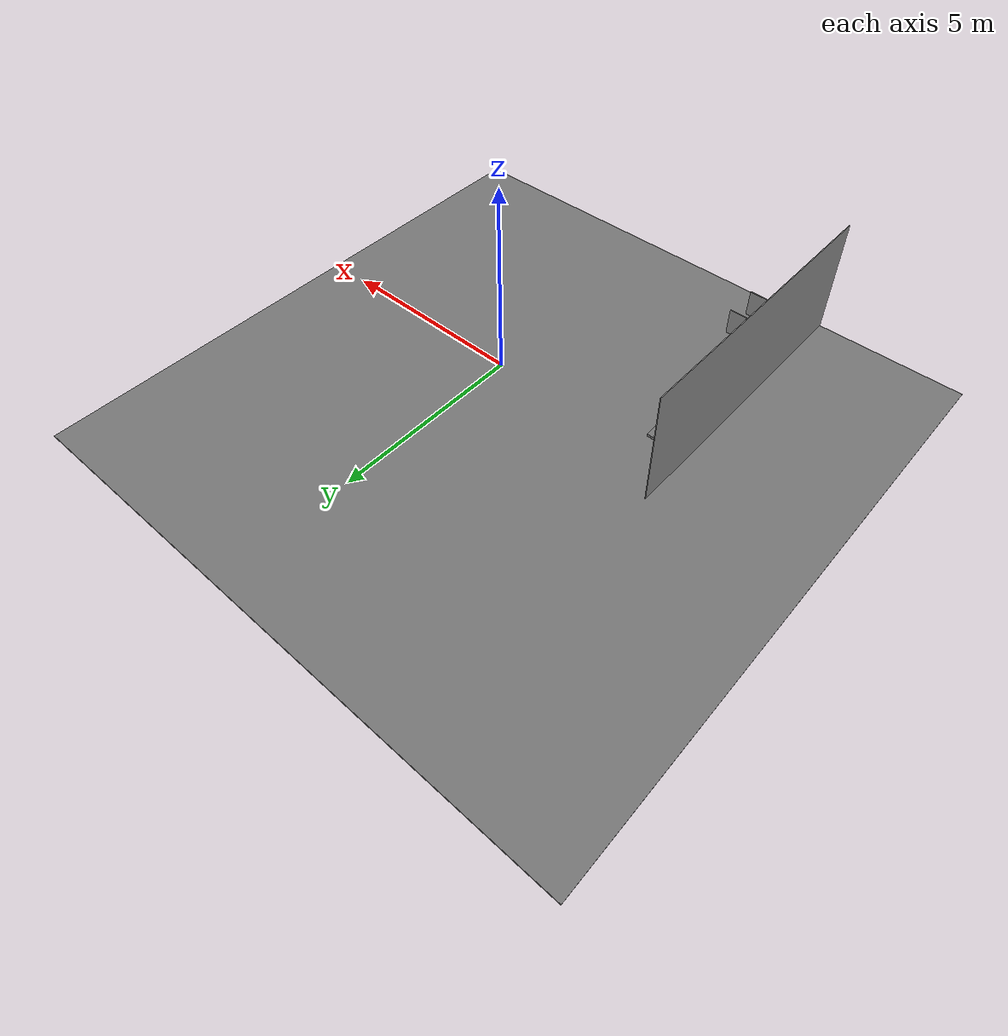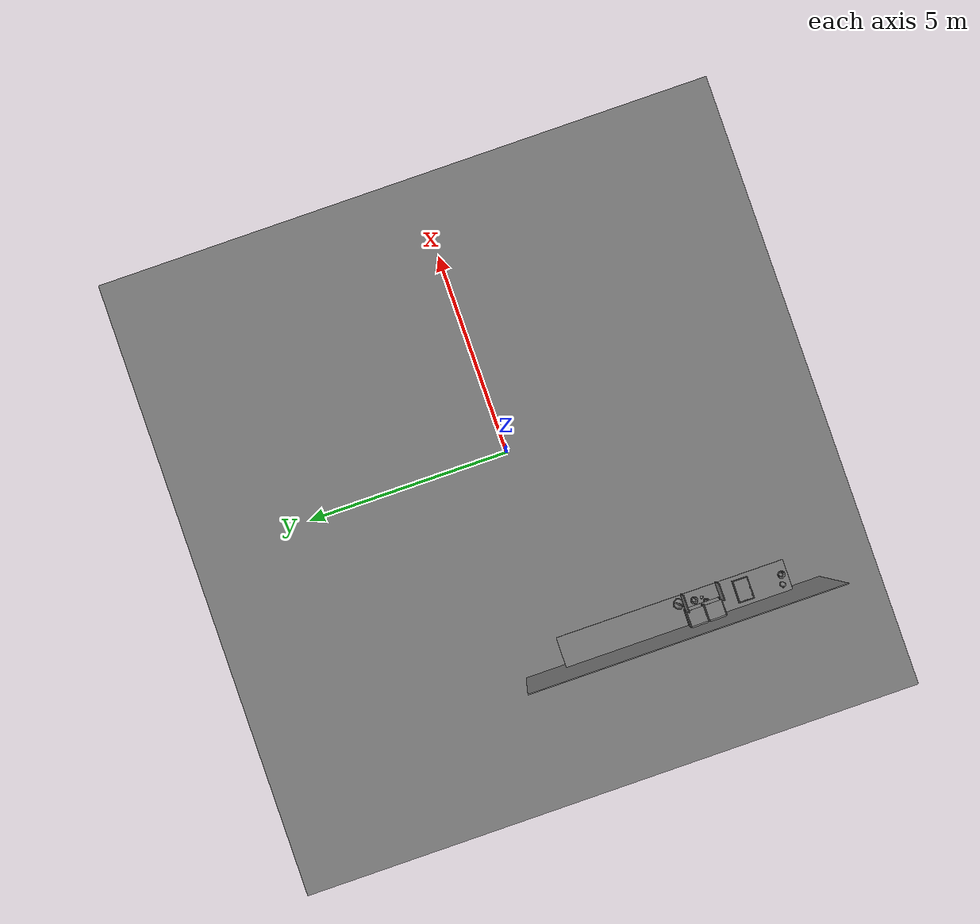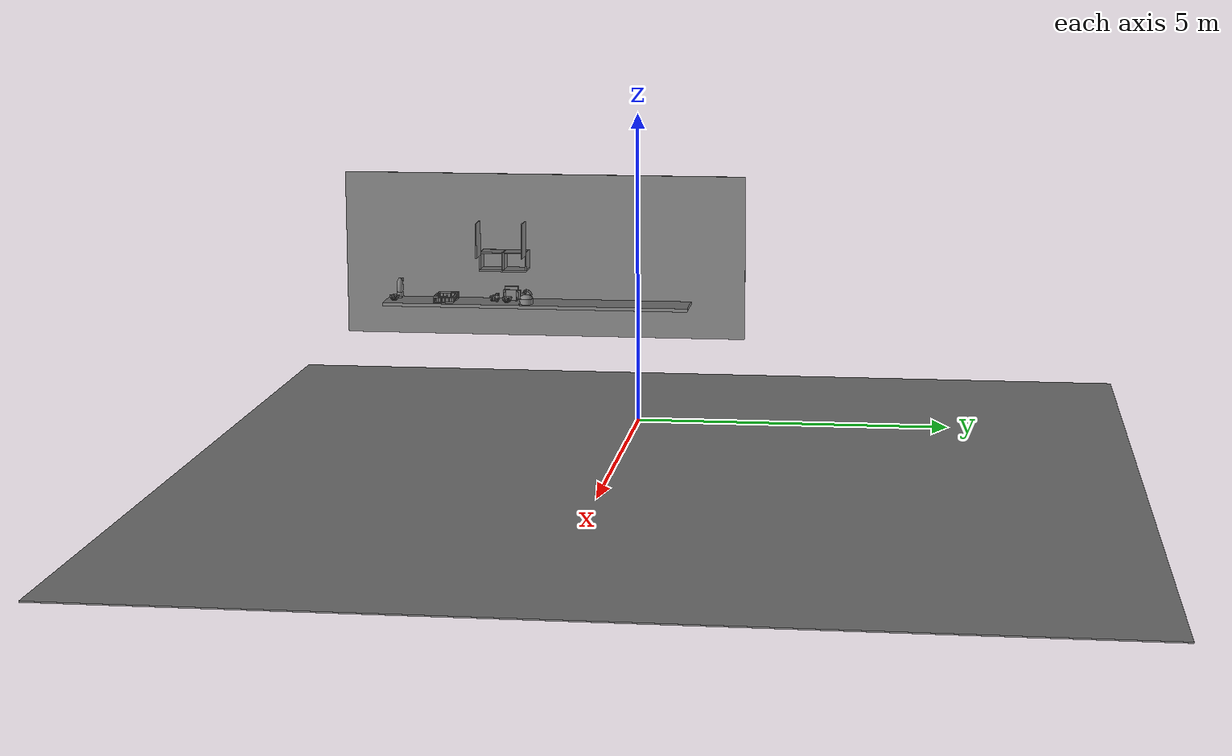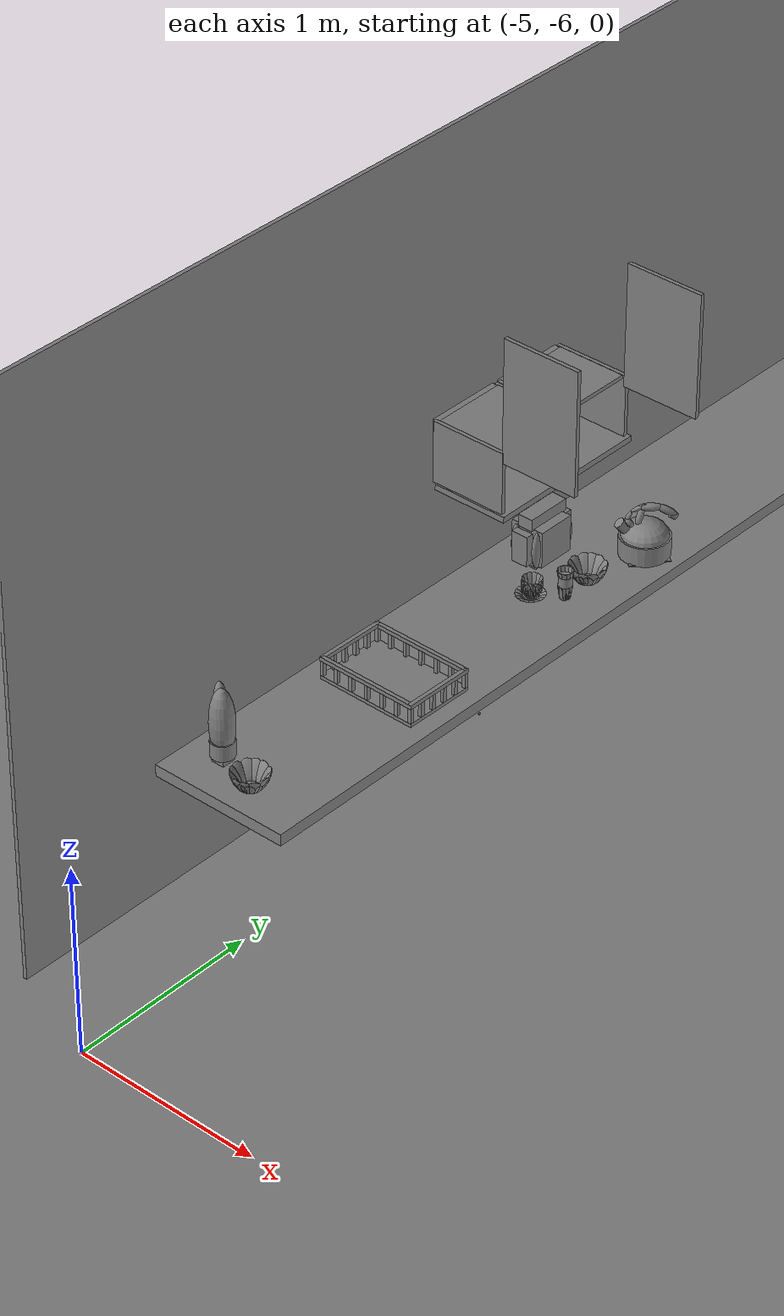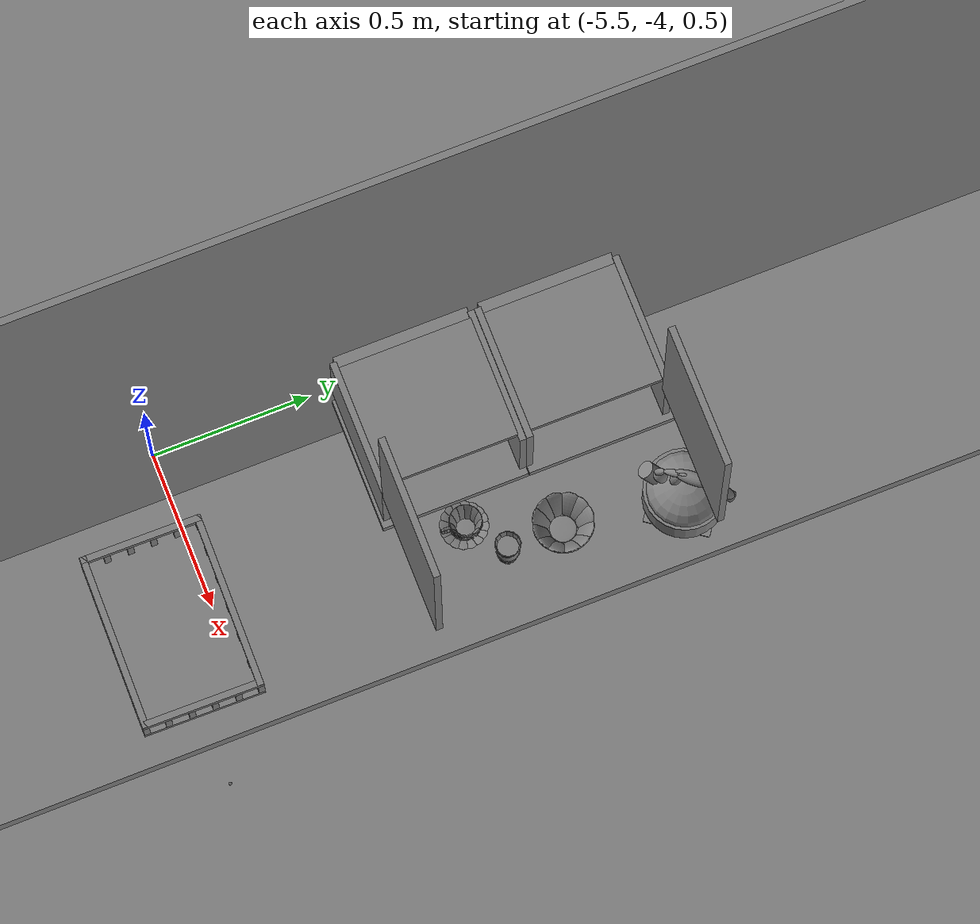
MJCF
<mujoco>
    <option gravity="0.000000000 0.000000000 -9.810000420" timestep="0.0049999999" integrator="implicitfast" density="9.8000002" viscosity="1.8000001e-05" noslip_iterations="10" iterations="100" sdf_iterations="50">
        <flag multiccd="disable"/>
    </option>
    <size memory="1000M"/>
    <compiler coordinate="local"/>
    <worldbody>
        <light cutoff="30" pos="0 1 1" dir="0 -1 -2"/>
        <light cutoff="30" pos="0 -1 1" dir="0 1 -2"/>
        <body pos="-4.860558510 -4.149443150 1.004824519" euler="0.000000000 0.000000000 -90.691108704" name="openloong_gripper_2f85_fix_base_usda_Basket_Kitchen_01">
            <geom contype="1" conaffinity="1" density="1000" type="box" material="" rgba="0.500000000 0.500000000 0.500000000 1.000000000" solimp="0.899999976 0.949999988 0.001000000" friction="1.000000000 0.005000000 0.000100000" solref="0.020000000 1.000000000" margin="0" condim="3" group="0" pos="-0.175679564 -0.000001431 0.109079957" quat="0.707107008 0.000000000 0.000000000 0.707106411" size="0.268999994 0.010000000 0.010500000" name="openloong_gripper_2f85_fix_base_usda_geom_3169BB05_4450_491E_9AAC_93B69E8ECA76"/>
            <geom contype="1" conaffinity="1" density="1000" type="box" material="" rgba="0.500000000 0.500000000 0.500000000 1.000000000" solimp="0.899999976 0.949999988 0.001000000" friction="1.000000000 0.005000000 0.000100000" solref="0.020000000 1.000000000" margin="0" condim="3" group="0" pos="-0.176020086 0.002992153 0.059861541" quat="0.707107008 0.000000000 0.000000000 0.707106411" size="0.009500000 0.009500000 0.039999999" name="openloong_gripper_2f85_fix_base_usda_geom_CA5E36A1_ED37_43A5_AB57_30016EBB43B9"/>
            <geom contype="1" conaffinity="1" density="1000" type="box" material="" rgba="0.500000000 0.500000000 0.500000000 1.000000000" solimp="0.899999976 0.949999988 0.001000000" friction="1.000000000 0.005000000 0.000100000" solref="0.020000000 1.000000000" margin="0" condim="3" group="0" pos="0.176000595 0.002991199 0.059860706" quat="0.707107008 0.000000000 0.000000000 0.707106411" size="0.009500000 0.009500000 0.039999999" name="openloong_gripper_2f85_fix_base_usda_geom_6D0DC9E7_59E5_4936_8984_1496D55A7CF4"/>
            <geom contype="1" conaffinity="1" density="1000" type="box" material="" rgba="0.500000000 0.500000000 0.500000000 1.000000000" solimp="0.899999976 0.949999988 0.001000000" friction="1.000000000 0.005000000 0.000100000" solref="0.020000000 1.000000000" margin="0" condim="3" group="0" pos="0.176003456 0.259475708 0.059860110" quat="0.707107008 0.000000000 0.000000000 0.707106411" size="0.009500000 0.009500000 0.039999999" name="openloong_gripper_2f85_fix_base_usda_geom_7FD45E29_B982_47F1_AAE7_6742DCD75027"/>
            <geom contype="1" conaffinity="1" density="1000" type="box" material="" rgba="0.500000000 0.500000000 0.500000000 1.000000000" solimp="0.899999976 0.949999988 0.001000000" friction="1.000000000 0.005000000 0.000100000" solref="0.020000000 1.000000000" margin="0" condim="3" group="0" pos="-0.176020026 -0.088695526 0.059861422" quat="0.707107008 0.000000000 0.000000000 0.707106411" size="0.009500000 0.009500000 0.039999999" name="openloong_gripper_2f85_fix_base_usda_geom_7F5CA508_1BD6_4562_B20F_80EBE4A752A3"/>
            <geom contype="1" conaffinity="1" density="1000" type="box" material="" rgba="0.500000000 0.500000000 0.500000000 1.000000000" solimp="0.899999976 0.949999988 0.001000000" friction="1.000000000 0.005000000 0.000100000" solref="0.020000000 1.000000000" margin="0" condim="3" group="0" pos="0.000000119 0.259647846 0.109080195" quat="0.707107008 0.000000000 0.000000000 0.707106411" size="0.010000000 0.185000002 0.010500000" name="openloong_gripper_2f85_fix_base_usda_geom_C54E063B_FE0A_4951_842A_E43A1CF7FBB3"/>
            <geom contype="1" conaffinity="1" density="1000" type="box" material="" rgba="0.500000000 0.500000000 0.500000000 1.000000000" solimp="0.899999976 0.949999988 0.001000000" friction="1.000000000 0.005000000 0.000100000" solref="0.020000000 1.000000000" margin="0" condim="3" group="0" pos="0.176002026 -0.259545326 0.059860349" quat="0.707107008 0.000000000 0.000000000 0.707106411" size="0.009500000 0.009500000 0.039999999" name="openloong_gripper_2f85_fix_base_usda_geom_8138820E_F7CE_4A9C_8F01_DFD8AF580171"/>
            <geom contype="1" conaffinity="1" density="1000" type="box" material="" rgba="0.500000000 0.500000000 0.500000000 1.000000000" solimp="0.899999976 0.949999988 0.001000000" friction="1.000000000 0.005000000 0.000100000" solref="0.020000000 1.000000000" margin="0" condim="3" group="0" pos="0.036305428 -0.259545326 0.059860706" quat="0.707107008 0.000000000 0.000000000 0.707106411" size="0.009500000 0.009500000 0.039999999" name="openloong_gripper_2f85_fix_base_usda_geom_20A240F5_2569_4B53_857C_567A3BCB3226"/>
            <geom contype="1" conaffinity="1" density="1000" type="box" material="" rgba="0.500000000 0.500000000 0.500000000 1.000000000" solimp="0.899999976 0.949999988 0.001000000" friction="1.000000000 0.005000000 0.000100000" solref="0.020000000 1.000000000" margin="0" condim="3" group="0" pos="0.000000000 -0.259647369 0.109080195" quat="0.707107008 0.000000000 0.000000000 0.707106411" size="0.010000000 0.185000002 0.010500000" name="openloong_gripper_2f85_fix_base_usda_geom_530D1ABF_5F99_4700_AD13_E30FCB343BD4"/>
            <geom contype="1" conaffinity="1" density="1000" type="box" material="" rgba="0.500000000 0.500000000 0.500000000 1.000000000" solimp="0.899999976 0.949999988 0.001000000" friction="1.000000000 0.005000000 0.000100000" solref="0.020000000 1.000000000" margin="0" condim="3" group="0" pos="-0.034950733 -0.259545803 0.059860826" quat="0.707107008 0.000000000 0.000000000 0.707106411" size="0.009500000 0.009500000 0.039999999" name="openloong_gripper_2f85_fix_base_usda_geom_EB7FFEC6_AA88_4FE3_9AAE_43E6D1047569"/>
            <geom contype="1" conaffinity="1" density="1000" type="box" material="" rgba="0.500000000 0.500000000 0.500000000 1.000000000" solimp="0.899999976 0.949999988 0.001000000" friction="1.000000000 0.005000000 0.000100000" solref="0.020000000 1.000000000" margin="0" condim="3" group="0" pos="0.108178139 0.259475946 0.059860229" quat="0.707107008 0.000000000 0.000000000 0.707106411" size="0.009500000 0.009500000 0.039999999" name="openloong_gripper_2f85_fix_base_usda_geom_6D1167AD_B19A_4200_8DCA_A5CD7107E7A7"/>
            <geom contype="1" conaffinity="1" density="1000" type="box" material="" rgba="0.500000000 0.500000000 0.500000000 1.000000000" solimp="0.899999976 0.949999988 0.001000000" friction="1.000000000 0.005000000 0.000100000" solref="0.020000000 1.000000000" margin="0" condim="3" group="0" pos="-0.106845737 0.259475231 0.059860826" quat="0.707107008 0.000000000 0.000000000 0.707106411" size="0.009500000 0.009500000 0.039999999" name="openloong_gripper_2f85_fix_base_usda_geom_78B7ACA8_931D_47CC_B3FE_134396A3298D"/>
            <geom contype="1" conaffinity="1" density="1000" type="box" material="" rgba="0.500000000 0.500000000 0.500000000 1.000000000" solimp="0.899999976 0.949999988 0.001000000" friction="1.000000000 0.005000000 0.000100000" solref="0.020000000 1.000000000" margin="0" condim="3" group="0" pos="-0.176020563 0.179506302 0.059861779" quat="0.707107008 0.000000000 0.000000000 0.707106411" size="0.009500000 0.009500000 0.039999999" name="openloong_gripper_2f85_fix_base_usda_geom_25604219_974F_48A0_8F1D_4EE357F51EA6"/>
            <geom contype="1" conaffinity="1" density="1000" type="box" material="" rgba="0.500000000 0.500000000 0.500000000 1.000000000" solimp="0.899999976 0.949999988 0.001000000" friction="1.000000000 0.005000000 0.000100000" solref="0.020000000 1.000000000" margin="0" condim="3" group="0" pos="-0.034949183 0.259475946 0.059860587" quat="0.707107008 0.000000000 0.000000000 0.707106411" size="0.009500000 0.009500000 0.039999999" name="openloong_gripper_2f85_fix_base_usda_geom_260BF131_97AB_4144_9A5F_69B915435F67"/>
            <geom contype="1" conaffinity="1" density="1000" type="box" material="" rgba="0.500000000 0.500000000 0.500000000 1.000000000" solimp="0.899999976 0.949999988 0.001000000" friction="1.000000000 0.005000000 0.000100000" solref="0.020000000 1.000000000" margin="0" condim="3" group="0" pos="0.175792217 -0.000001907 0.109079838" quat="0.707107008 0.000000000 0.000000000 0.707106411" size="0.268999994 0.010000000 0.010500000" name="openloong_gripper_2f85_fix_base_usda_geom_9C6C3F76_EAF7_432F_91FA_06759BF14284"/>
            <geom contype="1" conaffinity="1" density="1000" type="box" material="" rgba="0.500000000 0.500000000 0.500000000 1.000000000" solimp="0.899999976 0.949999988 0.001000000" friction="1.000000000 0.005000000 0.000100000" solref="0.020000000 1.000000000" margin="0" condim="3" group="0" pos="-0.000015259 0.000000000 0.010668159" quat="0.707107008 0.000000000 0.000000000 0.707106411" size="0.268999994 0.186000004 0.010500000" name="openloong_gripper_2f85_fix_base_usda_geom_A196C97F_E496_43A5_99BC_0DBF45669AB9"/>
            <geom contype="1" conaffinity="1" density="1000" type="box" material="" rgba="0.500000000 0.500000000 0.500000000 1.000000000" solimp="0.899999976 0.949999988 0.001000000" friction="1.000000000 0.005000000 0.000100000" solref="0.020000000 1.000000000" margin="0" condim="3" group="0" pos="-0.176020086 0.094225407 0.059861660" quat="0.707107008 0.000000000 0.000000000 0.707106411" size="0.009500000 0.009500000 0.039999999" name="openloong_gripper_2f85_fix_base_usda_geom_949ACB79_F540_4560_BE88_502DA2863D4A"/>
            <geom contype="1" conaffinity="1" density="1000" type="box" material="" rgba="0.500000000 0.500000000 0.500000000 1.000000000" solimp="0.899999976 0.949999988 0.001000000" friction="1.000000000 0.005000000 0.000100000" solref="0.020000000 1.000000000" margin="0" condim="3" group="0" pos="0.108177185 -0.259544849 0.059860468" quat="0.707107008 0.000000000 0.000000000 0.707106411" size="0.009500000 0.009500000 0.039999999" name="openloong_gripper_2f85_fix_base_usda_geom_A0126A6B_173D_45CA_AF20_4CF2F805D1E4"/>
            <geom contype="1" conaffinity="1" density="1000" type="box" material="" rgba="0.500000000 0.500000000 0.500000000 1.000000000" solimp="0.899999976 0.949999988 0.001000000" friction="1.000000000 0.005000000 0.000100000" solref="0.020000000 1.000000000" margin="0" condim="3" group="0" pos="-0.176019967 -0.177031994 0.059861302" quat="0.707107008 0.000000000 0.000000000 0.707106411" size="0.009500000 0.009500000 0.039999999" name="openloong_gripper_2f85_fix_base_usda_geom_D566EE83_17AE_4919_AD30_8EB0A60C45C6"/>
            <geom contype="1" conaffinity="1" density="1000" type="box" material="" rgba="0.500000000 0.500000000 0.500000000 1.000000000" solimp="0.899999976 0.949999988 0.001000000" friction="1.000000000 0.005000000 0.000100000" solref="0.020000000 1.000000000" margin="0" condim="3" group="0" pos="-0.176020026 -0.259545326 0.059861183" quat="0.707107008 0.000000000 0.000000000 0.707106411" size="0.009500000 0.009500000 0.039999999" name="openloong_gripper_2f85_fix_base_usda_geom_D1435E3C_99EA_438F_BAED_8C2D1C4E3E62"/>
            <geom contype="1" conaffinity="1" density="1000" type="box" material="" rgba="0.500000000 0.500000000 0.500000000 1.000000000" solimp="0.899999976 0.949999988 0.001000000" friction="1.000000000 0.005000000 0.000100000" solref="0.020000000 1.000000000" margin="0" condim="3" group="0" pos="-0.106846333 -0.259546280 0.059861064" quat="0.707107008 0.000000000 0.000000000 0.707106411" size="0.009500000 0.009500000 0.039999999" name="openloong_gripper_2f85_fix_base_usda_geom_6DD67C88_949D_4496_9C7F_5965C1A5FD95"/>
            <geom contype="1" conaffinity="1" density="1000" type="box" material="" rgba="0.500000000 0.500000000 0.500000000 1.000000000" solimp="0.899999976 0.949999988 0.001000000" friction="1.000000000 0.005000000 0.000100000" solref="0.020000000 1.000000000" margin="0" condim="3" group="0" pos="0.176000595 0.094224453 0.059860826" quat="0.707107008 0.000000000 0.000000000 0.707106411" size="0.009500000 0.009500000 0.039999999" name="openloong_gripper_2f85_fix_base_usda_geom_4649CDD8_FA3C_43A9_9579_F2C313DED04D"/>
            <geom contype="1" conaffinity="1" density="1000" type="box" material="" rgba="0.500000000 0.500000000 0.500000000 1.000000000" solimp="0.899999976 0.949999988 0.001000000" friction="1.000000000 0.005000000 0.000100000" solref="0.020000000 1.000000000" margin="0" condim="3" group="0" pos="0.176001072 -0.088696480 0.059860587" quat="0.707107008 0.000000000 0.000000000 0.707106411" size="0.009500000 0.009500000 0.039999999" name="openloong_gripper_2f85_fix_base_usda_geom_23DFD08B_8390_4EBD_9A65_F46B56398131"/>
            <geom contype="1" conaffinity="1" density="1000" type="box" material="" rgba="0.500000000 0.500000000 0.500000000 1.000000000" solimp="0.899999976 0.949999988 0.001000000" friction="1.000000000 0.005000000 0.000100000" solref="0.020000000 1.000000000" margin="0" condim="3" group="0" pos="0.036307096 0.259476185 0.059860468" quat="0.707107008 0.000000000 0.000000000 0.707106411" size="0.009500000 0.009500000 0.039999999" name="openloong_gripper_2f85_fix_base_usda_geom_AC4A34CC_DF07_4F69_9378_56E388DD9A35"/>
            <geom contype="1" conaffinity="1" density="1000" type="box" material="" rgba="0.500000000 0.500000000 0.500000000 1.000000000" solimp="0.899999976 0.949999988 0.001000000" friction="1.000000000 0.005000000 0.000100000" solref="0.020000000 1.000000000" margin="0" condim="3" group="0" pos="0.176001549 -0.177031994 0.059860468" quat="0.707107008 0.000000000 0.000000000 0.707106411" size="0.009500000 0.009500000 0.039999999" name="openloong_gripper_2f85_fix_base_usda_geom_F4280CB1_5C22_4BE6_8390_747ABD5A9E5A"/>
            <geom contype="1" conaffinity="1" density="1000" type="box" material="" rgba="0.500000000 0.500000000 0.500000000 1.000000000" solimp="0.899999976 0.949999988 0.001000000" friction="1.000000000 0.005000000 0.000100000" solref="0.020000000 1.000000000" margin="0" condim="3" group="0" pos="0.176000118 0.179505348 0.059860945" quat="0.707107008 0.000000000 0.000000000 0.707106411" size="0.009500000 0.009500000 0.039999999" name="openloong_gripper_2f85_fix_base_usda_geom_A49E80C7_45C0_4CD5_A86B_95FE0E806850"/>
            <geom contype="1" conaffinity="1" density="1000" type="box" material="" rgba="0.500000000 0.500000000 0.500000000 1.000000000" solimp="0.899999976 0.949999988 0.001000000" friction="1.000000000 0.005000000 0.000100000" solref="0.020000000 1.000000000" margin="0" condim="3" group="0" pos="-0.176020086 0.259474993 0.059860945" quat="0.707107008 0.000000000 0.000000000 0.707106411" size="0.009500000 0.009500000 0.039999999" name="openloong_gripper_2f85_fix_base_usda_geom_091AF59F_AC30_4B7F_ADA7_E2008FB63FAF"/>
            <freejoint name="openloong_gripper_2f85_fix_base_usda_Basket_Kitchen_01_joint"/>
        </body>
        <body pos="-4.802892208 -3.488179445 1.876015186" euler="89.999992371 -89.999946594 0.000000000" name="Interactive Objcets_guimen_01">
            <geom contype="1" conaffinity="1" density="1000" type="box" material="" rgba="0.500000000 0.500000000 0.500000000 1.000000000" solimp="0.899999976 0.949999988 0.001000000" friction="1.000000000 0.005000000 0.000100000" solref="0.020000000 1.000000000" margin="0" condim="3" group="0" pos="0.006727934 0.314709902 -0.203009605" quat="1.000000000 0.000000119 -0.000000119 0.000000000" size="0.010000000 0.317999989 0.204999998" name="Interactive Objcets_geom_5BC84983_51D4_4025_A43D_D7281A4569E7"/>
            <joint armature="0" stiffness="0" damping="1" axis="0.000000 1.000000 0.000000" type="hinge" name="Interactive Objcets_guimen_01"/>
        </body>
        <body pos="-4.805274963 -2.665403366 1.876015186" euler="89.999877930 89.999969482 0.000000000" name="Interactive Objcets_guimen_02">
            <geom contype="1" conaffinity="1" density="1000" type="box" material="" rgba="0.500000000 0.500000000 0.500000000 1.000000000" solimp="0.899999976 0.949999988 0.001000000" friction="1.000000000 0.005000000 0.000100000" solref="0.020000000 1.000000000" margin="0" condim="3" group="0" pos="0.006727815 0.314709663 0.203009367" quat="0.999999940 0.000000000 0.000000000 0.000000000" size="0.010000000 0.317999989 0.204999998" name="Interactive Objcets_geom_CFAA2A72_13D9_4E25_8AC9_E9E59C956F2B"/>
            <joint armature="0" stiffness="0" damping="1" axis="0.000000 1.000000 0.000000" type="hinge" name="Interactive Objcets_guimen_02"/>
        </body>
        <body pos="-4.827295780 -3.287638187 1.074643731" euler="0.000000000 0.000000000 89.999992371" name="Interactive Objcets_coffeecup_01">
            <geom contype="1" conaffinity="1" density="1000" type="ellipsoid" material="" rgba="0.500000000 0.500000000 0.500000000 1.000000000" solimp="0.899999976 0.949999988 0.001000000" friction="1.000000000 0.005000000 0.000100000" solref="0.020000000 1.000000000" margin="0" condim="3" group="0" pos="0.035336256 0.000558376 -0.043215394" quat="0.999999881 0.000000000 0.000000000 0.000000000" size="0.029999999 0.029999999 0.001000000" name="Interactive Objcets_geom_7A08FE6E_83F7_466E_B521_F4569D009ED7"/>
            <geom contype="1" conaffinity="1" density="1000" type="ellipsoid" material="" rgba="0.500000000 0.500000000 0.500000000 1.000000000" solimp="0.899999976 0.949999988 0.001000000" friction="1.000000000 0.005000000 0.000100000" solref="0.020000000 1.000000000" margin="0" condim="3" group="0" pos="0.067416430 -0.018191338 0.002976775" quat="0.961934388 0.024418317 0.091648072 -0.256293803" size="0.005000000 0.029999999 0.048999999" name="Interactive Objcets_geom_5B4CC273_E492_4C19_A05E_284DC6C047B0"/>
            <geom contype="1" conaffinity="1" density="1000" type="ellipsoid" material="" rgba="0.500000000 0.500000000 0.500000000 1.000000000" solimp="0.899999976 0.949999988 0.001000000" friction="1.000000000 0.005000000 0.000100000" solref="0.020000000 1.000000000" margin="0" condim="3" group="0" pos="0.034471050 -0.037125111 0.002976775" quat="0.701517045 0.067293778 0.066836871 -0.706313014" size="0.005000000 0.029999999 0.048999999" name="Interactive Objcets_geom_60BC7499_95B4_4945_A376_5786AEE8C8CB"/>
            <geom contype="1" conaffinity="1" density="1000" type="ellipsoid" material="" rgba="0.500000000 0.500000000 0.500000000 1.000000000" solimp="0.899999976 0.949999988 0.001000000" friction="1.000000000 0.005000000 0.000100000" solref="0.020000000 1.000000000" margin="0" condim="3" group="0" pos="0.035336256 0.000558376 -0.045152068" quat="0.999999881 0.000000000 0.000000000 0.000000000" size="0.029999999 0.029999999 0.001000000" name="Interactive Objcets_geom_EF9B19A4_C660_4CBF_A6C3_561E73D1A466"/>
            <geom contype="1" conaffinity="1" density="1000" type="ellipsoid" material="" rgba="0.500000000 0.500000000 0.500000000 1.000000000" solimp="0.899999976 0.949999988 0.001000000" friction="1.000000000 0.005000000 0.000100000" solref="0.020000000 1.000000000" margin="0" condim="3" group="0" pos="0.001010895 -0.016271591 0.002976775" quat="0.228377163 0.092315644 0.021758538 -0.968941689" size="0.005000000 0.029999999 0.048999999" name="Interactive Objcets_geom_F20ADFE1_4EC3_4C24_B0D4_3CC89650DF9E"/>
            <geom contype="1" conaffinity="1" density="1000" type="capsule" material="" rgba="0.500000000 0.500000000 0.500000000 1.000000000" solimp="0.899999976 0.949999988 0.001000000" friction="1.000000000 0.005000000 0.000100000" solref="0.020000000 1.000000000" margin="0" condim="3" group="0" pos="-0.021276474 0.000000000 0.038509369" quat="0.633189917 0.000000000 0.773996413 0.000000000" size="0.004000000 0.009000000 1.000000000" name="Interactive Objcets_geom_3C4110A7_DE57_42D3_9F97_AA5A46C0C5EA"/>
            <geom contype="1" conaffinity="1" density="1000" type="capsule" material="" rgba="0.500000000 0.500000000 0.500000000 1.000000000" solimp="0.899999976 0.949999988 0.001000000" friction="1.000000000 0.005000000 0.000100000" solref="0.020000000 1.000000000" margin="0" condim="3" group="0" pos="-0.018014431 0.000000000 0.001762271" quat="0.707106769 -0.000000004 0.707106709 -0.000000088" size="0.004000000 0.005000000 1.000000000" name="Interactive Objcets_geom_2F724F39_62BB_40DD_90F4_ED9D36AB6843"/>
            <geom contype="1" conaffinity="1" density="1000" type="ellipsoid" material="" rgba="0.500000000 0.500000000 0.500000000 1.000000000" solimp="0.899999976 0.949999988 0.001000000" friction="1.000000000 0.005000000 0.000100000" solref="0.020000000 1.000000000" margin="0" condim="3" group="0" pos="0.068445444 0.017385960 0.002976775" quat="0.228377223 -0.092319682 -0.021759447 -0.968941331" size="0.005000000 0.029999999 0.048999999" name="Interactive Objcets_geom_650DB4FA_1AD4_45F4_81FD_34ACD77E71E9"/>
            <geom contype="1" conaffinity="1" density="1000" type="ellipsoid" material="" rgba="0.500000000 0.500000000 0.500000000 1.000000000" solimp="0.899999976 0.949999988 0.001000000" friction="1.000000000 0.005000000 0.000100000" solref="0.020000000 1.000000000" margin="0" condim="3" group="0" pos="0.002039194 0.019308567 0.002976775" quat="0.961933970 -0.024419386 -0.091652036 -0.256293654" size="0.005000000 0.029999999 0.048999999" name="Interactive Objcets_geom_5197B920_C383_4530_9759_1E969548A69F"/>
            <geom contype="1" conaffinity="1" density="1000" type="ellipsoid" material="" rgba="0.500000000 0.500000000 0.500000000 1.000000000" solimp="0.899999976 0.949999988 0.001000000" friction="1.000000000 0.005000000 0.000100000" solref="0.020000000 1.000000000" margin="0" condim="3" group="0" pos="0.034984604 0.038240910 0.002976775" quat="0.701516926 -0.067296736 -0.066839755 -0.706312656" size="0.005000000 0.029999999 0.048999999" name="Interactive Objcets_geom_9CF1F7F6_9762_4122_84A6_7F344F738F02"/>
            <geom contype="1" conaffinity="1" density="1000" type="ellipsoid" material="" rgba="0.500000000 0.500000000 0.500000000 1.000000000" solimp="0.899999976 0.949999988 0.001000000" friction="1.000000000 0.005000000 0.000100000" solref="0.020000000 1.000000000" margin="0" condim="3" group="0" pos="0.017669693 0.034160614 0.002976775" quat="0.848410904 -0.049618516 -0.080835648 -0.520770907" size="0.005000000 0.029999999 0.048999999" name="Interactive Objcets_geom_30363C4E_66CD_4058_A55B_066D3EC58069"/>
            <geom contype="1" conaffinity="1" density="1000" type="ellipsoid" material="" rgba="0.500000000 0.500000000 0.500000000 1.000000000" solimp="0.899999976 0.949999988 0.001000000" friction="1.000000000 0.005000000 0.000100000" solref="0.020000000 1.000000000" margin="0" condim="3" group="0" pos="-0.002956629 0.000558376 0.002976775" quat="0.995491505 0.000000004 -0.094849378 -0.000000089" size="0.005000000 0.029999999 0.048999999" name="Interactive Objcets_geom_9040DE65_EB9C_4C0B_9332_1CFA75D28B11"/>
            <geom contype="1" conaffinity="1" density="1000" type="ellipsoid" material="" rgba="0.500000000 0.500000000 0.500000000 1.000000000" solimp="0.899999976 0.949999988 0.001000000" friction="1.000000000 0.005000000 0.000100000" solref="0.020000000 1.000000000" margin="0" condim="3" group="0" pos="0.051787138 -0.033043861 0.002976775" quat="0.848411202 0.049616337 0.080832161 -0.520771146" size="0.005000000 0.029999999 0.048999999" name="Interactive Objcets_geom_01EE71A2_7C44_4D9D_AD15_BD9F6F8E221E"/>
            <geom contype="1" conaffinity="1" density="1000" type="capsule" material="" rgba="0.500000000 0.500000000 0.500000000 1.000000000" solimp="0.899999976 0.949999988 0.001000000" friction="1.000000000 0.005000000 0.000100000" solref="0.020000000 1.000000000" margin="0" condim="3" group="0" pos="-0.030251026 0.000000000 0.004966617" quat="0.480583906 -0.000000000 0.876948774 -0.000000126" size="0.004000000 0.005000000 1.000000000" name="Interactive Objcets_geom_C71C35F6_74A2_4BED_89B9_FD2A1394FB04"/>
            <geom contype="1" conaffinity="1" density="1000" type="capsule" material="" rgba="0.500000000 0.500000000 0.500000000 1.000000000" solimp="0.899999976 0.949999988 0.001000000" friction="1.000000000 0.005000000 0.000100000" solref="0.020000000 1.000000000" margin="0" condim="3" group="0" pos="-0.036300898 0.000000000 0.021037936" quat="0.044551343 -0.000000000 0.999007046 -0.000000126" size="0.004000000 0.012000000 1.000000000" name="Interactive Objcets_geom_73EFA85C_B943_4AC6_A481_BD17D7D82A00"/>
            <geom contype="1" conaffinity="1" density="1000" type="capsule" material="" rgba="0.500000000 0.500000000 0.500000000 1.000000000" solimp="0.899999976 0.949999988 0.001000000" friction="1.000000000 0.005000000 0.000100000" solref="0.020000000 1.000000000" margin="0" condim="3" group="0" pos="-0.008219719 0.000000000 -0.000944734" quat="0.364379913 0.000000063 0.931250274 -0.000000063" size="0.004000000 0.003000000 1.000000000" name="Interactive Objcets_geom_C96FB441_6FA7_42D6_9D72_A5F92B7C15EC"/>
            <geom contype="1" conaffinity="1" density="1000" type="capsule" material="" rgba="0.500000000 0.500000000 0.500000000 1.000000000" solimp="0.899999976 0.949999988 0.001000000" friction="1.000000000 0.005000000 0.000100000" solref="0.020000000 1.000000000" margin="0" condim="3" group="0" pos="-0.033022881 0.000000000 0.037873149" quat="0.874267220 0.000000042 0.485444903 -0.000000084" size="0.004000000 0.004000000 1.000000000" name="Interactive Objcets_geom_0B2E6F24_79D3_43CA_9363_FCCB805F98AB"/>
            <geom contype="1" conaffinity="1" density="1000" type="ellipsoid" material="" rgba="0.500000000 0.500000000 0.500000000 1.000000000" solimp="0.899999976 0.949999988 0.001000000" friction="1.000000000 0.005000000 0.000100000" solref="0.020000000 1.000000000" margin="0" condim="3" group="0" pos="0.015755907 -0.032001972 0.002976775" quat="0.496025920 0.082232773 0.047258731 -0.863112032" size="0.005000000 0.029999999 0.048999999" name="Interactive Objcets_geom_8D47606D_BC58_4673_8E58_974C9B4770A4"/>
            <geom contype="1" conaffinity="1" density="1000" type="ellipsoid" material="" rgba="0.500000000 0.500000000 0.500000000 1.000000000" solimp="0.899999976 0.949999988 0.001000000" friction="1.000000000 0.005000000 0.000100000" solref="0.020000000 1.000000000" margin="0" condim="3" group="0" pos="0.072411790 0.000558376 0.002976775" quat="0.995491922 -0.000000019 0.094845265 -0.000000089" size="0.005000000 0.029999999 0.048999999" name="Interactive Objcets_geom_A0705088_C580_4A5C_986B_85DB1274B864"/>
            <geom contype="1" conaffinity="1" density="1000" type="ellipsoid" material="" rgba="0.500000000 0.500000000 0.500000000 1.000000000" solimp="0.899999976 0.949999988 0.001000000" friction="1.000000000 0.005000000 0.000100000" solref="0.020000000 1.000000000" margin="0" condim="3" group="0" pos="0.053700209 0.033117294 0.002976775" quat="0.496025741 -0.082236379 -0.047260769 -0.863111615" size="0.005000000 0.029999999 0.048999999" name="Interactive Objcets_geom_E70F5F15_09A8_43B7_B9D7_760FC0E6394A"/>
            <freejoint name="Interactive Objcets_coffeecup_01"/>
        </body>
        <body pos="-5.020127296 -2.953741550 1.135127425" euler="89.999946594 0.000000000 0.000000000" name="Interactive Objcets_Bread">
            <geom contype="1" conaffinity="1" density="1000" type="box" material="" rgba="0.500000000 0.500000000 0.500000000 1.000000000" solimp="0.899999976 0.949999988 0.001000000" friction="1.000000000 0.005000000 0.000100000" solref="0.020000000 1.000000000" margin="0" condim="3" group="0" pos="-0.008702755 -0.017670274 -0.135069147" quat="0.707107067 -0.707106471 0.000000021 -0.000000021" size="0.045000002 0.020000000 0.079999998" name="Interactive Objcets_geom_340403C1_5BC4_40F7_9096_716C75C018A4"/>
            <geom contype="1" conaffinity="1" density="1000" type="box" material="" rgba="0.500000000 0.500000000 0.500000000 1.000000000" solimp="0.899999976 0.949999988 0.001000000" friction="1.000000000 0.005000000 0.000100000" solref="0.020000000 1.000000000" margin="0" condim="3" group="0" pos="0.033925056 -0.123201847 0.086778767" quat="0.707107067 -0.707106471 0.000000021 -0.000000021" size="0.020000000 0.020000000 0.005000000" name="Interactive Objcets_geom_D5FF8C3A_DE4B_42B0_8A62_896A7A4DC338"/>
            <geom contype="1" conaffinity="1" density="1000" type="box" material="" rgba="0.500000000 0.500000000 0.500000000 1.000000000" solimp="0.899999976 0.949999988 0.001000000" friction="1.000000000 0.005000000 0.000100000" solref="0.020000000 1.000000000" margin="0" condim="3" group="0" pos="-0.008702755 -0.016588926 0.000174277" quat="0.707107067 -0.707106471 0.000000021 -0.000000021" size="0.090000004 0.100000001 0.094999999" name="Interactive Objcets_geom_01E571D8_F10D_4D1A_AB58_819CF6C124AA"/>
            <geom contype="1" conaffinity="1" density="1000" type="ellipsoid" material="" rgba="0.500000000 0.500000000 0.500000000 1.000000000" solimp="0.899999976 0.949999988 0.001000000" friction="1.000000000 0.005000000 0.000100000" solref="0.020000000 1.000000000" margin="0" condim="3" group="0" pos="-0.067312241 -0.026057482 -0.101716787" quat="0.707107067 -0.707106471 0.000000021 -0.000000021" size="0.020000000 0.029999999 0.094999999" name="Interactive Objcets_geom_C39593F9_1C9F_436F_A80A_88C1D5BB2BBD"/>
            <geom contype="1" conaffinity="1" density="1000" type="ellipsoid" material="" rgba="0.500000000 0.500000000 0.500000000 1.000000000" solimp="0.899999976 0.949999988 0.001000000" friction="1.000000000 0.005000000 0.000100000" solref="0.020000000 1.000000000" margin="0" condim="3" group="0" pos="0.052222252 -0.026057363 0.101459242" quat="0.707107067 -0.707106471 0.000000021 -0.000000021" size="0.020000000 0.029999999 0.094999999" name="Interactive Objcets_geom_2634AFFC_157E_427A_A320_042F0F541EAD"/>
            <geom contype="1" conaffinity="1" density="1000" type="box" material="" rgba="0.500000000 0.500000000 0.500000000 1.000000000" solimp="0.899999976 0.949999988 0.001000000" friction="1.000000000 0.005000000 0.000100000" solref="0.020000000 1.000000000" margin="0" condim="3" group="0" pos="-0.050020695 -0.123201847 0.086778767" quat="0.707107067 -0.707106471 0.000000021 -0.000000021" size="0.020000000 0.020000000 0.005000000" name="Interactive Objcets_geom_FD0101FF_9E2B_4B16_A7D5_9C2AD97FE792"/>
            <geom contype="1" conaffinity="1" density="1000" type="box" material="" rgba="0.500000000 0.500000000 0.500000000 1.000000000" solimp="0.899999976 0.949999988 0.001000000" friction="1.000000000 0.005000000 0.000100000" solref="0.020000000 1.000000000" margin="0" condim="3" group="0" pos="0.033925056 -0.123201728 -0.092369899" quat="0.707107067 -0.707106471 0.000000021 -0.000000021" size="0.020000000 0.020000000 0.005000000" name="Interactive Objcets_geom_339FA972_6989_4394_957E_7890ABF450E4"/>
            <geom contype="1" conaffinity="1" density="1000" type="ellipsoid" material="" rgba="0.500000000 0.500000000 0.500000000 1.000000000" solimp="0.899999976 0.949999988 0.001000000" friction="1.000000000 0.005000000 0.000100000" solref="0.020000000 1.000000000" margin="0" condim="3" group="0" pos="-0.069190502 -0.026057363 0.101458766" quat="0.707107067 -0.707106471 0.000000021 -0.000000021" size="0.020000000 0.029999999 0.094999999" name="Interactive Objcets_geom_8461B9F2_E7D4_47C3_81A3_3AB94CE1C86E"/>
            <geom contype="1" conaffinity="1" density="1000" type="box" material="" rgba="0.500000000 0.500000000 0.500000000 1.000000000" solimp="0.899999976 0.949999988 0.001000000" friction="1.000000000 0.005000000 0.000100000" solref="0.020000000 1.000000000" margin="0" condim="3" group="0" pos="-0.008702755 -0.017670155 0.134585604" quat="0.707107067 -0.707106471 0.000000021 -0.000000021" size="0.045000002 0.020000000 0.079999998" name="Interactive Objcets_geom_5412160E_42D6_4EFC_A056_012806EC8FA8"/>
            <geom contype="1" conaffinity="1" density="1000" type="box" material="" rgba="0.500000000 0.500000000 0.500000000 1.000000000" solimp="0.899999976 0.949999988 0.001000000" friction="1.000000000 0.005000000 0.000100000" solref="0.020000000 1.000000000" margin="0" condim="3" group="0" pos="-0.050020695 -0.123201728 -0.092370376" quat="0.707107067 -0.707106471 0.000000021 -0.000000021" size="0.020000000 0.020000000 0.005000000" name="Interactive Objcets_geom_DB89E989_854A_4180_B0FA_39628FCC7150"/>
            <geom contype="1" conaffinity="1" density="1000" type="box" material="" rgba="0.500000000 0.500000000 0.500000000 1.000000000" solimp="0.899999976 0.949999988 0.001000000" friction="1.000000000 0.005000000 0.000100000" solref="0.020000000 1.000000000" margin="0" condim="3" group="0" pos="-0.008702755 0.104617000 -0.003706597" quat="0.707107067 -0.707106471 0.000000021 -0.000000021" size="0.039999999 0.119999997 0.030999999" name="Interactive Objcets_geom_0D73C2F8_76A6_4746_9F00_C5E0DE47F1FE"/>
            <geom contype="1" conaffinity="1" density="1000" type="ellipsoid" material="" rgba="0.500000000 0.500000000 0.500000000 1.000000000" solimp="0.899999976 0.949999988 0.001000000" friction="1.000000000 0.005000000 0.000100000" solref="0.020000000 1.000000000" margin="0" condim="3" group="0" pos="0.052222252 -0.026057243 -0.106481344" quat="0.707107067 -0.707106471 0.000000021 -0.000000021" size="0.020000000 0.029999999 0.094999999" name="Interactive Objcets_geom_8AFC8CE6_3403_4E0D_9769_4D6EBB663E08"/>
            <freejoint name="Interactive Objcets_Bread"/>
        </body>
        <body pos="-4.821335316 -5.105734825 1.007418752" euler="0.000000000 0.000000000 89.999946594" name="Interactive Objcets_bow_04">
            <geom contype="1" conaffinity="1" density="1000" type="ellipsoid" material="" rgba="0.500000000 0.500000000 0.500000000 1.000000000" solimp="0.899999976 0.949999988 0.001000000" friction="1.000000000 0.005000000 0.000100000" solref="0.020000000 1.000000000" margin="0" condim="3" group="0" pos="0.052321672 -0.040297985 0.044118762" quat="0.919264674 0.076882720 0.225593746 -0.313287675" size="0.010000000 0.039999999 0.052000001" name="Interactive Objcets_geom_B6D7FB00_8CD7_4395_9E33_7CE43D935A03"/>
            <geom contype="1" conaffinity="1" density="1000" type="ellipsoid" material="" rgba="0.500000000 0.500000000 0.500000000 1.000000000" solimp="0.899999976 0.949999988 0.001000000" friction="1.000000000 0.005000000 0.000100000" solref="0.020000000 1.000000000" margin="0" condim="3" group="0" pos="0.059080124 0.029511929 0.044118762" quat="0.223252952 -0.231952190 -0.054787360 -0.945174456" size="0.010000000 0.039999999 0.052000001" name="Interactive Objcets_geom_A3F7EB17_581D_4E56_8DC0_02A19A447707"/>
            <geom contype="1" conaffinity="1" density="1000" type="ellipsoid" material="" rgba="0.500000000 0.500000000 0.500000000 1.000000000" solimp="0.899999976 0.949999988 0.001000000" friction="1.000000000 0.005000000 0.000100000" solref="0.020000000 1.000000000" margin="0" condim="3" group="0" pos="0.000082970 0.000000000 0.003118873" quat="1.000000000 0.000000000 0.000000000 0.000000000" size="0.039999999 0.039999999 0.002000000" name="Interactive Objcets_geom_93DB36E4_EF2B_4170_97CD_5F255E2B21D5"/>
            <geom contype="1" conaffinity="1" density="1000" type="ellipsoid" material="" rgba="0.500000000 0.500000000 0.500000000 1.000000000" solimp="0.899999976 0.949999988 0.001000000" friction="1.000000000 0.005000000 0.000100000" solref="0.020000000 1.000000000" margin="0" condim="3" group="0" pos="-0.040080309 -0.052354813 0.044118762" quat="0.429593146 0.213749856 0.105425127 -0.871003032" size="0.010000000 0.039999999 0.052000001" name="Interactive Objcets_geom_FB502634_D5AB_43A5_9FAA_4AE77A1A8B90"/>
            <geom contype="1" conaffinity="1" density="1000" type="ellipsoid" material="" rgba="0.500000000 0.500000000 0.500000000 1.000000000" solimp="0.899999976 0.949999988 0.001000000" friction="1.000000000 0.005000000 0.000100000" solref="0.020000000 1.000000000" margin="0" condim="3" group="0" pos="0.000243664 -0.065983295 0.044118762" quat="0.687598884 0.168314576 0.168741226 -0.685860336" size="0.010000000 0.039999999 0.052000001" name="Interactive Objcets_geom_23EDEF40_2413_4316_BE8D_FC3512738B40"/>
            <geom contype="1" conaffinity="1" density="1000" type="ellipsoid" material="" rgba="0.500000000 0.500000000 0.500000000 1.000000000" solimp="0.899999976 0.949999988 0.001000000" friction="1.000000000 0.005000000 0.000100000" solref="0.020000000 1.000000000" margin="0" condim="3" group="0" pos="-0.065898657 -0.000007629 0.044118762" quat="0.971183062 -0.000000142 -0.238334835 0.000000030" size="0.010000000 0.039999999 0.052000001" name="Interactive Objcets_geom_8DF109E8_B58A_4F94_9B07_8FCDD75CBDE5"/>
            <geom contype="1" conaffinity="1" density="1000" type="ellipsoid" material="" rgba="0.500000000 0.500000000 0.500000000 1.000000000" solimp="0.899999976 0.949999988 0.001000000" friction="1.000000000 0.005000000 0.000100000" solref="0.020000000 1.000000000" margin="0" condim="3" group="0" pos="-0.052167892 0.040281773 0.044118762" quat="0.919264615 -0.076883025 -0.225593626 -0.313287735" size="0.010000000 0.039999999 0.052000001" name="Interactive Objcets_geom_680E20A3_7E27_456E_AC4A_E29A2438EEE0"/>
            <geom contype="1" conaffinity="1" density="1000" type="ellipsoid" material="" rgba="0.500000000 0.500000000 0.500000000 1.000000000" solimp="0.899999976 0.949999988 0.001000000" friction="1.000000000 0.005000000 0.000100000" solref="0.020000000 1.000000000" margin="0" condim="3" group="0" pos="-0.029293537 0.059069157 0.044118762" quat="0.825556040 -0.125530839 -0.202596709 -0.511521041" size="0.010000000 0.039999999 0.052000001" name="Interactive Objcets_geom_E5F67572_7066_42D8_85BD_1238DEB49080"/>
            <geom contype="1" conaffinity="1" density="1000" type="ellipsoid" material="" rgba="0.500000000 0.500000000 0.500000000 1.000000000" solimp="0.899999976 0.949999988 0.001000000" friction="1.000000000 0.005000000 0.000100000" solref="0.020000000 1.000000000" margin="0" condim="3" group="0" pos="0.000082970 0.000000000 0.000446677" quat="1.000000000 0.000000000 0.000000000 0.000000000" size="0.039999999 0.039999999 0.002000000" name="Interactive Objcets_geom_733D1749_E08C_44DE_90CB_B53D8209F6CA"/>
            <geom contype="1" conaffinity="1" density="1000" type="ellipsoid" material="" rgba="0.500000000 0.500000000 0.500000000 1.000000000" solimp="0.899999976 0.949999988 0.001000000" friction="1.000000000 0.005000000 0.000100000" solref="0.020000000 1.000000000" margin="0" condim="3" group="0" pos="0.029448032 -0.059085369 0.044118762" quat="0.825555801 0.125530601 0.202597082 -0.511521280" size="0.010000000 0.039999999 0.052000001" name="Interactive Objcets_geom_E9E0465E_DC73_46A0_9FCC_F4D624F5045A"/>
            <geom contype="1" conaffinity="1" density="1000" type="ellipsoid" material="" rgba="0.500000000 0.500000000 0.500000000 1.000000000" solimp="0.899999976 0.949999988 0.001000000" friction="1.000000000 0.005000000 0.000100000" solref="0.020000000 1.000000000" margin="0" condim="3" group="0" pos="0.066051960 -0.000007629 0.044118762" quat="0.971183062 -0.000000156 0.238334835 0.000000030" size="0.010000000 0.039999999 0.052000001" name="Interactive Objcets_geom_86D16986_21E1_4C5F_A0DB_22598749166F"/>
            <geom contype="1" conaffinity="1" density="1000" type="ellipsoid" material="" rgba="0.500000000 0.500000000 0.500000000 1.000000000" solimp="0.899999976 0.949999988 0.001000000" friction="1.000000000 0.005000000 0.000100000" solref="0.020000000 1.000000000" margin="0" condim="3" group="0" pos="-0.058925867 -0.029528618 0.044118762" quat="0.223252863 0.231952116 0.054787725 -0.945174456" size="0.010000000 0.039999999 0.052000001" name="Interactive Objcets_geom_2730E6B7_3D36_4DAE_8EF2_C40B4F71C657"/>
            <geom contype="1" conaffinity="1" density="1000" type="ellipsoid" material="" rgba="0.500000000 0.500000000 0.500000000 1.000000000" solimp="0.899999976 0.949999988 0.001000000" friction="1.000000000 0.005000000 0.000100000" solref="0.020000000 1.000000000" margin="0" condim="3" group="0" pos="0.040234327 0.052339077 0.044118762" quat="0.429593533 -0.213750005 -0.105424747 -0.871002972" size="0.010000000 0.039999999 0.052000001" name="Interactive Objcets_geom_57855C42_CB98_4560_B4A5_A7928CB96D6A"/>
            <geom contype="1" conaffinity="1" density="1000" type="ellipsoid" material="" rgba="0.500000000 0.500000000 0.500000000 1.000000000" solimp="0.899999976 0.949999988 0.001000000" friction="1.000000000 0.005000000 0.000100000" solref="0.020000000 1.000000000" margin="0" condim="3" group="0" pos="-0.000090122 0.065967083 0.044118762" quat="0.687598825 -0.168314755 -0.168741047 -0.685860395" size="0.010000000 0.039999999 0.052000001" name="Interactive Objcets_geom_9DC2117D_30E3_4519_81E1_1B3B7ED47514"/>
            <freejoint name="Interactive Objcets_bow_04"/>
        </body>
        <body pos="-4.685121059 -2.618872881 1.139834642" euler="-89.999885559 -75.046211243 -179.999633789" name="Interactive Objcets_shuihu">
            <geom contype="1" conaffinity="1" density="1000" type="ellipsoid" material="" rgba="0.500000000 0.500000000 0.500000000 1.000000000" solimp="0.899999976 0.949999988 0.001000000" friction="1.000000000 0.005000000 0.000100000" solref="0.020000000 1.000000000" margin="0" condim="3" group="0" pos="0.076839805 0.041928887 0.028444767" quat="0.777403057 0.260122687 0.543099582 -0.181723833" size="0.020000000 0.029999999 0.015000000" name="Interactive Objcets_geom_A1CB020E_F139_44C2_B343_617886648515"/>
            <geom contype="1" conaffinity="1" density="1000" type="cylinder" material="" rgba="0.500000000 0.500000000 0.500000000 1.000000000" solimp="0.899999976 0.949999988 0.001000000" friction="1.000000000 0.005000000 0.000100000" solref="0.020000000 1.000000000" margin="0" condim="3" group="0" pos="0.006719470 -0.083229184 -0.000185013" quat="0.579664290 -0.579662681 0.404957741 0.404956520" size="0.123000003 0.050000001 1.000000000" name="Interactive Objcets_geom_6D77EC9D_4BFB_428B_A0AF_4FA5D2D1660C"/>
            <geom contype="1" conaffinity="1" density="1000" type="cylinder" material="" rgba="0.500000000 0.500000000 0.500000000 1.000000000" solimp="0.899999976 0.949999988 0.001000000" friction="1.000000000 0.005000000 0.000100000" solref="0.020000000 1.000000000" margin="0" condim="3" group="0" pos="0.097564876 0.019223809 0.042538166" quat="0.757945418 -0.330064029 0.507527351 0.242883876" size="0.027000001 0.032499999 1.000000000" name="Interactive Objcets_geom_E99E99AD_6702_48D4_9AA5_0C00BC94BD3B"/>
            <geom contype="1" conaffinity="1" density="1000" type="ellipsoid" material="" rgba="0.500000000 0.500000000 0.500000000 1.000000000" solimp="0.899999976 0.949999988 0.001000000" friction="1.000000000 0.005000000 0.000100000" solref="0.020000000 1.000000000" margin="0" condim="3" group="0" pos="0.006307602 -0.038442492 -0.000561237" quat="0.579664290 -0.579662681 0.404957741 0.404956520" size="0.115000002 0.115000002 0.079999998" name="Interactive Objcets_geom_92678D9A_ECF1_42FD_B4C2_676BB52F8ECB"/>
            <geom contype="1" conaffinity="1" density="1000" type="ellipsoid" material="" rgba="0.500000000 0.500000000 0.500000000 1.000000000" solimp="0.899999976 0.949999988 0.001000000" friction="1.000000000 0.005000000 0.000100000" solref="0.020000000 1.000000000" margin="0" condim="3" group="0" pos="0.079775751 0.074323297 0.032407284" quat="0.807211578 -0.212389767 0.536951303 0.122406662" size="0.011000000 0.029999999 0.010000000" name="Interactive Objcets_geom_13B8DCD3_158C_41F9_8DB0_7C1AF5AF922F"/>
            <geom contype="1" conaffinity="1" density="1000" type="cylinder" material="" rgba="0.500000000 0.500000000 0.500000000 1.000000000" solimp="0.899999976 0.949999988 0.001000000" friction="1.000000000 0.005000000 0.000100000" solref="0.020000000 1.000000000" margin="0" condim="3" group="0" pos="-0.109747589 0.061178923 -0.054180622" quat="0.791120291 -0.252390862 0.522301614 0.193980843" size="0.017000001 0.015000000 1.000000000" name="Interactive Objcets_geom_6E906C56_42ED_4899_AEA7_E864C8B41298"/>
            <geom contype="1" conaffinity="1" density="1000" type="box" material="" rgba="0.500000000 0.500000000 0.500000000 1.000000000" solimp="0.899999976 0.949999988 0.001000000" friction="1.000000000 0.005000000 0.000100000" solref="0.020000000 1.000000000" margin="0" condim="3" group="0" pos="0.006720424 -0.132364750 -0.000183582" quat="0.579664230 -0.579662681 0.404957652 0.404956520" size="0.100000001 0.100000001 0.005000000" name="Interactive Objcets_geom_02D48984_F9CB_4DDF_BC9A_E065345D1EFF"/>
            <geom contype="1" conaffinity="1" density="1000" type="ellipsoid" material="" rgba="0.500000000 0.500000000 0.500000000 1.000000000" solimp="0.899999976 0.949999988 0.001000000" friction="1.000000000 0.005000000 0.000100000" solref="0.020000000 1.000000000" margin="0" condim="3" group="0" pos="-0.012925148 0.115441918 -0.008463383" quat="0.573223114 -0.617213011 0.363985062 0.397464871" size="0.020000000 0.059999999 0.017999999" name="Interactive Objcets_geom_4E36417E_F9D4_4299_8C10_DBC84F01653B"/>
            <geom contype="1" conaffinity="1" density="1000" type="ellipsoid" material="" rgba="0.500000000 0.500000000 0.500000000 1.000000000" solimp="0.899999976 0.949999988 0.001000000" friction="1.000000000 0.005000000 0.000100000" solref="0.020000000 1.000000000" margin="0" condim="3" group="0" pos="0.036164403 0.116219044 0.012343884" quat="0.691036344 -0.468154669 0.465933800 0.293608427" size="0.011000000 0.039999999 0.010000000" name="Interactive Objcets_geom_2AF8B1EE_3687_4539_AC3D_C4968A9B91DE"/>
            <geom contype="1" conaffinity="1" density="1000" type="ellipsoid" material="" rgba="0.500000000 0.500000000 0.500000000 1.000000000" solimp="0.899999976 0.949999988 0.001000000" friction="1.000000000 0.005000000 0.000100000" solref="0.020000000 1.000000000" margin="0" condim="3" group="0" pos="-0.081469536 0.090929627 -0.040654182" quat="0.423473954 -0.728255510 0.250199795 0.477193654" size="0.020000000 0.059999999 0.017999999" name="Interactive Objcets_geom_A96B7DA3_CA29_4936_BE78_489AFBA7EACE"/>
            <geom contype="1" conaffinity="1" density="1000" type="ellipsoid" material="" rgba="0.500000000 0.500000000 0.500000000 1.000000000" solimp="0.899999976 0.949999988 0.001000000" friction="1.000000000 0.005000000 0.000100000" solref="0.020000000 1.000000000" margin="0" condim="3" group="0" pos="0.031587839 0.066336274 0.011863232" quat="0.813834965 -0.098448642 0.568551302 0.068776846" size="0.020000000 0.059999999 0.015000000" name="Interactive Objcets_geom_7B05ECBE_C4E7_4784_9033_367FB54DF01F"/>
            <freejoint name="Interactive Objcets_shuihu"/>
        </body>
        <body pos="-4.835184574 -3.254794121 1.033557892" euler="0.000000000 0.000000000 0.000000000" name="Interactive Objcets_cupplate_01">
            <geom contype="1" conaffinity="1" density="1000" type="ellipsoid" material="" rgba="0.500000000 0.500000000 0.500000000 1.000000000" solimp="0.899999976 0.949999988 0.001000000" friction="1.000000000 0.005000000 0.000100000" solref="0.020000000 1.000000000" margin="0" condim="3" group="0" pos="0.022432804 0.052464008 0.000154614" quat="0.455865860 -0.467545629 -0.308059722 -0.691871881" size="0.002000000 0.020000000 0.017000001" name="Interactive Objcets_geom_649FD5E0_C5B9_4835_A8E0_7E6520ECFA84"/>
            <geom contype="1" conaffinity="1" density="1000" type="ellipsoid" material="" rgba="0.500000000 0.500000000 0.500000000 1.000000000" solimp="0.899999976 0.949999988 0.001000000" friction="1.000000000 0.005000000 0.000100000" solref="0.020000000 1.000000000" margin="0" condim="3" group="0" pos="-0.052522659 0.022613287 0.000154614" quat="0.811438143 -0.113215551 -0.548344791 -0.167535841" size="0.002000000 0.020000000 0.017000001" name="Interactive Objcets_geom_244B396A_C4D2_4092_93F5_FA89960D2334"/>
            <geom contype="1" conaffinity="1" density="1000" type="ellipsoid" material="" rgba="0.500000000 0.500000000 0.500000000 1.000000000" solimp="0.899999976 0.949999988 0.001000000" friction="1.000000000 0.005000000 0.000100000" solref="0.020000000 1.000000000" margin="0" condim="3" group="0" pos="0.052457333 0.022318602 0.000154614" quat="0.165263638 -0.548659503 -0.111679509 -0.811904132" size="0.002000000 0.020000000 0.017000001" name="Interactive Objcets_geom_0E8234B5_F550_4AE2_B327_C0E3FA2B9569"/>
            <geom contype="1" conaffinity="1" density="1000" type="ellipsoid" material="" rgba="0.500000000 0.500000000 0.500000000 1.000000000" solimp="0.899999976 0.949999988 0.001000000" friction="1.000000000 0.005000000 0.000100000" solref="0.020000000 1.000000000" margin="0" condim="3" group="0" pos="0.057000160 0.000000477 0.000000000" quat="0.828553081 0.000000000 0.559910476 0.000000000" size="0.002000000 0.020000000 0.017000001" name="Interactive Objcets_geom_27C0B29F_B8F1_494C_92EA_0CC5413C69D2"/>
            <geom contype="1" conaffinity="1" density="1000" type="ellipsoid" material="" rgba="0.500000000 0.500000000 0.500000000 1.000000000" solimp="0.899999976 0.949999988 0.001000000" friction="1.000000000 0.005000000 0.000100000" solref="0.020000000 1.000000000" margin="0" condim="3" group="0" pos="-0.000003815 -0.057095528 0.000000000" quat="0.586347640 0.395597160 0.396235406 -0.585402966" size="0.002000000 0.020000000 0.017000001" name="Interactive Objcets_geom_7D8DD0B5_0C27_4C87_8302_24D4D2C7CD76"/>
            <geom contype="1" conaffinity="1" density="1000" type="ellipsoid" material="" rgba="0.500000000 0.500000000 0.500000000 1.000000000" solimp="0.899999976 0.949999988 0.001000000" friction="1.000000000 0.005000000 0.000100000" solref="0.020000000 1.000000000" margin="0" condim="3" group="0" pos="-0.041719437 -0.039082766 0.000000000" quat="0.304989874 0.520597219 0.206102297 -0.770377457" size="0.002000000 0.020000000 0.017000001" name="Interactive Objcets_geom_21F69C6C_FF5C_4280_94EF_6516720958CE"/>
            <geom contype="1" conaffinity="1" density="1000" type="ellipsoid" material="" rgba="0.500000000 0.500000000 0.500000000 1.000000000" solimp="0.899999976 0.949999988 0.001000000" friction="1.000000000 0.005000000 0.000100000" solref="0.020000000 1.000000000" margin="0" condim="3" group="0" pos="0.041527748 0.039082766 0.000154614" quat="0.304989874 -0.520597219 -0.206102297 -0.770377457" size="0.002000000 0.020000000 0.017000001" name="Interactive Objcets_geom_E695967C_4862_4AB2_89DA_39600703AA38"/>
            <geom contype="1" conaffinity="1" density="1000" type="ellipsoid" material="" rgba="0.500000000 0.500000000 0.500000000 1.000000000" solimp="0.899999976 0.949999988 0.001000000" friction="1.000000000 0.005000000 0.000100000" solref="0.020000000 1.000000000" margin="0" condim="3" group="0" pos="-0.057191849 0.000000477 0.000154614" quat="0.828553081 0.000000000 -0.559910476 0.000000000" size="0.002000000 0.020000000 0.017000001" name="Interactive Objcets_geom_54EA8B76_27A1_4655_AAFB_EEBEC8997500"/>
            <geom contype="1" conaffinity="1" density="1000" type="ellipsoid" material="" rgba="0.500000000 0.500000000 0.500000000 1.000000000" solimp="0.899999976 0.949999988 0.001000000" friction="1.000000000 0.005000000 0.000100000" solref="0.020000000 1.000000000" margin="0" condim="3" group="0" pos="0.000000000 0.000000000 -0.007192612" quat="1.000000000 0.000000000 0.000000000 0.000000000" size="0.039999999 0.039999999 0.001000000" name="Interactive Objcets_geom_1BB4789C_BAB8_4159_BCA7_AC2E75555F70"/>
            <geom contype="1" conaffinity="1" density="1000" type="ellipsoid" material="" rgba="0.500000000 0.500000000 0.500000000 1.000000000" solimp="0.899999976 0.949999988 0.001000000" friction="1.000000000 0.005000000 0.000100000" solref="0.020000000 1.000000000" margin="0" condim="3" group="0" pos="0.022139072 -0.052588940 0.000000119" quat="0.690592766 0.309367865 0.466681093 -0.457801163" size="0.002000000 0.020000000 0.017000001" name="Interactive Objcets_geom_5DB066DD_0544_4E67_A15F_1085C491ADA7"/>
            <geom contype="1" conaffinity="1" density="1000" type="ellipsoid" material="" rgba="0.500000000 0.500000000 0.500000000 1.000000000" solimp="0.899999976 0.949999988 0.001000000" friction="1.000000000 0.005000000 0.000100000" solref="0.020000000 1.000000000" margin="0" condim="3" group="0" pos="-0.052649021 -0.022319317 0.000000119" quat="0.165263638 0.548659503 0.111679509 -0.811904132" size="0.002000000 0.020000000 0.017000001" name="Interactive Objcets_geom_4E8C7A49_51FC_4974_BD6C_0823A9544E6C"/>
            <geom contype="1" conaffinity="1" density="1000" type="ellipsoid" material="" rgba="0.500000000 0.500000000 0.500000000 1.000000000" solimp="0.899999976 0.949999988 0.001000000" friction="1.000000000 0.005000000 0.000100000" solref="0.020000000 1.000000000" margin="0" condim="3" group="0" pos="0.052331448 -0.022612572 0.000000000" quat="0.811438143 0.113215551 0.548344791 -0.167535841" size="0.002000000 0.020000000 0.017000001" name="Interactive Objcets_geom_191B9A86_A824_421B_AF3D_880F00B93A98"/>
            <geom contype="1" conaffinity="1" density="1000" type="ellipsoid" material="" rgba="0.500000000 0.500000000 0.500000000 1.000000000" solimp="0.899999976 0.949999988 0.001000000" friction="1.000000000 0.005000000 0.000100000" solref="0.020000000 1.000000000" margin="0" condim="3" group="0" pos="-0.000187874 0.057096481 0.000154614" quat="0.586347640 -0.395597160 -0.396235406 -0.585402966" size="0.002000000 0.020000000 0.017000001" name="Interactive Objcets_geom_E090B06F_DBBA_4806_9FA1_5CA7E57E1131"/>
            <geom contype="1" conaffinity="1" density="1000" type="ellipsoid" material="" rgba="0.500000000 0.500000000 0.500000000 1.000000000" solimp="0.899999976 0.949999988 0.001000000" friction="1.000000000 0.005000000 0.000100000" solref="0.020000000 1.000000000" margin="0" condim="3" group="0" pos="-0.039110661 0.041686535 0.000154614" quat="0.760133922 -0.222795680 -0.513674736 -0.329691947" size="0.002000000 0.020000000 0.017000001" name="Interactive Objcets_geom_F49F4E34_E999_4485_A187_F6D5662B2200"/>
            <geom contype="1" conaffinity="1" density="1000" type="ellipsoid" material="" rgba="0.500000000 0.500000000 0.500000000 1.000000000" solimp="0.899999976 0.949999988 0.001000000" friction="1.000000000 0.005000000 0.000100000" solref="0.020000000 1.000000000" margin="0" condim="3" group="0" pos="-0.022624493 -0.052463770 0.000000000" quat="0.455865860 0.467545629 0.308059722 -0.691871881" size="0.002000000 0.020000000 0.017000001" name="Interactive Objcets_geom_F6763216_4121_490F_9CBE_12DBD10F5960"/>
            <geom contype="1" conaffinity="1" density="1000" type="ellipsoid" material="" rgba="0.500000000 0.500000000 0.500000000 1.000000000" solimp="0.899999976 0.949999988 0.001000000" friction="1.000000000 0.005000000 0.000100000" solref="0.020000000 1.000000000" margin="0" condim="3" group="0" pos="0.000000000 0.000000000 -0.006308794" quat="1.000000000 0.000000000 0.000000000 0.000000000" size="0.035000000 0.035000000 0.001000000" name="Interactive Objcets_geom_FB6CDD91_43CA_4127_84EB_2D5180BB873B"/>
            <geom contype="1" conaffinity="1" density="1000" type="ellipsoid" material="" rgba="0.500000000 0.500000000 0.500000000 1.000000000" solimp="0.899999976 0.949999988 0.001000000" friction="1.000000000 0.005000000 0.000100000" solref="0.020000000 1.000000000" margin="0" condim="3" group="0" pos="-0.022329807 0.052588463 0.000154614" quat="0.690592766 -0.309367865 -0.466681093 -0.457801163" size="0.002000000 0.020000000 0.017000001" name="Interactive Objcets_geom_AA3EDE35_EBF9_4E9B_936E_F0B24854E7E6"/>
            <geom contype="1" conaffinity="1" density="1000" type="ellipsoid" material="" rgba="0.500000000 0.500000000 0.500000000 1.000000000" solimp="0.899999976 0.949999988 0.001000000" friction="1.000000000 0.005000000 0.000100000" solref="0.020000000 1.000000000" margin="0" condim="3" group="0" pos="0.038919926 -0.041685820 0.000000000" quat="0.760133922 0.222795680 0.513674736 -0.329691947" size="0.002000000 0.020000000 0.017000001" name="Interactive Objcets_geom_E0B72066_E13F_4C5C_9A3E_0779BBC9939F"/>
            <freejoint name="Interactive Objcets_cupplate_01"/>
        </body>
        <body pos="-4.721817970 -2.990536690 1.027358174" euler="0.000000000 0.000000000 89.999946594" name="Interactive Objcets_bow_02">
            <geom contype="1" conaffinity="1" density="1000" type="ellipsoid" material="" rgba="0.500000000 0.500000000 0.500000000 1.000000000" solimp="0.899999976 0.949999988 0.001000000" friction="1.000000000 0.005000000 0.000100000" solref="0.020000000 1.000000000" margin="0" condim="3" group="0" pos="0.052321676 -0.040297508 0.044118762" quat="0.919264674 0.076882742 0.225593731 -0.313287675" size="0.010000000 0.039999999 0.052000001" name="Interactive Objcets_geom_E62A102F_2D20_410E_9CE3_D0364BC56727"/>
            <geom contype="1" conaffinity="1" density="1000" type="ellipsoid" material="" rgba="0.500000000 0.500000000 0.500000000 1.000000000" solimp="0.899999976 0.949999988 0.001000000" friction="1.000000000 0.005000000 0.000100000" solref="0.020000000 1.000000000" margin="0" condim="3" group="0" pos="0.040234569 0.052338600 0.044118762" quat="0.429593176 -0.213750035 -0.105424814 -0.871002913" size="0.010000000 0.039999999 0.052000001" name="Interactive Objcets_geom_128505AD_0EC7_4231_A065_A251A6D8861A"/>
            <geom contype="1" conaffinity="1" density="1000" type="ellipsoid" material="" rgba="0.500000000 0.500000000 0.500000000 1.000000000" solimp="0.899999976 0.949999988 0.001000000" friction="1.000000000 0.005000000 0.000100000" solref="0.020000000 1.000000000" margin="0" condim="3" group="0" pos="0.029448029 -0.059084892 0.044118762" quat="0.825555801 0.125530601 0.202597082 -0.511521280" size="0.010000000 0.039999999 0.052000001" name="Interactive Objcets_geom_50112877_A602_4D30_AB41_E0BC2B96F896"/>
            <geom contype="1" conaffinity="1" density="1000" type="ellipsoid" material="" rgba="0.500000000 0.500000000 0.500000000 1.000000000" solimp="0.899999976 0.949999988 0.001000000" friction="1.000000000 0.005000000 0.000100000" solref="0.020000000 1.000000000" margin="0" condim="3" group="0" pos="-0.058925860 -0.029528141 0.044118762" quat="0.223252773 0.231952101 0.054787740 -0.945174515" size="0.010000000 0.039999999 0.052000001" name="Interactive Objcets_geom_FF6BC867_1483_4659_B335_E556BF6702DC"/>
            <geom contype="1" conaffinity="1" density="1000" type="ellipsoid" material="" rgba="0.500000000 0.500000000 0.500000000 1.000000000" solimp="0.899999976 0.949999988 0.001000000" friction="1.000000000 0.005000000 0.000100000" solref="0.020000000 1.000000000" margin="0" condim="3" group="0" pos="-0.040080305 -0.052354336 0.044118762" quat="0.429593205 0.213749886 0.105425082 -0.871003032" size="0.010000000 0.039999999 0.052000001" name="Interactive Objcets_geom_CF262293_33F6_4940_AA37_E9CCC2138F72"/>
            <geom contype="1" conaffinity="1" density="1000" type="ellipsoid" material="" rgba="0.500000000 0.500000000 0.500000000 1.000000000" solimp="0.899999976 0.949999988 0.001000000" friction="1.000000000 0.005000000 0.000100000" solref="0.020000000 1.000000000" margin="0" condim="3" group="0" pos="0.000082973 0.000000000 0.005656481" quat="1.000000000 0.000000000 0.000000000 0.000000000" size="0.039999999 0.039999999 0.002000000" name="Interactive Objcets_geom_8409234E_A5DC_4657_8419_F7576D6987A5"/>
            <geom contype="1" conaffinity="1" density="1000" type="ellipsoid" material="" rgba="0.500000000 0.500000000 0.500000000 1.000000000" solimp="0.899999976 0.949999988 0.001000000" friction="1.000000000 0.005000000 0.000100000" solref="0.020000000 1.000000000" margin="0" condim="3" group="0" pos="-0.065898418 -0.000007629 0.044118762" quat="0.971183062 -0.000000142 -0.238334835 0.000000030" size="0.010000000 0.039999999 0.052000001" name="Interactive Objcets_geom_F7ECF2FA_6E91_4DF8_B4EE_F7A67C6E6B2F"/>
            <geom contype="1" conaffinity="1" density="1000" type="ellipsoid" material="" rgba="0.500000000 0.500000000 0.500000000 1.000000000" solimp="0.899999976 0.949999988 0.001000000" friction="1.000000000 0.005000000 0.000100000" solref="0.020000000 1.000000000" margin="0" condim="3" group="0" pos="-0.000090118 0.065967560 0.044118762" quat="0.687598705 -0.168314859 -0.168741152 -0.685860336" size="0.010000000 0.039999999 0.052000001" name="Interactive Objcets_geom_5F074002_78A6_4089_9D27_1CB026FB3713"/>
            <geom contype="1" conaffinity="1" density="1000" type="ellipsoid" material="" rgba="0.500000000 0.500000000 0.500000000 1.000000000" solimp="0.899999976 0.949999988 0.001000000" friction="1.000000000 0.005000000 0.000100000" solref="0.020000000 1.000000000" margin="0" condim="3" group="0" pos="-0.052167647 0.040282249 0.044118762" quat="0.919264615 -0.076883025 -0.225593641 -0.313287735" size="0.010000000 0.039999999 0.052000001" name="Interactive Objcets_geom_AC08162F_39E9_4A15_B128_208D8A4CDD50"/>
            <geom contype="1" conaffinity="1" density="1000" type="ellipsoid" material="" rgba="0.500000000 0.500000000 0.500000000 1.000000000" solimp="0.899999976 0.949999988 0.001000000" friction="1.000000000 0.005000000 0.000100000" solref="0.020000000 1.000000000" margin="0" condim="3" group="0" pos="0.059080135 0.029512405 0.044118762" quat="0.223252743 -0.231952220 -0.054787420 -0.945174456" size="0.010000000 0.039999999 0.052000001" name="Interactive Objcets_geom_205FB8DE_ADE6_44DD_871A_F95B04A6F93F"/>
            <geom contype="1" conaffinity="1" density="1000" type="ellipsoid" material="" rgba="0.500000000 0.500000000 0.500000000 1.000000000" solimp="0.899999976 0.949999988 0.001000000" friction="1.000000000 0.005000000 0.000100000" solref="0.020000000 1.000000000" margin="0" condim="3" group="0" pos="0.000243668 -0.065982819 0.044118762" quat="0.687598705 0.168314636 0.168741375 -0.685860336" size="0.010000000 0.039999999 0.052000001" name="Interactive Objcets_geom_4CFF7A60_D921_4C52_B533_EEEECBBC6FD5"/>
            <geom contype="1" conaffinity="1" density="1000" type="ellipsoid" material="" rgba="0.500000000 0.500000000 0.500000000 1.000000000" solimp="0.899999976 0.949999988 0.001000000" friction="1.000000000 0.005000000 0.000100000" solref="0.020000000 1.000000000" margin="0" condim="3" group="0" pos="0.066052437 -0.000007629 0.044118762" quat="0.971183062 -0.000000156 0.238334835 0.000000030" size="0.010000000 0.039999999 0.052000001" name="Interactive Objcets_geom_B9D24427_256D_4990_9F7A_1A4CECAE54C7"/>
            <geom contype="1" conaffinity="1" density="1000" type="ellipsoid" material="" rgba="0.500000000 0.500000000 0.500000000 1.000000000" solimp="0.899999976 0.949999988 0.001000000" friction="1.000000000 0.005000000 0.000100000" solref="0.020000000 1.000000000" margin="0" condim="3" group="0" pos="0.000082973 0.000000000 0.000446677" quat="1.000000000 0.000000000 0.000000000 0.000000000" size="0.039999999 0.039999999 0.002000000" name="Interactive Objcets_geom_55E08426_55CA_49CC_BAA5_FBE8682A5D97"/>
            <geom contype="1" conaffinity="1" density="1000" type="ellipsoid" material="" rgba="0.500000000 0.500000000 0.500000000 1.000000000" solimp="0.899999976 0.949999988 0.001000000" friction="1.000000000 0.005000000 0.000100000" solref="0.020000000 1.000000000" margin="0" condim="3" group="0" pos="-0.029293532 0.059069633 0.044118762" quat="0.825555801 -0.125530809 -0.202596903 -0.511521280" size="0.010000000 0.039999999 0.052000001" name="Interactive Objcets_geom_F31E1299_3987_4B9C_97D6_A6373D62B2EF"/>
            <freejoint name="Interactive Objcets_bow_02"/>
        </body>
        <body pos="-5.046103477 -5.051773071 1.001502514" euler="0.000000000 0.000000000 0.000000000" name="Interactive Objcets_huapen">
            <geom contype="1" conaffinity="1" density="1000" type="ellipsoid" material="" rgba="0.500000000 0.500000000 0.500000000 1.000000000" solimp="0.899999976 0.949999988 0.001000000" friction="1.000000000 0.005000000 0.000100000" solref="0.020000000 1.000000000" margin="0" condim="3" group="0" pos="0.008062840 0.004346371 0.205056787" quat="1.000000000 0.000000000 0.000000000 0.000000000" size="0.059999999 0.059999999 0.180000007" name="Interactive Objcets_huapen_hua_36ED6BD4_9C47_43B6_B8EB_47D8F9FA2976"/>
            <geom contype="1" conaffinity="1" density="1000" type="ellipsoid" material="" rgba="0.500000000 0.500000000 0.500000000 1.000000000" solimp="0.899999976 0.949999988 0.001000000" friction="1.000000000 0.005000000 0.000100000" solref="0.020000000 1.000000000" margin="0" condim="3" group="0" pos="-0.029900074 0.033599377 0.321917295" quat="0.992658079 -0.083605267 -0.087364964 0.002748166" size="0.025000000 0.025000000 0.059999999" name="Interactive Objcets_huapen_hua_F35DA12F_22E0_44D5_9280_1DAC389D0B30"/>
            <geom contype="1" conaffinity="1" density="1000" type="box" material="" rgba="0.500000000 0.500000000 0.500000000 1.000000000" solimp="0.899999976 0.949999988 0.001000000" friction="1.000000000 0.005000000 0.000100000" solref="0.020000000 1.000000000" margin="0" condim="3" group="0" pos="0.008062840 0.003952503 0.020566106" quat="1.000000000 0.000000000 0.000000000 0.000000000" size="0.035000000 0.035000000 0.020000000" name="Interactive Objcets_huapen_hua_2E3C4B54_9B63_41AA_940D_70000CD4ABE1"/>
            <geom contype="1" conaffinity="1" density="1000" type="cylinder" material="" rgba="0.500000000 0.500000000 0.500000000 1.000000000" solimp="0.899999976 0.949999988 0.001000000" friction="1.000000000 0.005000000 0.000100000" solref="0.020000000 1.000000000" margin="0" condim="3" group="0" pos="0.008062840 0.003952026 0.080107450" quat="1.000000000 0.000000000 0.000000000 0.000000000" size="0.057999998 0.039999999 1.000000000" name="Interactive Objcets_huapen_hua_F044CCAA_471F_404D_97E3_83C231C99B25"/>
            <freejoint name="Interactive Objcets_huapen"/>
        </body>
        <body pos="-4.705342293 -3.169416904 1.103703976" euler="0.000000000 0.000000000 0.000000000" name="Interactive Objcets_cup_02">
            <geom contype="1" conaffinity="1" density="1000" type="box" material="" rgba="0.500000000 0.500000000 0.500000000 1.000000000" solimp="0.899999976 0.949999988 0.001000000" friction="1.000000000 0.005000000 0.000100000" solref="0.020000000 1.000000000" margin="0" condim="3" group="0" pos="0.022285938 0.016949892 -0.037281752" quat="0.893179297 -0.070051625 0.034732576 -0.442851186" size="0.010000000 0.001000000 0.035000000" name="Interactive Objcets_geom_724AA519_4FCF_4CBD_8017_A71A9DAFC6BD"/>
            <geom contype="1" conaffinity="1" density="1000" type="box" material="" rgba="0.500000000 0.500000000 0.500000000 1.000000000" solimp="0.899999976 0.949999988 0.001000000" friction="1.000000000 0.005000000 0.000100000" solref="0.020000000 1.000000000" margin="0" condim="3" group="0" pos="0.034549713 0.000000000 0.062637210" quat="0.704941988 -0.055288255 0.055288251 -0.704942048" size="0.010000000 0.001000000 0.015000000" name="Interactive Objcets_geom_713B5C8B_25E9_4102_9855_C787A9DD05BE"/>
            <geom contype="1" conaffinity="1" density="1000" type="box" material="" rgba="0.500000000 0.500000000 0.500000000 1.000000000" solimp="0.899999976 0.949999988 0.001000000" friction="1.000000000 0.005000000 0.000100000" solref="0.020000000 1.000000000" margin="0" condim="3" group="0" pos="0.029378891 -0.018181801 0.062637210" quat="0.870895982 0.068302706 0.038053915 0.485208035" size="0.010000000 0.001000000 0.015000000" name="Interactive Objcets_geom_F33BA269_3F3B_4364_AD52_8841F9E9C67E"/>
            <geom contype="1" conaffinity="1" density="1000" type="box" material="" rgba="0.500000000 0.500000000 0.500000000 1.000000000" solimp="0.899999976 0.949999988 0.001000000" friction="1.000000000 0.005000000 0.000100000" solref="0.020000000 1.000000000" margin="0" condim="3" group="0" pos="0.000000000 -0.034549713 0.062637210" quat="0.996938646 0.078187965 0.000000000 0.000000000" size="0.010000000 0.001000000 0.015000000" name="Interactive Objcets_geom_0E6E39A2_7FD8_42CC_BB49_B1FEE772A108"/>
            <geom contype="1" conaffinity="1" density="1000" type="cylinder" material="" rgba="0.500000000 0.500000000 0.500000000 1.000000000" solimp="0.899999976 0.949999988 0.001000000" friction="1.000000000 0.005000000 0.000100000" solref="0.020000000 1.000000000" margin="0" condim="3" group="0" pos="0.000000000 0.000000000 0.022491097" quat="1.000000000 0.000000030 0.000000000 0.000000000" size="0.033000000 0.025000000 1.000000000" name="Interactive Objcets_geom_19CEB9DB_25AB_4BC9_A346_A1675376FFCB"/>
            <geom contype="1" conaffinity="1" density="1000" type="box" material="" rgba="0.500000000 0.500000000 0.500000000 1.000000000" solimp="0.899999976 0.949999988 0.001000000" friction="1.000000000 0.005000000 0.000100000" solref="0.020000000 1.000000000" margin="0" condim="3" group="0" pos="0.000000000 0.034549713 0.062637210" quat="0.996938646 -0.078187965 0.000000000 0.000000000" size="0.010000000 0.001000000 0.015000000" name="Interactive Objcets_geom_5F708167_0773_45A3_BD10_FB19DE3BE328"/>
            <geom contype="1" conaffinity="1" density="1000" type="box" material="" rgba="0.500000000 0.500000000 0.500000000 1.000000000" solimp="0.899999976 0.949999988 0.001000000" friction="1.000000000 0.005000000 0.000100000" solref="0.020000000 1.000000000" margin="0" condim="3" group="0" pos="0.011943817 0.025323629 -0.037281752" quat="0.972834349 -0.076298930 0.017089661 -0.217898533" size="0.010000000 0.001000000 0.035000000" name="Interactive Objcets_geom_53ED9752_4E3B_484F_A9CE_E228BEC3377A"/>
            <geom contype="1" conaffinity="1" density="1000" type="box" material="" rgba="0.500000000 0.500000000 0.500000000 1.000000000" solimp="0.899999976 0.949999988 0.001000000" friction="1.000000000 0.005000000 0.000100000" solref="0.020000000 1.000000000" margin="0" condim="3" group="0" pos="0.025214195 -0.011892319 -0.037281752" quat="0.841975451 0.066034243 0.041866414 0.533820212" size="0.010000000 0.001000000 0.035000000" name="Interactive Objcets_geom_BFEC2A46_7FC4_488D_A2B3_64B598C9CD68"/>
            <geom contype="1" conaffinity="1" density="1000" type="box" material="" rgba="0.500000000 0.500000000 0.500000000 1.000000000" solimp="0.899999976 0.949999988 0.001000000" friction="1.000000000 0.005000000 0.000100000" solref="0.020000000 1.000000000" margin="0" condim="3" group="0" pos="-0.027999878 0.000000000 -0.037281752" quat="0.704941988 0.055288255 -0.055288251 -0.704942048" size="0.010000000 0.001000000 0.035000000" name="Interactive Objcets_geom_C26A57AA_4333_4102_A8FA_FFD91950D9BC"/>
            <geom contype="1" conaffinity="1" density="1000" type="box" material="" rgba="0.500000000 0.500000000 0.500000000 1.000000000" solimp="0.899999976 0.949999988 0.001000000" friction="1.000000000 0.005000000 0.000100000" solref="0.020000000 1.000000000" margin="0" condim="3" group="0" pos="0.017436981 -0.029826880 0.062637210" quat="0.962265730 0.075468659 0.020441191 0.260636479" size="0.010000000 0.001000000 0.015000000" name="Interactive Objcets_geom_C70BDD0F_DF5C_4EC2_A139_9D6F2C60D876"/>
            <geom contype="1" conaffinity="1" density="1000" type="box" material="" rgba="0.500000000 0.500000000 0.500000000 1.000000000" solimp="0.899999976 0.949999988 0.001000000" friction="1.000000000 0.005000000 0.000100000" solref="0.020000000 1.000000000" margin="0" condim="3" group="0" pos="0.029827118 0.017437220 0.062637210" quat="0.864722252 -0.067819774 0.038910985 -0.496126890" size="0.010000000 0.001000000 0.015000000" name="Interactive Objcets_geom_B932880D_C1BA_4FC3_AD64_BD9168C8E1E3"/>
            <geom contype="1" conaffinity="1" density="1000" type="box" material="" rgba="0.500000000 0.500000000 0.500000000 1.000000000" solimp="0.899999976 0.949999988 0.001000000" friction="1.000000000 0.005000000 0.000100000" solref="0.020000000 1.000000000" margin="0" condim="3" group="0" pos="0.000000000 0.027877331 -0.037281752" quat="0.996938646 -0.078187965 0.000000000 0.000000000" size="0.010000000 0.001000000 0.035000000" name="Interactive Objcets_geom_C0474AA1_F259_42A8_8A6F_239D88897AD2"/>
            <geom contype="1" conaffinity="1" density="1000" type="box" material="" rgba="0.500000000 0.500000000 0.500000000 1.000000000" solimp="0.899999976 0.949999988 0.001000000" friction="1.000000000 0.005000000 0.000100000" solref="0.020000000 1.000000000" margin="0" condim="3" group="0" pos="-0.025214195 0.011891127 -0.037281752" quat="0.841975451 -0.066034243 -0.041866414 0.533820212" size="0.010000000 0.001000000 0.035000000" name="Interactive Objcets_geom_D4B6E80F_FD4C_4A25_9437_8B776E7E8808"/>
            <geom contype="1" conaffinity="1" density="1000" type="box" material="" rgba="0.500000000 0.500000000 0.500000000 1.000000000" solimp="0.899999976 0.949999988 0.001000000" friction="1.000000000 0.005000000 0.000100000" solref="0.020000000 1.000000000" margin="0" condim="3" group="0" pos="-0.022286415 -0.016949654 -0.037281752" quat="0.893179297 0.070051625 -0.034732576 -0.442851186" size="0.010000000 0.001000000 0.035000000" name="Interactive Objcets_geom_FA9372AD_3F96_4BA2_B669_CB24973C898F"/>
            <geom contype="1" conaffinity="1" density="1000" type="box" material="" rgba="0.500000000 0.500000000 0.500000000 1.000000000" solimp="0.899999976 0.949999988 0.001000000" friction="1.000000000 0.005000000 0.000100000" solref="0.020000000 1.000000000" margin="0" condim="3" group="0" pos="-0.016875744 0.022189617 -0.037281752" quat="0.944716334 -0.074092269 -0.024973858 0.318430305" size="0.010000000 0.001000000 0.035000000" name="Interactive Objcets_geom_4E6C97DE_9496_4D5D_BC01_3353453E036D"/>
            <geom contype="1" conaffinity="1" density="1000" type="box" material="" rgba="0.500000000 0.500000000 0.500000000 1.000000000" solimp="0.899999976 0.949999988 0.001000000" friction="1.000000000 0.005000000 0.000100000" solref="0.020000000 1.000000000" margin="0" condim="3" group="0" pos="0.018182278 0.029379368 0.062637210" quat="0.958910167 -0.075206861 0.021389510 -0.272722572" size="0.010000000 0.001000000 0.015000000" name="Interactive Objcets_geom_5651569C_6116_44BF_8F8F_BCEAAC490059"/>
            <geom contype="1" conaffinity="1" density="1000" type="box" material="" rgba="0.500000000 0.500000000 0.500000000 1.000000000" solimp="0.899999976 0.949999988 0.001000000" friction="1.000000000 0.005000000 0.000100000" solref="0.020000000 1.000000000" margin="0" condim="3" group="0" pos="0.000000000 0.000000000 -0.075536966" quat="1.000000000 0.000000000 0.000000000 0.000000000" size="0.015000000 0.015000000 0.002000000" name="Interactive Objcets_geom_8E2F8731_D548_43FA_BDFC_48AD0E377B78"/>
            <geom contype="1" conaffinity="1" density="1000" type="box" material="" rgba="0.500000000 0.500000000 0.500000000 1.000000000" solimp="0.899999976 0.949999988 0.001000000" friction="1.000000000 0.005000000 0.000100000" solref="0.020000000 1.000000000" margin="0" condim="3" group="0" pos="-0.018181324 -0.029377937 0.062637210" quat="0.958910167 0.075206861 -0.021389510 -0.272722572" size="0.010000000 0.001000000 0.015000000" name="Interactive Objcets_geom_6231B31F_B9CF_4F6D_98CC_BA53E2272324"/>
            <geom contype="1" conaffinity="1" density="1000" type="box" material="" rgba="0.500000000 0.500000000 0.500000000 1.000000000" solimp="0.899999976 0.949999988 0.001000000" friction="1.000000000 0.005000000 0.000100000" solref="0.020000000 1.000000000" margin="0" condim="3" group="0" pos="0.027999878 0.000000000 -0.037281752" quat="0.704941988 -0.055288255 0.055288251 -0.704942048" size="0.010000000 0.001000000 0.035000000" name="Interactive Objcets_geom_EFD4D4E3_96A1_42CC_9328_D2E827D6E7D8"/>
            <geom contype="1" conaffinity="1" density="1000" type="box" material="" rgba="0.500000000 0.500000000 0.500000000 1.000000000" solimp="0.899999976 0.949999988 0.001000000" friction="1.000000000 0.005000000 0.000100000" solref="0.020000000 1.000000000" margin="0" condim="3" group="0" pos="0.016875744 -0.022189379 -0.037281752" quat="0.944716334 0.074092269 0.024973858 0.318430305" size="0.010000000 0.001000000 0.035000000" name="Interactive Objcets_geom_9BB5DDDE_4740_42CB_82CE_A79FD7BB5BCC"/>
            <geom contype="1" conaffinity="1" density="1000" type="box" material="" rgba="0.500000000 0.500000000 0.500000000 1.000000000" solimp="0.899999976 0.949999988 0.001000000" friction="1.000000000 0.005000000 0.000100000" solref="0.020000000 1.000000000" margin="0" condim="3" group="0" pos="-0.029377937 0.018182278 0.062637210" quat="0.870895982 -0.068302706 -0.038053915 0.485208035" size="0.010000000 0.001000000 0.015000000" name="Interactive Objcets_geom_A55E64F3_2737_47A4_886F_CA5466DED9CF"/>
            <geom contype="1" conaffinity="1" density="1000" type="box" material="" rgba="0.500000000 0.500000000 0.500000000 1.000000000" solimp="0.899999976 0.949999988 0.001000000" friction="1.000000000 0.005000000 0.000100000" solref="0.020000000 1.000000000" margin="0" condim="3" group="0" pos="-0.017436504 0.029826880 0.062637210" quat="0.962265730 -0.075468659 -0.020441191 0.260636479" size="0.010000000 0.001000000 0.015000000" name="Interactive Objcets_geom_F3C363EE_A489_4D94_8485_AD03A7594331"/>
            <geom contype="1" conaffinity="1" density="1000" type="box" material="" rgba="0.500000000 0.500000000 0.500000000 1.000000000" solimp="0.899999976 0.949999988 0.001000000" friction="1.000000000 0.005000000 0.000100000" solref="0.020000000 1.000000000" margin="0" condim="3" group="0" pos="-0.034549713 0.000000000 0.062637210" quat="0.704941988 0.055288255 -0.055288251 -0.704942048" size="0.010000000 0.001000000 0.015000000" name="Interactive Objcets_geom_B0A4BB6A_2992_4420_ACC6_38E5031647A3"/>
            <geom contype="1" conaffinity="1" density="1000" type="box" material="" rgba="0.500000000 0.500000000 0.500000000 1.000000000" solimp="0.899999976 0.949999988 0.001000000" friction="1.000000000 0.005000000 0.000100000" solref="0.020000000 1.000000000" margin="0" condim="3" group="0" pos="-0.029826641 -0.017436504 0.062637210" quat="0.864722252 0.067819774 -0.038910985 -0.496126890" size="0.010000000 0.001000000 0.015000000" name="Interactive Objcets_geom_ED21D5BE_59E6_48F4_8775_F9E93B0B33BE"/>
            <geom contype="1" conaffinity="1" density="1000" type="box" material="" rgba="0.500000000 0.500000000 0.500000000 1.000000000" solimp="0.899999976 0.949999988 0.001000000" friction="1.000000000 0.005000000 0.000100000" solref="0.020000000 1.000000000" margin="0" condim="3" group="0" pos="0.000000000 -0.027877331 -0.037281752" quat="0.996938646 0.078187965 0.000000000 0.000000000" size="0.010000000 0.001000000 0.035000000" name="Interactive Objcets_geom_35A09898_16C1_414D_9793_199DF526A748"/>
            <freejoint name="Interactive Objcets_cup_02"/>
        </body>
        <body pos="0.000000000 0.000000000 0.000000000" euler="0.000000000 0.000000000 0.000000000" name="Static Objcets_Static Objcets">
            <geom contype="1" conaffinity="1" density="1000" type="box" material="" rgba="0.500000000 0.500000000 0.500000000 1.000000000" solimp="0.899999976 0.949999988 0.001000000" friction="1.000000000 0.005000000 0.000100000" solref="0.020000000 1.000000000" margin="0" condim="3" group="0" pos="-5.189302921 -3.293644905 1.760152459" quat="0.707107067 0.707106471 0.000000000 0.000000000" size="0.025000000 0.159999996 0.200000003" name="Static Objcets_geom_C1F16C8D_F3E7_4427_AA27_27A58B6E51A8"/>
            <geom contype="1" conaffinity="1" density="1000" type="box" material="" rgba="0.500000000 0.500000000 0.500000000 1.000000000" solimp="0.899999976 0.949999988 0.001000000" friction="1.000000000 0.005000000 0.000100000" solref="0.020000000 1.000000000" margin="0" condim="3" group="0" pos="-4.999745846 -3.497932911 1.764780521" quat="0.707107067 0.707106471 0.000000000 0.000000000" size="0.200000003 0.159999996 0.010000000" name="Static Objcets_geom_3F9ADB8D_EC00_4C50_8C9F_AE3F3152881A"/>
            <geom contype="1" conaffinity="1" density="1000" type="box" material="" rgba="0.500000000 0.500000000 0.500000000 1.000000000" solimp="0.899999976 0.949999988 0.001000000" friction="1.000000000 0.005000000 0.000100000" solref="0.020000000 1.000000000" margin="0" condim="3" group="0" pos="-4.979488373 -3.297635794 1.591412544" quat="0.707106829 0.707106709 0.000000000 0.000000000" size="0.200000003 0.015000000 0.219999999" name="Static Objcets_geom_52641A87_CF79_4414_B299_2E7D4FAFC3F7"/>
            <geom contype="1" conaffinity="1" density="1000" type="box" material="" rgba="0.500000000 0.500000000 0.500000000 1.000000000" solimp="0.899999976 0.949999988 0.001000000" friction="1.000000000 0.005000000 0.000100000" solref="0.020000000 1.000000000" margin="0" condim="3" group="0" pos="-4.999745846 -3.087441683 1.763863802" quat="0.707107067 0.707106471 0.000000000 0.000000000" size="0.200000003 0.159999996 0.010000000" name="Static Objcets_geom_42B7BBD5_7287_47EE_BEEB_7B7CE2A934FE"/>
            <geom contype="1" conaffinity="1" density="1000" type="box" material="" rgba="0.500000000 0.500000000 0.500000000 1.000000000" solimp="0.899999976 0.949999988 0.001000000" friction="1.000000000 0.005000000 0.000100000" solref="0.020000000 1.000000000" margin="0" condim="3" group="0" pos="-5.000125408 -3.294431210 1.913951039" quat="0.707107067 0.707106471 0.000000000 0.000000000" size="0.180000007 0.010000000 0.200000003" name="Static Objcets_geom_579DCE9C_83D3_42DD_8FEF_FDB55436F3FE"/>
            <geom contype="1" conaffinity="1" density="1000" type="box" material="" rgba="0.500000000 0.500000000 0.500000000 1.000000000" solimp="0.899999976 0.949999988 0.001000000" friction="1.000000000 0.005000000 0.000100000" solref="0.020000000 1.000000000" margin="0" condim="3" group="0" pos="-4.873187065 -2.461376429 0.977675021" quat="0.707107067 0.707106471 0.000000000 0.000000000" size="0.370000005 0.029999999 2.799999952" name="Static Objcets_geom_613DA3D9_7DAA_45BA_AA73_2D22617D0D82"/>
            <geom contype="1" conaffinity="1" density="1000" type="box" material="" rgba="0.500000000 0.500000000 0.500000000 1.000000000" solimp="0.899999976 0.949999988 0.001000000" friction="1.000000000 0.005000000 0.000100000" solref="0.020000000 1.000000000" margin="0" condim="3" group="0" pos="-5.244853973 -2.375543594 1.820221663" quat="0.707107008 0.707106531 0.000000000 0.000000000" size="0.010000000 1.500000000 3.700000048" name="Static Objcets_geom_2B54FC42_2708_4F9A_BB9A_29BE236E9ECC"/>
            <geom contype="1" conaffinity="1" density="1000" type="box" material="" rgba="0.500000000 0.500000000 0.500000000 1.000000000" solimp="0.899999976 0.949999988 0.001000000" friction="1.000000000 0.005000000 0.000100000" solref="0.020000000 1.000000000" margin="0" condim="3" group="0" pos="-0.720102787 0.222944975 -1.102830648" quat="0.000000954 1.000000000 0.000000000 0.000000000" size="8.000000000 8.000000000 0.010000000" name="Static Objcets_geom_F7456DB3_712E_4F0D_B8B4_A9BA2A307D8D"/>
            <geom contype="1" conaffinity="1" density="1000" type="box" material="" rgba="0.500000000 0.500000000 0.500000000 1.000000000" solimp="0.899999976 0.949999988 0.001000000" friction="1.000000000 0.005000000 0.000100000" solref="0.020000000 1.000000000" margin="0" condim="3" group="0" pos="-4.999745846 -2.653569937 1.764779806" quat="0.707107067 0.707106471 0.000000000 0.000000000" size="0.200000003 0.159999996 0.010000000" name="Static Objcets_geom_9899B424_8308_4CE1_AF5D_68E2151F40ED"/>
            <geom contype="1" conaffinity="1" density="1000" type="box" material="" rgba="0.500000000 0.500000000 0.500000000 1.000000000" solimp="0.899999976 0.949999988 0.001000000" friction="1.000000000 0.005000000 0.000100000" solref="0.020000000 1.000000000" margin="0" condim="3" group="0" pos="-5.000125408 -2.861802340 1.913950682" quat="0.707107067 0.707106471 0.000000000 0.000000000" size="0.180000007 0.010000000 0.200000003" name="Static Objcets_geom_D40102A9_F64C_4ABD_92DF_3B79DDD58AC0"/>
            <geom contype="1" conaffinity="1" density="1000" type="box" material="" rgba="0.500000000 0.500000000 0.500000000 1.000000000" solimp="0.899999976 0.949999988 0.001000000" friction="1.000000000 0.005000000 0.000100000" solref="0.020000000 1.000000000" margin="0" condim="3" group="0" pos="-5.189302921 -2.861564636 1.760152102" quat="0.707107067 0.707106471 0.000000000 0.000000000" size="0.025000000 0.159999996 0.200000003" name="Static Objcets_geom_D54B0D13_79E0_4D4A_B95C_DD59DB5576AD"/>
            <geom contype="1" conaffinity="1" density="1000" type="box" material="" rgba="0.500000000 0.500000000 0.500000000 1.000000000" solimp="0.899999976 0.949999988 0.001000000" friction="1.000000000 0.005000000 0.000100000" solref="0.020000000 1.000000000" margin="0" condim="3" group="0" pos="-4.979488373 -2.855390549 1.591412187" quat="0.707106709 0.707106769 0.000000000 0.000000000" size="0.200000003 0.015000000 0.219999999" name="Static Objcets_geom_2A5634F7_9596_4D7C_AA77_052F5BDD85DF"/>
            <geom contype="1" conaffinity="1" density="1000" type="box" material="" rgba="0.500000000 0.500000000 0.500000000 1.000000000" solimp="0.899999976 0.949999988 0.001000000" friction="1.000000000 0.005000000 0.000100000" solref="0.020000000 1.000000000" margin="0" condim="3" group="0" pos="-4.999745846 -3.066934109 1.765979409" quat="0.707107067 0.707106471 0.000000000 0.000000000" size="0.200000003 0.159999996 0.010000000" name="Static Objcets_geom_10E12556_2BDA_4315_AE12_6F22E5694702"/>
        </body>
        <body pos="-4.356668472 -4.161190033 -0.097664952" euler="0.000000000 0.000000000 180.000000000" mocap="true" name="openloong_gripper_2f85_fix_base_usda_leftHandMocap"/>
        <body pos="-4.356668472 -4.161190033 -0.097664952" euler="0.000000000 0.000000000 180.000000000" mocap="true" name="openloong_gripper_2f85_fix_base_usda_rightHandMocap"/>
        <body pos="-4.356668472 -4.161190033 1.102335095" euler="0.000000000 0.000000000 180.000000000" name="openloong_gripper_2f85_fix_base_usda_base_link">
            <geom contype="1" conaffinity="1" density="1000" type="mesh" material="" rgba="0.783999979 0.783999979 0.783999979 1.000000000" solimp="0.899999976 0.949999988 0.001000000" friction="1.000000000 0.005000000 0.000100000" solref="0.020000000 1.000000000" margin="0" condim="3" group="3" mesh="base_link" pos="0.000000000 0.000000000 0.000000000" quat="1.000000000 0.000000000 0.000000000 0.000000000" size="1.000000000 1.000000000 1.000000000" name="openloong_gripper_2f85_fix_base_usda__geom_7_7FBEDC33_9620_4343_8A21_842A5AA9DBAD"/>
            <site size="0.005000000 0.005000000 0.005000000" rgba="0.500000000 0.500000000 0.500000000 1.000000000" pos="0.000000000 0.000000000 0.000000000" quat="1.000000000 0.000000000 0.000000000 0.000000000" group="0" type="sphere" name="openloong_gripper_2f85_fix_base_usda_imu"/>
            <inertial mass="22.447001" pos="-0.005664100 -0.001336700 0.238289997" diaginertia="0.374352545 0.277180195 0.220617250" quat="0.999247074 0.035235517 -0.015086859 0.006023135"/>
            <body pos="0.000000000 0.000000000 0.300000072" euler="0.000000000 0.000000000 0.000000000" name="openloong_gripper_2f85_fix_base_usda_dummy_body">
                <geom contype="1" conaffinity="1" density="1000" type="sphere" material="" rgba="0.783999979 0.783999979 0.783999979 1.000000000" solimp="0.899999976 0.949999988 0.001000000" friction="1.000000000 0.005000000 0.000100000" solref="0.020000000 1.000000000" margin="0" condim="3" group="3" pos="0.000000000 0.000000000 0.000000000" quat="1.000000000 0.000000000 0.000000000 0.000000000" size="0.010000000 0.000000000 0.000000000" name="openloong_gripper_2f85_fix_base_usda__geom_8_507BCFEC_E269_4799_9D9E_8479794DFA1D"/>
                <joint armature="0.0099999998" stiffness="0" damping="0.1" axis="0.000000 0.000000 1.000000" type="hinge" name="openloong_gripper_2f85_fix_base_usda_dummy_joint"/>
                <site size="0.010000000 0.005000000 0.005000000" rgba="0.500000000 0.500000000 0.500000000 1.000000000" pos="0.000000000 0.000000000 0.000000000" quat="1.000000000 0.000000000 0.000000000 0.000000000" group="3" type="sphere" name="openloong_gripper_2f85_fix_base_usda_dummy_site"/>
            </body>
            <body pos="0.009000063 0.000000000 0.406399965" euler="0.000000000 0.000000000 0.000000000" name="openloong_gripper_2f85_fix_base_usda_Link_head_yaw">
                <geom contype="1" conaffinity="1" density="1000" type="mesh" material="" rgba="0.783999979 0.783999979 0.783999979 1.000000000" solimp="0.899999976 0.949999988 0.001000000" friction="1.000000000 0.005000000 0.000100000" solref="0.020000000 1.000000000" margin="0" condim="3" group="3" mesh="Link_head_yaw" pos="0.000000000 0.000000000 0.000000000" quat="1.000000000 0.000000000 0.000000000 0.000000000" size="1.000000000 1.000000000 1.000000000" name="openloong_gripper_2f85_fix_base_usda__geom_10_CA5F9CBB_F4D2_4158_9208_6CF2227C440D"/>
                <inertial mass="0.84249002" pos="0.000000000 -0.002081400 0.044801001" diaginertia="0.000700588 0.000629000 0.000553812" quat="0.706933022 -0.015675601 0.015677100 0.706933022"/>
                <body pos="0.000000000 -0.034600019 0.048499942" euler="0.000000000 0.000000000 0.000000000" name="openloong_gripper_2f85_fix_base_usda_Link_head_pitch">
                    <geom contype="1" conaffinity="1" density="1000" type="mesh" material="" rgba="0.783999979 0.783999979 0.783999979 1.000000000" solimp="0.899999976 0.949999988 0.001000000" friction="1.000000000 0.005000000 0.000100000" solref="0.020000000 1.000000000" margin="0" condim="3" group="3" mesh="Link_head_pitch" pos="0.000000000 0.000000000 0.000000000" quat="1.000000000 0.000000000 0.000000000 0.000000000" size="1.000000000 1.000000000 1.000000000" name="openloong_gripper_2f85_fix_base_usda__geom_12_3C21FBF6_CB09_43A9_A5CA_5F268F47EAE0"/>
                    <inertial mass="1.3943" pos="0.020569000 0.033004001 0.125000000" diaginertia="0.006381400 0.006289940 0.004481460" quat="0.973390222 0.008406822 0.228157058 0.019624906"/>
                    <body pos="0.000000000 0.029999971 0.000000000" euler="0.000000000 0.000000000 0.000000000" name="openloong_gripper_2f85_fix_base_usda_neck_center_body">
                        <site size="0.010000000 0.005000000 0.005000000" rgba="0.500000000 0.500000000 0.500000000 1.000000000" pos="0.000000000 0.000000000 0.000000000" quat="1.000000000 0.000000000 0.000000000 0.000000000" group="3" type="sphere" name="openloong_gripper_2f85_fix_base_usda_neck_center_site"/>
                        <body pos="0.019999981 0.000000000 0.149999976" euler="-0.000002229 39.998176575 -90.000205994" name="openloong_gripper_2f85_fix_base_usda_camera_head">
                            <site size="0.010000000 0.005000000 0.005000000" rgba="0.500000000 0.500000000 0.500000000 1.000000000" pos="0.000000000 0.000000000 0.000000000" quat="1.000000000 0.000000000 0.000000000 0.000000000" group="3" type="sphere" name="openloong_gripper_2f85_fix_base_usda_camera_head_site"/>
                        </body>
                    </body>
                </body>
            </body>
            <body pos="0.003999949 -0.161599994 0.392199993" euler="0.000000000 0.000000000 0.000000000" name="openloong_gripper_2f85_fix_base_usda_Link_arm_r_01">
                <geom contype="1" conaffinity="1" density="1000" type="mesh" material="" rgba="0.783999979 0.783999979 0.783999979 1.000000000" solimp="0.899999976 0.949999988 0.001000000" friction="1.000000000 0.005000000 0.000100000" solref="0.020000000 1.000000000" margin="0" condim="3" group="3" mesh="Link_arm_r_01" pos="0.000000000 0.000000000 0.000000000" quat="1.000000000 0.000000000 0.000000000 0.000000000" size="1.000000000 1.000000000 1.000000000" name="openloong_gripper_2f85_fix_base_usda__geom_14_E7BFF900_8C3C_4129_B613_F0D229935436"/>
                <joint armature="0.0099999998" stiffness="0" damping="1" axis="0.000000 -1.000000 0.000000" limited="true" range="-170.000015259 170.000015259" type="hinge" name="openloong_gripper_2f85_fix_base_usda_J_arm_r_01"/>
                <inertial mass="0.75641" pos="0.004494600 -0.038293999 -0.000001874" diaginertia="0.000842990 0.000803050 0.000587120" quat="-0.000163502 0.707098067 0.000812463 0.707115054"/>
                <body pos="-0.042000055 -0.041000009 0.000000000" euler="0.000000000 0.000000000 0.000000000" name="openloong_gripper_2f85_fix_base_usda_Link_arm_r_02">
                    <geom contype="1" conaffinity="1" density="1000" type="mesh" material="" rgba="0.783999979 0.783999979 0.783999979 1.000000000" solimp="0.899999976 0.949999988 0.001000000" friction="1.000000000 0.005000000 0.000100000" solref="0.020000000 1.000000000" margin="0" condim="3" group="3" mesh="Link_arm_r_02" pos="0.000000000 0.000000000 0.000000000" quat="1.000000000 0.000000000 0.000000000 0.000000000" size="1.000000000 1.000000000 1.000000000" name="openloong_gripper_2f85_fix_base_usda__geom_16_D8B0D205_D134_48CB_9F27_8519C58DAF7F"/>
                    <joint armature="0.0099999998" stiffness="0" damping="1" axis="-1.000000 0.000000 0.000000" limited="true" range="-105.000244141 105.000244141" type="hinge" name="openloong_gripper_2f85_fix_base_usda_J_arm_r_02"/>
                    <inertial mass="0.98500001" pos="0.041999999 -0.067430697 0.000000000" diaginertia="0.002262690 0.001730990 0.001154020" quat="0.500000000 0.500000000 -0.500000000 0.500000000"/>
                    <body pos="0.042000055 -0.122600019 0.000000000" euler="0.000000000 0.000000000 0.000000000" name="openloong_gripper_2f85_fix_base_usda_Link_arm_r_03">
                        <geom contype="1" conaffinity="1" density="1000" type="mesh" material="" rgba="0.783999979 0.783999979 0.783999979 1.000000000" solimp="0.899999976 0.949999988 0.001000000" friction="1.000000000 0.005000000 0.000100000" solref="0.020000000 1.000000000" margin="0" condim="3" group="3" mesh="Link_arm_r_03" pos="0.000000000 0.000000000 0.000000000" quat="1.000000000 0.000000000 0.000000000 0.000000000" size="1.000000000 1.000000000 1.000000000" name="openloong_gripper_2f85_fix_base_usda__geom_18_8611C87D_A7E5_4E07_AB68_1EFE364A6B9F"/>
                        <joint armature="0.0099999998" stiffness="0" damping="1" axis="0.000000 -1.000000 0.000000" limited="true" range="-170.000015259 170.000015259" type="hinge" name="openloong_gripper_2f85_fix_base_usda_J_arm_r_03"/>
                        <inertial mass="0.95899999" pos="-0.001413580 -0.164663002 0.020757901" diaginertia="0.002101340 0.002064590 0.000754802" quat="0.560480952 0.454391927 -0.443732947 0.531497955"/>
                        <body pos="0.035300016 -0.177399993 0.024000049" euler="0.000000000 0.000000000 0.000000000" name="openloong_gripper_2f85_fix_base_usda_Link_arm_r_04">
                            <geom contype="1" conaffinity="1" density="1000" type="mesh" material="" rgba="0.783999979 0.783999979 0.783999979 1.000000000" solimp="0.899999976 0.949999988 0.001000000" friction="1.000000000 0.005000000 0.000100000" solref="0.020000000 1.000000000" margin="0" condim="3" group="3" mesh="Link_arm_r_04" pos="0.000000000 0.000000000 0.000000000" quat="1.000000000 0.000000000 0.000000000 0.000000000" size="1.000000000 1.000000000 1.000000000" name="openloong_gripper_2f85_fix_base_usda__geom_20_E3A6E44F_2B24_4F47_912D_BF29BED85525"/>
                            <joint armature="0.0099999998" stiffness="0" damping="1" axis="-1.000000 0.000000 0.000000" limited="true" range="0.000000000 170.000015259" type="hinge" name="openloong_gripper_2f85_fix_base_usda_J_arm_r_04"/>
                            <inertial mass="0.60000002" pos="-0.038727000 -0.060766999 -0.021003000" diaginertia="0.001092610 0.000712422 0.000645102" quat="0.327701002 0.632602990 -0.467366993 0.523443997"/>
                            <body pos="-0.035300016 -0.103500009 -0.024000049" euler="0.000000000 0.000000000 0.000000000" name="openloong_gripper_2f85_fix_base_usda_Link_arm_r_05">
                                <geom contype="1" conaffinity="1" density="1000" type="mesh" material="" rgba="0.783999979 0.783999979 0.783999979 1.000000000" solimp="0.899999976 0.949999988 0.001000000" friction="1.000000000 0.005000000 0.000100000" solref="0.020000000 1.000000000" margin="0" condim="3" group="3" mesh="Link_arm_r_05" pos="0.000000000 0.000000000 0.000000000" quat="1.000000000 0.000000000 0.000000000 0.000000000" size="1.000000000 1.000000000 1.000000000" name="openloong_gripper_2f85_fix_base_usda__geom_22_DD4CA9DE_976A_4A9C_ACB4_F6B15D3D3B4C"/>
                                <joint armature="0.0099999998" stiffness="0" damping="1" axis="0.000000 -1.000000 0.000000" limited="true" range="-170.000015259 170.000015259" type="hinge" name="openloong_gripper_2f85_fix_base_usda_J_arm_r_05"/>
                                <inertial mass="0.68976003" pos="0.000032712 -0.068658002 -0.000111780" diaginertia="0.002522510 0.002411100 0.000448695" quat="0.707660973 0.706543028 -0.002603360 0.002470550"/>
                                <body pos="-0.026499987 -0.196500003 0.000000000" euler="0.000000000 0.000000000 0.000000000" name="openloong_gripper_2f85_fix_base_usda_Link_arm_r_06">
                                    <geom contype="1" conaffinity="1" density="1000" type="mesh" material="" rgba="0.783999979 0.783999979 0.783999979 1.000000000" solimp="0.899999976 0.949999988 0.001000000" friction="1.000000000 0.005000000 0.000100000" solref="0.020000000 1.000000000" margin="0" condim="3" group="3" mesh="Link_arm_r_06" pos="0.000000000 0.000000000 0.000000000" quat="1.000000000 0.000000000 0.000000000 0.000000000" size="1.000000000 1.000000000 1.000000000" name="openloong_gripper_2f85_fix_base_usda__geom_24_F57BA442_FB4E_4F04_A6BE_3BE2C1F429AD"/>
                                    <joint armature="0.0099999998" stiffness="0" damping="1" axis="1.000000 0.000000 0.000000" limited="true" range="-105.000244141 105.000244141" type="hinge" name="openloong_gripper_2f85_fix_base_usda_J_arm_r_06"/>
                                    <inertial mass="0.28" pos="0.026078001 -0.000000896 0.001663700" diaginertia="0.000156930 0.000145601 0.000104979" quat="0.707080841 0.001851080 0.001883810 0.707127810"/>
                                    <body pos="0.026499987 0.000000000 0.031800032" euler="0.000000000 0.000000000 0.000000000" name="openloong_gripper_2f85_fix_base_usda_Link_arm_r_07">
                                        <geom contype="1" conaffinity="1" density="1000" type="mesh" material="" rgba="0.783999979 0.783999979 0.783999979 1.000000000" solimp="0.899999976 0.949999988 0.001000000" friction="1.000000000 0.005000000 0.000100000" solref="0.020000000 1.000000000" margin="0" condim="3" group="3" mesh="Link_arm_r_07" pos="0.000000000 0.000000000 0.000000000" quat="1.000000000 0.000000000 0.000000000 0.000000000" size="1.000000000 1.000000000 1.000000000" name="openloong_gripper_2f85_fix_base_usda__geom_26_0B389B94_CF3B_4F2A_8A55_5039D75FFE9A"/>
                                        <joint armature="0.0099999998" stiffness="0" damping="1" axis="0.000000 0.000000 1.000000" limited="true" range="-60.000133514 60.000133514" type="hinge" name="openloong_gripper_2f85_fix_base_usda_J_arm_r_07"/>
                                        <inertial mass="0.61353999" pos="-0.007859000 -0.158170000 -0.027736001" diaginertia="0.003037610 0.002570910 0.000729379" quat="0.427542925 0.443532884 -0.553093910 0.560867906"/>
                                        <body pos="0.000000000 0.000000000 -0.149999976" euler="150.000350952 0.000000000 0.000000000" name="openloong_gripper_2f85_fix_base_usda_camera_wrist_r">
                                            <site size="0.010000000 0.005000000 0.005000000" rgba="0.500000000 0.500000000 0.500000000 1.000000000" pos="0.000000000 0.000000000 0.000000000" quat="1.000000000 0.000000000 0.000000000 0.000000000" group="3" type="sphere" name="openloong_gripper_2f85_fix_base_usda_camera_wrist_r_site"/>
                                        </body>
                                        <body pos="0.000000000 -0.219999999 -0.032999992" euler="0.000000000 0.000000000 179.999969482" name="openloong_gripper_2f85_fix_base_usda_ee_center_body_r">
                                            <site size="0.010000000 0.005000000 0.005000000" rgba="0.500000000 0.500000000 0.500000000 1.000000000" pos="0.000000000 0.000000000 0.000000000" quat="1.000000000 0.000000000 0.000000000 0.000000000" group="3" type="sphere" name="openloong_gripper_2f85_fix_base_usda_ee_center_site_r"/>
                                        </body>
                                        <body pos="0.000000000 -0.065999985 -0.031000018" euler="89.999984741 0.000000000 180.000000000" name="openloong_gripper_2f85_fix_base_usda_zbr_base_link">
                                            <geom contype="1" conaffinity="1" density="1000" type="mesh" material="" rgba="0.783999979 0.783999979 0.783999979 1.000000000" solimp="0.899999976 0.949999988 0.001000000" friction="1.000000000 0.005000000 0.000100000" solref="0.020000000 1.000000000" margin="0" condim="3" group="3" mesh="base" pos="0.000000238 0.000000000 0.000000000" quat="1.000000000 0.000000000 0.000000000 0.000000000" size="1.000000238 1.000000238 1.000000238" name="openloong_gripper_2f85_fix_base_usda__geom_30_9E0B16CE_7F96_46E4_AB38_D4483D93A91A"/>
                                            <inertial mass="0.77744102" pos="0.000000000 -0.000027039 0.035467502" diaginertia="0.000260285 0.000225381 0.000152708" quat="0.999998808 -0.001528488 0.000000000 0.000000000"/>
                                            <body pos="-0.030600794 0.004750014 0.065704525" euler="-89.999977112 0.000000000 0.000000000" name="openloong_gripper_2f85_fix_base_usda_r_left_driver">
                                                <geom contype="1" conaffinity="1" density="1000" type="mesh" material="" rgba="0.783999979 0.783999979 0.783999979 1.000000000" solimp="0.899999976 0.949999988 0.001000000" friction="1.000000000 0.005000000 0.000100000" solref="0.020000000 1.000000000" margin="0" condim="3" group="3" mesh="driver" pos="0.030601032 0.054904506 -0.004699946" quat="0.707106709 0.707106590 0.000000000 0.000000000" size="1.000000238 1.000000238 1.000000238" name="openloong_gripper_2f85_fix_base_usda__geom_32_EC98DDFB_C40D_4F52_A328_012A43F0BEAF"/>
                                                <joint armature="0.0049999999" stiffness="0" damping="0.1" axis="0.000000 0.000000 1.000000" limited="true" range="0.000000000 51.566200256" type="hinge" name="openloong_gripper_2f85_fix_base_usda_r_left_driver_joint"/>
                                                <inertial mass="0.0089956298" pos="0.000000000 0.017754700 0.001073140" diaginertia="0.000001724 0.000001609 0.000000322" quat="0.681301236 0.732003212 0.000000000 0.000000000"/>
                                                <body pos="-0.031425007 0.004532234 -0.010199907" euler="0.000000000 0.000000000 180.000000000" name="openloong_gripper_2f85_fix_base_usda_r_left_coupler">
                                                    <geom contype="1" conaffinity="1" density="1000" type="mesh" material="" rgba="0.783999979 0.783999979 0.783999979 1.000000000" solimp="0.899999976 0.949999988 0.001000000" friction="1.000000000 0.005000000 0.000100000" solref="0.020000000 1.000000000" margin="0" condim="3" group="3" mesh="coupler" pos="-0.062026039 -0.050372269 0.005499841" quat="0.707106709 -0.707106590 0.000000000 0.000000000" size="1.000000238 1.000000238 1.000000238" name="openloong_gripper_2f85_fix_base_usda__geom_34_A03AB65D_14D3_4353_91A1_65196C56D5EC"/>
                                                    <inertial mass="0.0140974" pos="0.000000000 0.003012090 0.023217499" diaginertia="0.000004162 0.000003522 0.000000888" quat="0.705635548 -0.045590367 0.045590367 0.705635548"/>
                                                </body>
                                            </body>
                                            <body pos="-0.012699845 -0.011999848 0.072220027" euler="-89.999977112 0.000000000 0.000000000" name="openloong_gripper_2f85_fix_base_usda_r_left_spring_link">
                                                <geom contype="1" conaffinity="1" density="1000" type="mesh" material="" rgba="0.783999979 0.783999979 0.783999979 1.000000000" solimp="0.899999976 0.949999988 0.001000000" friction="1.000000000 0.005000000 0.000100000" solref="0.020000000 1.000000000" margin="0" condim="3" group="3" mesh="spring_link" pos="0.012700084 0.061420009 0.012049797" quat="0.707106709 0.707106590 0.000000000 0.000000000" size="1.000000238 1.000000238 1.000000238" name="openloong_gripper_2f85_fix_base_usda__geom_36_3CE693F0_FDC1_4D6F_9386_D5FADB66171F"/>
                                                <joint armature="0.001" stiffness="0.050000001" damping="0.00125" axis="0.000000 0.000000 1.000000" limited="true" range="-17.000000000 51.566200256" type="hinge" name="openloong_gripper_2f85_fix_base_usda_r_left_spring_link_joint"/>
                                                <inertial mass="0.0221642" pos="-0.000000009 0.018162400 0.021265799" diaginertia="0.000008969 0.000006717 0.000002639" quat="0.663403213 -0.244737089 0.244737089 0.663403213"/>
                                                <body pos="-0.038208015 -0.042500284 0.002949954" euler="180.000000000 0.000000000 -0.002179886" name="openloong_gripper_2f85_fix_base_usda_r_left_follower">
                                                    <geom contype="1" conaffinity="1" density="1000" type="mesh" material="" rgba="0.783999979 0.783999979 0.783999979 1.000000000" solimp="0.899999976 0.949999988 0.001000000" friction="1.000000000 0.005000000 0.000100000" solref="0.020000000 1.000000000" margin="0" condim="3" group="3" mesh="tongue" pos="0.050908100 -0.103919990 -0.009099843" quat="0.707106709 -0.707106590 0.000000000 -0.000000000" size="1.000000238 1.000000238 1.000000238" name="openloong_gripper_2f85_fix_base_usda__geom_40_4B6DC600_AC82_4293_9F04_BC07C88C080F"/>
                                                    <geom contype="1" conaffinity="1" density="1000" type="mesh" material="" rgba="0.783999979 0.783999979 0.783999979 1.000000000" solimp="0.899999976 0.949999988 0.001000000" friction="1.000000000 0.005000000 0.000100000" solref="0.020000000 1.000000000" margin="0" condim="3" group="3" mesh="follower" pos="0.050908100 -0.103919990 -0.009099843" quat="0.707106709 -0.707106590 0.000000000 -0.000000000" size="1.000000238 1.000000238 1.000000238" name="openloong_gripper_2f85_fix_base_usda__geom_39_702C29B7_BD63_4CFC_8E90_401A53603DCA"/>
                                                    <joint armature="0.001" stiffness="0" damping="0.1" axis="0.000000 0.000000 1.000000" limited="true" range="-49.999961853 51.566200256" type="hinge" name="openloong_gripper_2f85_fix_base_usda_r_left_follower"/>
                                                    <inertial mass="0.0125222" pos="0.000000000 -0.011046000 0.012478600" diaginertia="0.000002674 0.000002456 0.000000602" quat="0.986436546 0.164143041 0.000000000 0.000000000"/>
                                                    <body pos="-0.037789591 -0.103915967 -0.009099843" euler="-89.999961853 0.000000000 -0.000000000" name="openloong_gripper_2f85_fix_base_usda_r_left_pad">
                                                        <geom contype="1" conaffinity="1" density="1000" type="box" material="" rgba="0.550000012 0.550000012 0.550000012 1.000000000" solimp="0.949999988 0.990000010 0.001000000" friction="0.699999988 0.005000000 0.000100000" solref="0.020000000 1.000000000" margin="0" condim="3" group="3" mass="1e-06" pos="0.043258440 0.000000000 0.120000005" quat="0.999999821 0.000000000 0.000000000 0.000000000" size="0.002000001 0.011000003 0.009375002" name="openloong_gripper_2f85_fix_base_usda_r_left_pad1_F0988756_BBDE_4F78_990C_A4BCA26C91B2"/>
                                                        <geom contype="1" conaffinity="1" density="1000" type="box" material="" rgba="0.449999988 0.449999988 0.449999988 1.000000000" solimp="0.949999988 0.990000010 0.001000000" friction="0.600000024 0.005000000 0.000100000" solref="0.020000000 1.000000000" margin="0" condim="3" group="3" mass="1e-06" pos="0.043258201 0.000000000 0.138750002" quat="0.999999821 0.000000000 0.000000000 0.000000000" size="0.002000001 0.011000003 0.009375002" name="openloong_gripper_2f85_fix_base_usda_r_left_pad2_477A4DD3_5FDE_4C71_BED6_BFB9FE5E7666"/>
                                                    </body>
                                                </body>
                                            </body>
                                            <body pos="0.030601032 -0.004749895 0.065704525" euler="89.999984741 0.000000000 180.000000000" name="openloong_gripper_2f85_fix_base_usda_r_right_driver">
                                                <geom contype="1" conaffinity="1" density="1000" type="mesh" material="" rgba="0.783999979 0.783999979 0.783999979 1.000000000" solimp="0.899999976 0.949999988 0.001000000" friction="1.000000000 0.005000000 0.000100000" solref="0.020000000 1.000000000" margin="0" condim="3" group="3" mesh="driver" pos="0.030601032 0.054904506 -0.004699946" quat="0.707106829 0.707106709 0.000000000 0.000000000" size="1.000000238 1.000000238 1.000000238" name="openloong_gripper_2f85_fix_base_usda__geom_42_09347187_2301_4E70_B559_38FDF795170F"/>
                                                <joint armature="0.0049999999" stiffness="0" damping="0.1" axis="0.000000 0.000000 1.000000" limited="true" range="0.000000000 51.566200256" type="hinge" name="openloong_gripper_2f85_fix_base_usda_r_right_driver_joint"/>
                                                <inertial mass="0.0089956298" pos="0.000000000 0.017754700 0.001073140" diaginertia="0.000001724 0.000001609 0.000000322" quat="0.681301236 0.732003212 0.000000000 0.000000000"/>
                                                <body pos="-0.031425007 0.004532234 -0.010200026" euler="0.000000000 0.000000000 180.000000000" name="openloong_gripper_2f85_fix_base_usda_r_right_coupler">
                                                    <geom contype="1" conaffinity="1" density="1000" type="mesh" material="" rgba="0.783999979 0.783999979 0.783999979 1.000000000" solimp="0.899999976 0.949999988 0.001000000" friction="1.000000000 0.005000000 0.000100000" solref="0.020000000 1.000000000" margin="0" condim="3" group="3" mesh="coupler" pos="-0.062026039 -0.050372299 0.005499960" quat="0.707106829 -0.707106709 0.000000000 0.000000000" size="1.000000238 1.000000238 1.000000238" name="openloong_gripper_2f85_fix_base_usda__geom_44_97752ADC_D564_4512_849A_04F34517B447"/>
                                                    <inertial mass="0.0140974" pos="0.000000000 0.003012090 0.023217499" diaginertia="0.000004162 0.000003522 0.000000888" quat="0.705635548 -0.045590367 0.045590367 0.705635548"/>
                                                </body>
                                            </body>
                                            <body pos="0.012700084 0.012000087 0.072220027" euler="89.999984741 0.000000000 180.000000000" name="openloong_gripper_2f85_fix_base_usda_r_right_spring_link">
                                                <geom contype="1" conaffinity="1" density="1000" type="mesh" material="" rgba="0.783999979 0.783999979 0.783999979 1.000000000" solimp="0.899999976 0.949999988 0.001000000" friction="1.000000000 0.005000000 0.000100000" solref="0.020000000 1.000000000" margin="0" condim="3" group="3" mesh="spring_link" pos="0.012700084 0.061420009 0.012050035" quat="0.707106829 0.707106709 0.000000000 0.000000000" size="1.000000238 1.000000238 1.000000238" name="openloong_gripper_2f85_fix_base_usda__geom_46_A54C730E_93D4_4E34_8A2A_817BC7421CD3"/>
                                                <joint armature="0.001" stiffness="0.050000001" damping="0.00125" axis="0.000000 0.000000 1.000000" limited="true" range="-17.000000000 51.566200256" type="hinge" name="openloong_gripper_2f85_fix_base_usda_r_right_spring_link_joint"/>
                                                <inertial mass="0.0221642" pos="-0.000000009 0.018162400 0.021265799" diaginertia="0.000008969 0.000006717 0.000002639" quat="0.663403213 -0.244737089 0.244737089 0.663403213"/>
                                                <body pos="-0.038208015 -0.042500298 0.002949954" euler="180.000000000 0.000000000 0.000000000" name="openloong_gripper_2f85_fix_base_usda_r_right_follower">
                                                    <geom contype="1" conaffinity="1" density="1000" type="mesh" material="" rgba="0.783999979 0.783999979 0.783999979 1.000000000" solimp="0.899999976 0.949999988 0.001000000" friction="1.000000000 0.005000000 0.000100000" solref="0.020000000 1.000000000" margin="0" condim="3" group="3" mesh="follower" pos="0.050907861 -0.103920005 -0.009099962" quat="0.707106829 -0.707106709 0.000000000 0.000000000" size="1.000000238 1.000000238 1.000000238" name="openloong_gripper_2f85_fix_base_usda__geom_50_3CDB950E_3BD2_4CA6_9702_195083B21E14"/>
                                                    <geom contype="1" conaffinity="1" density="1000" type="mesh" material="" rgba="0.783999979 0.783999979 0.783999979 1.000000000" solimp="0.899999976 0.949999988 0.001000000" friction="1.000000000 0.005000000 0.000100000" solref="0.020000000 1.000000000" margin="0" condim="3" group="3" mesh="tongue" pos="0.050907861 -0.103920005 -0.009099962" quat="0.707106829 -0.707106709 0.000000000 0.000000000" size="1.000000238 1.000000238 1.000000238" name="openloong_gripper_2f85_fix_base_usda__geom_49_1AC873B9_0723_4E04_9E34_BA5F9A8702BF"/>
                                                    <joint armature="0.001" stiffness="0" damping="0.1" axis="0.000000 0.000000 1.000000" limited="true" range="-49.999961853 51.566200256" type="hinge" name="openloong_gripper_2f85_fix_base_usda_r_right_follower_joint"/>
                                                    <inertial mass="0.0125222" pos="0.000000000 -0.011046000 0.012478600" diaginertia="0.000002674 0.000002456 0.000000602" quat="0.986436546 0.164143041 0.000000000 0.000000000"/>
                                                    <body pos="-0.037789829 -0.103916012 -0.009099962" euler="-89.999984741 0.000000000 0.000000000" name="openloong_gripper_2f85_fix_base_usda_r_right_pad">
                                                        <geom contype="1" conaffinity="1" density="1000" type="box" material="" rgba="0.550000012 0.550000012 0.550000012 1.000000000" solimp="0.949999988 0.990000010 0.001000000" friction="0.699999988 0.005000000 0.000100000" solref="0.020000000 1.000000000" margin="0" condim="3" group="3" mass="1e-06" pos="0.043257963 0.000000000 0.119999975" quat="1.000000000 0.000000000 0.000000000 0.000000000" size="0.002000001 0.011000003 0.009375002" name="openloong_gripper_2f85_fix_base_usda_r_right_pad1_C2077EE0_CA0F_42A5_A2C5_C584ED37968F"/>
                                                        <geom contype="1" conaffinity="1" density="1000" type="box" material="" rgba="0.449999988 0.449999988 0.449999988 1.000000000" solimp="0.949999988 0.990000010 0.001000000" friction="0.600000024 0.005000000 0.000100000" solref="0.020000000 1.000000000" margin="0" condim="3" group="3" mass="1e-06" pos="0.043257963 0.000000000 0.138750046" quat="1.000000000 0.000000000 0.000000000 0.000000000" size="0.002000001 0.011000003 0.009375002" name="openloong_gripper_2f85_fix_base_usda_r_right_pad2_34712E16_FAF1_4DB0_86E1_905DECEC18FE"/>
                                                    </body>
                                                </body>
                                            </body>
                                        </body>
                                    </body>
                                </body>
                            </body>
                        </body>
                    </body>
                </body>
            </body>
            <body pos="0.003999949 0.161599994 0.392199993" euler="0.000000000 0.000000000 0.000000000" name="openloong_gripper_2f85_fix_base_usda_Link_arm_l_01">
                <geom contype="1" conaffinity="1" density="1000" type="mesh" material="" rgba="0.783999979 0.783999979 0.783999979 1.000000000" solimp="0.899999976 0.949999988 0.001000000" friction="1.000000000 0.005000000 0.000100000" solref="0.020000000 1.000000000" margin="0" condim="3" group="3" mesh="Link_arm_l_01" pos="0.000000000 0.000000000 0.000000000" quat="1.000000000 0.000000000 0.000000000 0.000000000" size="1.000000000 1.000000000 1.000000000" name="openloong_gripper_2f85_fix_base_usda__geom_52_DB8DC5F9_6E61_439D_AD24_23AC5E421364"/>
                <joint armature="0.0099999998" stiffness="0" damping="1" axis="0.000000 1.000000 0.000000" limited="true" range="-170.000015259 170.000015259" type="hinge" name="openloong_gripper_2f85_fix_base_usda_J_arm_l_01"/>
                <inertial mass="0.75640601" pos="-0.004494650 0.038294200 -0.000001874" diaginertia="0.000842986 0.000803053 0.000587115" quat="-0.000812496 0.707115054 0.000163424 0.707098067"/>
                <body pos="0.042000055 0.041000009 0.000000000" euler="0.000000000 0.000000000 0.000000000" name="openloong_gripper_2f85_fix_base_usda_Link_arm_l_02">
                    <geom contype="1" conaffinity="1" density="1000" type="mesh" material="" rgba="0.783999979 0.783999979 0.783999979 1.000000000" solimp="0.899999976 0.949999988 0.001000000" friction="1.000000000 0.005000000 0.000100000" solref="0.020000000 1.000000000" margin="0" condim="3" group="3" mesh="Link_arm_l_02" pos="0.000000000 0.000000000 0.000000000" quat="1.000000000 0.000000000 0.000000000 0.000000000" size="1.000000000 1.000000000 1.000000000" name="openloong_gripper_2f85_fix_base_usda__geom_54_A8C58D62_C7DD_4A2D_88ED_0A4157684A4C"/>
                    <joint armature="0.0099999998" stiffness="0" damping="1" axis="-1.000000 0.000000 0.000000" limited="true" range="-105.000244141 105.000244141" type="hinge" name="openloong_gripper_2f85_fix_base_usda_J_arm_l_02"/>
                    <inertial mass="0.98500001" pos="-0.041999999 0.067430697 0.000000000" diaginertia="0.002262690 0.001730990 0.001154020" quat="0.500000000 0.500000000 -0.500000000 0.500000000"/>
                    <body pos="-0.042000055 0.122599959 0.000000000" euler="0.000000000 0.000000000 0.000000000" name="openloong_gripper_2f85_fix_base_usda_Link_arm_l_03">
                        <geom contype="1" conaffinity="1" density="1000" type="mesh" material="" rgba="0.783999979 0.783999979 0.783999979 1.000000000" solimp="0.899999976 0.949999988 0.001000000" friction="1.000000000 0.005000000 0.000100000" solref="0.020000000 1.000000000" margin="0" condim="3" group="3" mesh="Link_arm_l_03" pos="0.000000000 0.000000000 0.000000000" quat="1.000000000 0.000000000 0.000000000 0.000000000" size="1.000000000 1.000000000 1.000000000" name="openloong_gripper_2f85_fix_base_usda__geom_56_49BAA4F9_2ECF_46F8_82A5_12CDFF281555"/>
                        <joint armature="0.0099999998" stiffness="0" damping="1" axis="0.000000 1.000000 0.000000" limited="true" range="-170.000015259 170.000015259" type="hinge" name="openloong_gripper_2f85_fix_base_usda_J_arm_l_03"/>
                        <inertial mass="0.95899999" pos="0.001413580 0.164663002 0.020757901" diaginertia="0.002101340 0.002064590 0.000754802" quat="0.443732947 0.531497955 -0.560480952 0.454391927"/>
                        <body pos="-0.035300016 0.177399993 0.024000049" euler="0.000000000 0.000000000 0.000000000" name="openloong_gripper_2f85_fix_base_usda_Link_arm_l_04">
                            <geom contype="1" conaffinity="1" density="1000" type="mesh" material="" rgba="0.783999979 0.783999979 0.783999979 1.000000000" solimp="0.899999976 0.949999988 0.001000000" friction="1.000000000 0.005000000 0.000100000" solref="0.020000000 1.000000000" margin="0" condim="3" group="3" mesh="Link_arm_l_04" pos="0.000000000 0.000000000 0.000000000" quat="1.000000000 0.000000000 0.000000000 0.000000000" size="1.000000000 1.000000000 1.000000000" name="openloong_gripper_2f85_fix_base_usda__geom_58_1B83C464_1C6F_4A4D_8DE0_E2C46A685A53"/>
                            <joint armature="0.0099999998" stiffness="0" damping="1" axis="1.000000 0.000000 0.000000" limited="true" range="0.000000000 170.000015259" type="hinge" name="openloong_gripper_2f85_fix_base_usda_J_arm_l_04"/>
                            <inertial mass="0.60000002" pos="0.038727000 0.060767200 -0.021003200" diaginertia="0.001092570 0.000712419 0.000645098" quat="0.467370987 0.523440003 -0.327692002 0.632607996"/>
                            <body pos="0.035300016 0.103500009 -0.024000049" euler="0.000000000 0.000000000 0.000000000" name="openloong_gripper_2f85_fix_base_usda_Link_arm_l_05">
                                <geom contype="1" conaffinity="1" density="1000" type="mesh" material="" rgba="0.783999979 0.783999979 0.783999979 1.000000000" solimp="0.899999976 0.949999988 0.001000000" friction="1.000000000 0.005000000 0.000100000" solref="0.020000000 1.000000000" margin="0" condim="3" group="3" mesh="Link_arm_l_05" pos="0.000000000 0.000000000 0.000000000" quat="1.000000000 0.000000000 0.000000000 0.000000000" size="1.000000000 1.000000000 1.000000000" name="openloong_gripper_2f85_fix_base_usda__geom_60_2FDBC6D3_28BC_4FF1_AA0D_2A9517B15CE0"/>
                                <joint armature="0.0099999998" stiffness="0" damping="1" axis="0.000000 1.000000 0.000000" limited="true" range="-170.000015259 170.000015259" type="hinge" name="openloong_gripper_2f85_fix_base_usda_J_arm_l_05"/>
                                <inertial mass="0.68976003" pos="-0.000032712 0.068658002 -0.000111780" diaginertia="0.002522510 0.002411100 0.000448695" quat="0.706543028 0.707660973 0.002470550 -0.002603360"/>
                                <body pos="0.026499987 0.196499944 0.000000000" euler="0.000000000 0.000000000 0.000000000" name="openloong_gripper_2f85_fix_base_usda_Link_arm_l_06">
                                    <geom contype="1" conaffinity="1" density="1000" type="mesh" material="" rgba="0.783999979 0.783999979 0.783999979 1.000000000" solimp="0.899999976 0.949999988 0.001000000" friction="1.000000000 0.005000000 0.000100000" solref="0.020000000 1.000000000" margin="0" condim="3" group="3" mesh="Link_arm_l_06" pos="0.000000000 0.000000000 0.000000000" quat="1.000000000 0.000000000 0.000000000 0.000000000" size="1.000000000 1.000000000 1.000000000" name="openloong_gripper_2f85_fix_base_usda__geom_62_340BE0C5_9A40_451D_AAA6_6D1BFFA48CE4"/>
                                    <joint armature="0.0099999998" stiffness="0" damping="1" axis="-1.000000 0.000000 0.000000" limited="true" range="-105.000244141 105.000244141" type="hinge" name="openloong_gripper_2f85_fix_base_usda_J_arm_l_06"/>
                                    <inertial mass="0.28" pos="-0.026077701 0.000000896 0.001663730" diaginertia="0.000156927 0.000145598 0.000104981" quat="0.707080841 -0.001851280 -0.001884020 0.707127810"/>
                                    <body pos="-0.026499987 0.000000000 0.031800032" euler="0.000000000 0.000000000 0.000000000" name="openloong_gripper_2f85_fix_base_usda_Link_arm_l_07">
                                        <geom contype="1" conaffinity="1" density="1000" type="mesh" material="" rgba="0.783999979 0.783999979 0.783999979 1.000000000" solimp="0.899999976 0.949999988 0.001000000" friction="1.000000000 0.005000000 0.000100000" solref="0.020000000 1.000000000" margin="0" condim="3" group="3" mesh="Link_arm_l_07" pos="0.000000000 0.000000000 0.000000000" quat="1.000000000 0.000000000 0.000000000 0.000000000" size="1.000000000 1.000000000 1.000000000" name="openloong_gripper_2f85_fix_base_usda__geom_64_8E24BBDB_6858_4A4E_86A1_174C5B318FEA"/>
                                        <joint armature="0.0099999998" stiffness="0" damping="1" axis="0.000000 0.000000 1.000000" limited="true" range="-60.000133514 60.000133514" type="hinge" name="openloong_gripper_2f85_fix_base_usda_J_arm_l_07"/>
                                        <inertial mass="0.61353999" pos="-0.007787200 0.157049999 -0.027733000" diaginertia="0.003037200 0.002570420 0.000729374" quat="0.443562120 0.427539080 -0.560871124 0.553070128"/>
                                        <body pos="0.000000000 0.000000000 -0.149999976" euler="-150.000350952 -0.000000000 -179.999572754" name="openloong_gripper_2f85_fix_base_usda_camera_wrist_l">
                                            <site size="0.010000000 0.005000000 0.005000000" rgba="0.500000000 0.500000000 0.500000000 1.000000000" pos="0.000000000 0.000000000 0.000000000" quat="1.000000000 0.000000000 0.000000000 0.000000000" group="3" type="sphere" name="openloong_gripper_2f85_fix_base_usda_camera_wrist_l_site"/>
                                        </body>
                                        <body pos="0.000000000 0.220000029 -0.032999992" euler="0.000000000 0.000000000 0.000000000" name="openloong_gripper_2f85_fix_base_usda_ee_center_body">
                                            <site size="0.010000000 0.005000000 0.005000000" rgba="0.500000000 0.500000000 0.500000000 1.000000000" pos="0.000000000 0.000000000 0.000000000" quat="1.000000000 0.000000000 0.000000000 0.000000000" group="3" type="sphere" name="openloong_gripper_2f85_fix_base_usda_ee_center_site"/>
                                        </body>
                                        <body pos="0.000000000 0.065999985 -0.031000018" euler="-90.000007629 0.000000000 0.000000000" name="openloong_gripper_2f85_fix_base_usda_zbll_base_link">
                                            <geom contype="1" conaffinity="1" density="1000" type="mesh" material="" rgba="0.783999979 0.783999979 0.783999979 1.000000000" solimp="0.899999976 0.949999988 0.001000000" friction="1.000000000 0.005000000 0.000100000" solref="0.020000000 1.000000000" margin="0" condim="3" group="3" mesh="base" pos="0.000000000 0.000000000 0.000000000" quat="1.000000000 0.000000000 0.000000000 0.000000000" size="1.000000000 1.000000000 1.000000000" name="openloong_gripper_2f85_fix_base_usda__geom_68_5298C08B_021B_41E2_B32F_0DD1141C915F"/>
                                            <inertial mass="0.77744102" pos="0.000000000 -0.000027039 0.035467502" diaginertia="0.000260285 0.000225381 0.000152708" quat="0.999998808 -0.001528488 0.000000000 0.000000000"/>
                                            <body pos="-0.030601025 0.004750252 0.065704346" euler="-89.999992371 0.000000000 0.000000000" name="openloong_gripper_2f85_fix_base_usda_l_left_driver">
                                                <geom contype="1" conaffinity="1" density="1000" type="mesh" material="" rgba="0.783999979 0.783999979 0.783999979 1.000000000" solimp="0.899999976 0.949999988 0.001000000" friction="1.000000000 0.005000000 0.000100000" solref="0.020000000 1.000000000" margin="0" condim="3" group="3" mesh="driver" pos="0.030601025 0.054904461 -0.004699945" quat="0.707106829 0.707106709 0.000000000 0.000000000" size="1.000000000 1.000000000 1.000000000" name="openloong_gripper_2f85_fix_base_usda__geom_70_2ED0FBCF_E10D_4B92_B4B3_F6796E4C273F"/>
                                                <joint armature="0.0049999999" stiffness="0" damping="0.1" axis="0.000000 0.000000 1.000000" limited="true" range="0.000000000 51.566200256" type="hinge" name="openloong_gripper_2f85_fix_base_usda_l_left_driver_joint"/>
                                                <inertial mass="0.0089956298" pos="0.000000000 0.017754700 0.001073140" diaginertia="0.000001724 0.000001609 0.000000322" quat="0.681301236 0.732003212 0.000000000 0.000000000"/>
                                                <body pos="-0.031424999 0.004532337 -0.010200024" euler="0.000000000 0.000000000 180.000000000" name="openloong_gripper_2f85_fix_base_usda_l_left_coupler">
                                                    <geom contype="1" conaffinity="1" density="1000" type="mesh" material="" rgba="0.783999979 0.783999979 0.783999979 1.000000000" solimp="0.899999976 0.949999988 0.001000000" friction="1.000000000 0.005000000 0.000100000" solref="0.020000000 1.000000000" margin="0" condim="3" group="3" mesh="coupler" pos="-0.062026024 -0.050372362 0.005499959" quat="0.707106829 -0.707106709 0.000000000 0.000000000" size="1.000000000 1.000000000 1.000000000" name="openloong_gripper_2f85_fix_base_usda__geom_72_978804D7_2AD1_4BAF_AD57_D1195C4A658C"/>
                                                    <inertial mass="0.0140974" pos="0.000000000 0.003012090 0.023217499" diaginertia="0.000004162 0.000003522 0.000000888" quat="0.705635548 -0.045590367 0.045590367 0.705635548"/>
                                                </body>
                                            </body>
                                            <body pos="-0.012700081 -0.011999846 0.072219849" euler="-89.999992371 0.000000000 0.000000000" name="openloong_gripper_2f85_fix_base_usda_l_left_spring_link">
                                                <geom contype="1" conaffinity="1" density="1000" type="mesh" material="" rgba="0.783999979 0.783999979 0.783999979 1.000000000" solimp="0.899999976 0.949999988 0.001000000" friction="1.000000000 0.005000000 0.000100000" solref="0.020000000 1.000000000" margin="0" condim="3" group="3" mesh="spring_link" pos="0.012700081 0.061419964 0.012050033" quat="0.707106829 0.707106709 0.000000000 0.000000000" size="1.000000000 1.000000000 1.000000000" name="openloong_gripper_2f85_fix_base_usda__geom_74_04E326C9_BEFF_4999_A2CB_97EEF04906AD"/>
                                                <joint armature="0.001" stiffness="0.050000001" damping="0.00125" axis="0.000000 0.000000 1.000000" limited="true" range="-17.000000000 51.566200256" type="hinge" name="openloong_gripper_2f85_fix_base_usda_l_left_spring_link_joint"/>
                                                <inertial mass="0.0221642" pos="-0.000000009 0.018162400 0.021265799" diaginertia="0.000008969 0.000006717 0.000002639" quat="0.663403213 -0.244737089 0.244737089 0.663403213"/>
                                                <body pos="-0.038208008 -0.042500257 0.002949953" euler="180.000000000 0.000000000 -0.002179887" name="openloong_gripper_2f85_fix_base_usda_l_left_follower">
                                                    <geom contype="1" conaffinity="1" density="1000" type="mesh" material="" rgba="0.783999979 0.783999979 0.783999979 1.000000000" solimp="0.899999976 0.949999988 0.001000000" friction="1.000000000 0.005000000 0.000100000" solref="0.020000000 1.000000000" margin="0" condim="3" group="3" mesh="follower" pos="0.050907850 -0.103919983 -0.009099960" quat="0.707106829 -0.707106709 0.000000000 -0.000000000" size="1.000000000 1.000000000 1.000000000" name="openloong_gripper_2f85_fix_base_usda__geom_77_455FD9EE_04F9_4B1D_9F9C_528F05116268"/>
                                                    <geom contype="1" conaffinity="1" density="1000" type="mesh" material="" rgba="0.783999979 0.783999979 0.783999979 1.000000000" solimp="0.899999976 0.949999988 0.001000000" friction="1.000000000 0.005000000 0.000100000" solref="0.020000000 1.000000000" margin="0" condim="3" group="3" mesh="tongue" pos="0.050907850 -0.103919983 -0.009099960" quat="0.707106829 -0.707106709 0.000000000 -0.000000000" size="1.000000000 1.000000000 1.000000000" name="openloong_gripper_2f85_fix_base_usda__geom_78_0C61D01D_3AB0_4BF9_9011_BC51AAACFC60"/>
                                                    <joint armature="0.001" stiffness="0" damping="0.1" axis="0.000000 0.000000 1.000000" limited="true" range="-49.999961853 51.566200256" type="hinge" name="openloong_gripper_2f85_fix_base_usda_l_left_follower"/>
                                                    <inertial mass="0.0125222" pos="0.000000000 -0.011046000 0.012478600" diaginertia="0.000002674 0.000002456 0.000000602" quat="0.986436546 0.164143041 0.000000000 0.000000000"/>
                                                    <body pos="-0.037789822 -0.103915930 -0.009099960" euler="-89.999984741 0.000000000 -0.000000000" name="openloong_gripper_2f85_fix_base_usda_l_left_pad">
                                                        <geom contype="1" conaffinity="1" density="1000" type="box" material="" rgba="0.449999988 0.449999988 0.449999988 1.000000000" solimp="0.949999988 0.990000010 0.001000000" friction="0.600000024 0.005000000 0.000100000" solref="0.020000000 1.000000000" margin="0" condim="3" group="3" mass="1e-06" pos="0.043257713 0.000000000 0.138749838" quat="1.000000000 0.000000000 0.000000000 0.000000000" size="0.002000000 0.011000000 0.009375000" name="openloong_gripper_2f85_fix_base_usda_l_left_pad2_FF8B6D06_E5B4_4205_90A1_E8D7207FC13D"/>
                                                        <geom contype="1" conaffinity="1" density="1000" type="box" material="" rgba="0.550000012 0.550000012 0.550000012 1.000000000" solimp="0.949999988 0.990000010 0.001000000" friction="0.699999988 0.005000000 0.000100000" solref="0.020000000 1.000000000" margin="0" condim="3" group="3" mass="1e-06" pos="0.043257713 0.000000000 0.119999647" quat="1.000000000 0.000000000 0.000000000 0.000000000" size="0.002000000 0.011000000 0.009375000" name="openloong_gripper_2f85_fix_base_usda_l_left_pad1_FDF4F739_42CE_4692_AA78_D90AD318B200"/>
                                                    </body>
                                                </body>
                                            </body>
                                            <body pos="0.030601025 -0.004749775 0.065704346" euler="89.999992371 0.000000000 180.000000000" name="openloong_gripper_2f85_fix_base_usda_l_right_driver">
                                                <geom contype="1" conaffinity="1" density="1000" type="mesh" material="" rgba="0.783999979 0.783999979 0.783999979 1.000000000" solimp="0.899999976 0.949999988 0.001000000" friction="1.000000000 0.005000000 0.000100000" solref="0.020000000 1.000000000" margin="0" condim="3" group="3" mesh="driver" pos="0.030601025 0.054904222 -0.004699945" quat="0.707106829 0.707106709 0.000000000 0.000000000" size="1.000000000 1.000000000 1.000000000" name="openloong_gripper_2f85_fix_base_usda__geom_80_6FFC1D22_5595_4B9F_AE51_B269BB07702D"/>
                                                <joint armature="0.0049999999" stiffness="0" damping="0.1" axis="0.000000 0.000000 1.000000" limited="true" range="0.000000000 51.566200256" type="hinge" name="openloong_gripper_2f85_fix_base_usda_l_right_driver_joint"/>
                                                <inertial mass="0.0089956298" pos="0.000000000 0.017754700 0.001073140" diaginertia="0.000001724 0.000001609 0.000000322" quat="0.681301236 0.732003212 0.000000000 0.000000000"/>
                                                <body pos="-0.031424999 0.004532099 -0.010200024" euler="0.000000000 0.000000000 180.000000000" name="openloong_gripper_2f85_fix_base_usda_l_right_coupler">
                                                    <geom contype="1" conaffinity="1" density="1000" type="mesh" material="" rgba="0.783999979 0.783999979 0.783999979 1.000000000" solimp="0.899999976 0.949999988 0.001000000" friction="1.000000000 0.005000000 0.000100000" solref="0.020000000 1.000000000" margin="0" condim="3" group="3" mesh="coupler" pos="-0.062026024 -0.050372362 0.005499959" quat="0.707106829 -0.707106709 0.000000000 0.000000000" size="1.000000000 1.000000000 1.000000000" name="openloong_gripper_2f85_fix_base_usda__geom_82_6040D197_8D08_46D6_BE7C_2AAB47B87488"/>
                                                    <inertial mass="0.0140974" pos="0.000000000 0.003012090 0.023217499" diaginertia="0.000004162 0.000003522 0.000000888" quat="0.705635548 -0.045590367 0.045590367 0.705635548"/>
                                                </body>
                                            </body>
                                            <body pos="0.012700081 0.012000322 0.072219849" euler="89.999992371 0.000000000 180.000000000" name="openloong_gripper_2f85_fix_base_usda_l_right_spring_link">
                                                <geom contype="1" conaffinity="1" density="1000" type="mesh" material="" rgba="0.783999979 0.783999979 0.783999979 1.000000000" solimp="0.899999976 0.949999988 0.001000000" friction="1.000000000 0.005000000 0.000100000" solref="0.020000000 1.000000000" margin="0" condim="3" group="3" mesh="spring_link" pos="0.012700081 0.061419964 0.012050033" quat="0.707106829 0.707106709 0.000000000 0.000000000" size="1.000000000 1.000000000 1.000000000" name="openloong_gripper_2f85_fix_base_usda__geom_84_E6FF80DF_D260_4FA5_A832_6E9B84B5C7A8"/>
                                                <joint armature="0.001" stiffness="0.050000001" damping="0.00125" axis="0.000000 0.000000 1.000000" limited="true" range="-17.000000000 51.566200256" type="hinge" name="openloong_gripper_2f85_fix_base_usda_l_right_spring_link_joint"/>
                                                <inertial mass="0.0221642" pos="-0.000000009 0.018162400 0.021265799" diaginertia="0.000008969 0.000006717 0.000002639" quat="0.663403213 -0.244737089 0.244737089 0.663403213"/>
                                                <body pos="-0.038208008 -0.042500257 0.002949953" euler="180.000000000 0.000000000 0.000000000" name="openloong_gripper_2f85_fix_base_usda_l_right_follower">
                                                    <geom contype="1" conaffinity="1" density="1000" type="mesh" material="" rgba="0.783999979 0.783999979 0.783999979 1.000000000" solimp="0.899999976 0.949999988 0.001000000" friction="1.000000000 0.005000000 0.000100000" solref="0.020000000 1.000000000" margin="0" condim="3" group="3" mesh="follower" pos="0.050907850 -0.103919983 -0.009100080" quat="0.707106829 -0.707106709 0.000000000 0.000000000" size="1.000000000 1.000000000 1.000000000" name="openloong_gripper_2f85_fix_base_usda__geom_88_940116B9_A0E4_47B7_8112_489EBD928E9C"/>
                                                    <geom contype="1" conaffinity="1" density="1000" type="mesh" material="" rgba="0.783999979 0.783999979 0.783999979 1.000000000" solimp="0.899999976 0.949999988 0.001000000" friction="1.000000000 0.005000000 0.000100000" solref="0.020000000 1.000000000" margin="0" condim="3" group="3" mesh="tongue" pos="0.050907850 -0.103919983 -0.009100080" quat="0.707106829 -0.707106709 0.000000000 0.000000000" size="1.000000000 1.000000000 1.000000000" name="openloong_gripper_2f85_fix_base_usda__geom_87_CA66AEB5_42A7_48DD_B77C_4EE5E2111E68"/>
                                                    <joint armature="0.001" stiffness="0" damping="0.1" axis="0.000000 0.000000 1.000000" limited="true" range="-49.999961853 51.566200256" type="hinge" name="openloong_gripper_2f85_fix_base_usda_l_right_follower_joint"/>
                                                    <inertial mass="0.0125222" pos="0.000000000 -0.011046000 0.012478600" diaginertia="0.000002674 0.000002456 0.000000602" quat="0.986436546 0.164143041 0.000000000 0.000000000"/>
                                                    <body pos="-0.037789583 -0.103915930 -0.009100080" euler="-89.999984741 0.000000000 0.000000000" name="openloong_gripper_2f85_fix_base_usda_l_right_pad">
                                                        <geom contype="1" conaffinity="1" density="1000" type="box" material="" rgba="0.449999988 0.449999988 0.449999988 1.000000000" solimp="0.949999988 0.990000010 0.001000000" friction="0.600000024 0.005000000 0.000100000" solref="0.020000000 1.000000000" margin="0" condim="3" group="3" mass="1e-06" pos="0.043258190 0.000000000 0.138750076" quat="1.000000000 0.000000000 0.000000000 0.000000000" size="0.002000000 0.011000000 0.009375000" name="openloong_gripper_2f85_fix_base_usda_l_right_pad2_44FC7A01_5DE0_40CC_A001_8BD16BBBBA2F"/>
                                                        <geom contype="1" conaffinity="1" density="1000" type="box" material="" rgba="0.550000012 0.550000012 0.550000012 1.000000000" solimp="0.949999988 0.990000010 0.001000000" friction="0.699999988 0.005000000 0.000100000" solref="0.020000000 1.000000000" margin="0" condim="3" group="3" mass="1e-06" pos="0.043258190 0.000000000 0.119999886" quat="1.000000000 0.000000000 0.000000000 0.000000000" size="0.002000000 0.011000000 0.009375000" name="openloong_gripper_2f85_fix_base_usda_l_right_pad1_6EDD4035_CF17_4B1D_B576_489B0E1191D4"/>
                                                    </body>
                                                </body>
                                            </body>
                                        </body>
                                    </body>
                                </body>
                            </body>
                        </body>
                    </body>
                </body>
            </body>
            <body pos="0.000000000 -0.065250039 0.000000000" euler="0.000000000 0.000000000 0.000000000" name="openloong_gripper_2f85_fix_base_usda_Link_waist_pitch">
                <geom contype="1" conaffinity="1" density="1000" type="mesh" material="" rgba="0.783999979 0.783999979 0.783999979 1.000000000" solimp="0.899999976 0.949999988 0.001000000" friction="1.000000000 0.005000000 0.000100000" solref="0.020000000 1.000000000" margin="0" condim="3" group="3" mesh="Link_waist_pitch" pos="0.000000000 0.000000000 0.000000000" quat="1.000000000 0.000000000 0.000000000 0.000000000" size="1.000000000 1.000000000 1.000000000" name="openloong_gripper_2f85_fix_base_usda__geom_90_53FB9573_565E_462B_903F_9DDAA31DCD2A"/>
                <inertial mass="2.6963999" pos="-0.000734960 0.049924999 -0.000029695" diaginertia="0.006190620 0.005201250 0.004737120" quat="0.524125040 0.474713057 -0.522095084 0.476820052"/>
                <body pos="-0.063999891 0.065500021 0.000000000" euler="0.000000000 0.000000000 0.000000000" name="openloong_gripper_2f85_fix_base_usda_Link_waist_roll">
                    <geom contype="1" conaffinity="1" density="1000" type="mesh" material="" rgba="0.783999979 0.783999979 0.783999979 1.000000000" solimp="0.899999976 0.949999988 0.001000000" friction="1.000000000 0.005000000 0.000100000" solref="0.020000000 1.000000000" margin="0" condim="3" group="3" mesh="Link_waist_roll" pos="0.000000000 0.000000000 0.000000000" quat="1.000000000 0.000000000 0.000000000 0.000000000" size="1.000000000 1.000000000 1.000000000" name="openloong_gripper_2f85_fix_base_usda__geom_92_6102A66E_3E80_422A_8576_BE6FAD38287A"/>
                    <inertial mass="2.9806001" pos="-0.003742400 -0.001000000 -0.016856000" diaginertia="0.018825000 0.017314700 0.005873970" quat="0.576995134 0.408750087 0.408750087 0.576995134"/>
                    <body pos="0.067500114 0.000000000 -0.098000050" euler="0.000000000 0.000000000 0.000000000" name="openloong_gripper_2f85_fix_base_usda_Link_waist_yaw">
                        <geom contype="1" conaffinity="1" density="1000" type="mesh" material="" rgba="0.783999979 0.783999979 0.783999979 1.000000000" solimp="0.899999976 0.949999988 0.001000000" friction="1.000000000 0.005000000 0.000100000" solref="0.020000000 1.000000000" margin="0" condim="3" group="3" mesh="Link_waist_yaw" pos="0.000000000 0.000000000 0.000000000" quat="1.000000000 0.000000000 0.000000000 0.000000000" size="1.000000000 1.000000000 1.000000000" name="openloong_gripper_2f85_fix_base_usda__geom_94_74468102_681A_4721_93F9_C4F32907A9D7"/>
                        <inertial mass="7.3587999" pos="-0.096171997 -0.001000000 -0.057836000" diaginertia="0.109522998 0.089752100 0.032765999" quat="0.571972013 0.571972013 -0.415749997 0.415749997"/>
                        <body pos="-0.087500095 -0.120000005 -0.069000006" euler="0.000000000 0.000000000 0.000000000" name="openloong_gripper_2f85_fix_base_usda_Link_hip_r_roll">
                            <geom contype="1" conaffinity="1" density="1000" type="mesh" material="" rgba="0.783999979 0.783999979 0.783999979 1.000000000" solimp="0.899999976 0.949999988 0.001000000" friction="1.000000000 0.005000000 0.000100000" solref="0.020000000 1.000000000" margin="0" condim="3" group="3" mesh="Link_hip_r_roll" pos="0.000000000 0.000000000 0.000000000" quat="1.000000000 0.000000000 0.000000000 0.000000000" size="1.000000000 1.000000000 1.000000000" name="openloong_gripper_2f85_fix_base_usda__geom_96_5D217B05_1A54_4E90_8A80_6FC5E9B1A6BA"/>
                            <inertial mass="2.4333999" pos="0.075724997 -0.001061600 0.016590999" diaginertia="0.004506770 0.003996270 0.003606060" quat="0.357336968 0.610613942 0.606069922 0.363510966"/>
                            <body pos="0.082249880 -0.001000047 -0.009999990" euler="0.000000000 0.000000000 0.000000000" name="openloong_gripper_2f85_fix_base_usda_Link_hip_r_yaw">
                                <geom contype="1" conaffinity="1" density="1000" type="mesh" material="" rgba="0.783999979 0.783999979 0.783999979 1.000000000" solimp="0.899999976 0.949999988 0.001000000" friction="1.000000000 0.005000000 0.000100000" solref="0.020000000 1.000000000" margin="0" condim="3" group="3" mesh="Link_hip_r_yaw" pos="0.000000000 0.000000000 0.000000000" quat="1.000000000 0.000000000 0.000000000 0.000000000" size="1.000000000 1.000000000 1.000000000" name="openloong_gripper_2f85_fix_base_usda__geom_98_9575D4D2_FF55_4668_86FA_BBA76AE83B53"/>
                                <inertial mass="3.4303" pos="-0.000000031 -0.007135600 -0.100630000" diaginertia="0.008090100 0.007736500 0.006631600" quat="0.706536055 0.028403703 -0.028403703 0.706536055"/>
                                <body pos="0.000000000 0.036749959 -0.105499983" euler="0.000000000 0.000000000 0.000000000" name="openloong_gripper_2f85_fix_base_usda_Link_hip_r_pitch">
                                    <geom contype="1" conaffinity="1" density="1000" type="mesh" material="" rgba="0.783999979 0.783999979 0.783999979 1.000000000" solimp="0.899999976 0.949999988 0.001000000" friction="1.000000000 0.005000000 0.000100000" solref="0.020000000 1.000000000" margin="0" condim="3" group="3" mesh="Link_hip_r_pitch" pos="0.000000000 0.000000000 0.000000000" quat="1.000000000 0.000000000 0.000000000 0.000000000" size="1.000000000 1.000000000 1.000000000" name="openloong_gripper_2f85_fix_base_usda__geom_100_4CD2BF13_4D42_48A8_BD00_CE203D2E15CF"/>
                                    <inertial mass="5.2378001" pos="0.001085600 -0.054970000 -0.145349994" diaginertia="0.043490201 0.037812300 0.015138500" quat="0.999495864 -0.015916798 0.013696698 0.023812896"/>
                                    <body pos="0.000000000 -0.011250019 -0.400000006" euler="0.000000000 0.000000000 0.000000000" name="openloong_gripper_2f85_fix_base_usda_Link_knee_r_pitch">
                                        <geom contype="1" conaffinity="1" density="1000" type="mesh" material="" rgba="0.783999979 0.783999979 0.783999979 1.000000000" solimp="0.899999976 0.949999988 0.001000000" friction="1.000000000 0.005000000 0.000100000" solref="0.020000000 1.000000000" margin="0" condim="3" group="3" mesh="Link_knee_r_pitch" pos="0.000000000 0.000000000 0.000000000" quat="1.000000000 0.000000000 0.000000000 0.000000000" size="1.000000000 1.000000000 1.000000000" name="openloong_gripper_2f85_fix_base_usda__geom_102_EA97A9C1_A9E1_4774_8F97_4031398C9255"/>
                                        <inertial mass="2.9775" pos="-0.009642500 0.000002934 -0.136010006" diaginertia="0.024215899 0.023851801 0.002284610" quat="0.782037616 -0.003061678 0.016178992 0.623013675"/>
                                        <body pos="0.000000000 0.000000000 -0.386999995" euler="0.000000000 0.000000000 0.000000000" name="openloong_gripper_2f85_fix_base_usda_Link_ankle_r_pitch">
                                            <geom contype="1" conaffinity="1" density="1000" type="mesh" material="" rgba="0.783999979 0.783999979 0.783999979 1.000000000" solimp="0.899999976 0.949999988 0.001000000" friction="1.000000000 0.005000000 0.000100000" solref="0.020000000 1.000000000" margin="0" condim="3" group="3" mesh="Link_ankle_r_pitch" pos="0.000000000 0.000000000 0.000000000" quat="1.000000000 0.000000000 0.000000000 0.000000000" size="1.000000000 1.000000000 1.000000000" name="openloong_gripper_2f85_fix_base_usda__geom_104_EBAE0E77_7F4B_418F_A809_79D1743D37A3"/>
                                            <inertial mass="0.10145" pos="-0.000000000 -0.000000127 -0.000000025" diaginertia="0.000027175 0.000026565 0.000006112" quat="0.707106829 0.707106829 0.000000000 0.000000000"/>
                                            <body pos="0.000000000 0.000000000 0.000000000" euler="0.000000000 0.000000000 0.000000000" name="openloong_gripper_2f85_fix_base_usda_Link_ankle_r_roll">
                                                <geom contype="1" conaffinity="1" density="1000" type="box" material="" rgba="1.000000000 0.000000000 0.000000000 0.000000000" solimp="0.899999976 0.949999988 0.001000000" friction="1.000000000 0.005000000 0.000100000" solref="0.020000000 1.000000000" margin="0" condim="3" group="3" pos="0.047504663 0.000082612 -0.026545310" quat="1.000000000 0.000000000 0.000000000 0.000000000" size="0.122500002 0.039999999 0.043499999" name="openloong_gripper_2f85_fix_base_usda__geom_106_0A71C9F3_F51F_4947_91C3_EC91D4FB34CE"/>
                                                <site size="0.123000003 0.041000001 0.044000000" rgba="0.000000000 1.000000000 0.000000000 0.000000000" pos="0.047504615 0.000082667 -0.026545310" quat="1.000000000 0.000000000 0.000000000 0.000000000" group="3" type="box" name="openloong_gripper_2f85_fix_base_usda_rf-tc"/>
                                                <inertial mass="0.75229001" pos="0.041078001 -0.000000089 -0.043908998" diaginertia="0.003659370 0.003646500 0.000416828" quat="0.000000000 0.677034914 0.000000000 0.735950947"/>
                                            </body>
                                        </body>
                                    </body>
                                </body>
                            </body>
                        </body>
                        <body pos="-0.087500095 0.120000005 -0.069000006" euler="0.000000000 0.000000000 0.000000000" name="openloong_gripper_2f85_fix_base_usda_Link_hip_l_roll">
                            <geom contype="1" conaffinity="1" density="1000" type="mesh" material="" rgba="0.783999979 0.783999979 0.783999979 1.000000000" solimp="0.899999976 0.949999988 0.001000000" friction="1.000000000 0.005000000 0.000100000" solref="0.020000000 1.000000000" margin="0" condim="3" group="3" mesh="Link_hip_l_roll" pos="0.000000000 0.000000000 0.000000000" quat="1.000000000 0.000000000 0.000000000 0.000000000" size="1.000000000 1.000000000 1.000000000" name="openloong_gripper_2f85_fix_base_usda__geom_108_0FD6DADE_45DB_49EF_BB4B_4ACB1F6353D4"/>
                            <inertial mass="2.4333999" pos="0.075724997 -0.000938430 0.016590999" diaginertia="0.004257030 0.003974770 0.003377790" quat="0.411751240 0.573205352 0.583885372 0.401216239"/>
                            <body pos="0.082249880 -0.001000047 -0.009999990" euler="0.000000000 0.000000000 0.000000000" name="openloong_gripper_2f85_fix_base_usda_Link_hip_l_yaw">
                                <geom contype="1" conaffinity="1" density="1000" type="mesh" material="" rgba="0.783999979 0.783999979 0.783999979 1.000000000" solimp="0.899999976 0.949999988 0.001000000" friction="1.000000000 0.005000000 0.000100000" solref="0.020000000 1.000000000" margin="0" condim="3" group="3" mesh="Link_hip_l_yaw" pos="0.000000000 0.000000000 0.000000000" quat="1.000000000 0.000000000 0.000000000 0.000000000" size="1.000000000 1.000000000 1.000000000" name="openloong_gripper_2f85_fix_base_usda__geom_110_15AB027A_4097_4616_AE12_2EB44DFA5335"/>
                                <inertial mass="3.4303999" pos="-0.000000032 0.007135800 -0.100630000" diaginertia="0.008090100 0.007736500 0.006631500" quat="0.706536174 -0.028401807 0.028401807 0.706536174"/>
                                <body pos="0.000000000 -0.036749959 -0.105499983" euler="0.000000000 0.000000000 0.000000000" name="openloong_gripper_2f85_fix_base_usda_Link_hip_l_pitch">
                                    <geom contype="1" conaffinity="1" density="1000" type="mesh" material="" rgba="0.783999979 0.783999979 0.783999979 1.000000000" solimp="0.899999976 0.949999988 0.001000000" friction="1.000000000 0.005000000 0.000100000" solref="0.020000000 1.000000000" margin="0" condim="3" group="3" mesh="Link_hip_l_pitch" pos="0.000000000 0.000000000 0.000000000" quat="1.000000000 0.000000000 0.000000000 0.000000000" size="1.000000000 1.000000000 1.000000000" name="openloong_gripper_2f85_fix_base_usda__geom_112_C253551B_A69D_4BAB_87D5_86B711AB6E52"/>
                                    <inertial mass="5.2378001" pos="0.001085600 0.054970000 -0.145349994" diaginertia="0.043490201 0.037812300 0.015138500" quat="0.999495745 0.015916597 0.013696796 -0.023821594"/>
                                    <body pos="0.000000000 0.011250019 -0.400000006" euler="0.000000000 0.000000000 0.000000000" name="openloong_gripper_2f85_fix_base_usda_Link_knee_l_pitch">
                                        <geom contype="1" conaffinity="1" density="1000" type="mesh" material="" rgba="0.783999979 0.783999979 0.783999979 1.000000000" solimp="0.899999976 0.949999988 0.001000000" friction="1.000000000 0.005000000 0.000100000" solref="0.020000000 1.000000000" margin="0" condim="3" group="3" mesh="Link_knee_l_pitch" pos="0.000000000 0.000000000 0.000000000" quat="1.000000000 0.000000000 0.000000000 0.000000000" size="1.000000000 1.000000000 1.000000000" name="openloong_gripper_2f85_fix_base_usda__geom_114_E4EC50EC_BA3E_4309_BD50_83523F0E47E0"/>
                                        <inertial mass="2.9775" pos="-0.009642500 -0.000002868 -0.136010006" diaginertia="0.024214899 0.023850800 0.002284610" quat="0.623014212 0.016178306 -0.003060011 0.782037318"/>
                                        <body pos="0.000000000 0.000000000 -0.386999995" euler="0.000000000 0.000000000 0.000000000" name="openloong_gripper_2f85_fix_base_usda_Link_ankle_l_pitch">
                                            <geom contype="1" conaffinity="1" density="1000" type="mesh" material="" rgba="0.783999979 0.783999979 0.783999979 1.000000000" solimp="0.899999976 0.949999988 0.001000000" friction="1.000000000 0.005000000 0.000100000" solref="0.020000000 1.000000000" margin="0" condim="3" group="3" mesh="Link_ankle_l_pitch" pos="0.000000000 0.000000000 0.000000000" quat="1.000000000 0.000000000 0.000000000 0.000000000" size="1.000000000 1.000000000 1.000000000" name="openloong_gripper_2f85_fix_base_usda__geom_116_863960D4_EE86_4131_AD7B_1E94D4652DF3"/>
                                            <inertial mass="0.10145" pos="-0.000000000 0.000000127 0.000000067" diaginertia="0.000027175 0.000026565 0.000006112" quat="0.707106829 0.707106829 0.000000000 0.000000000"/>
                                            <body pos="0.000000000 0.000000000 0.000000000" euler="0.000000000 0.000000000 0.000000000" name="openloong_gripper_2f85_fix_base_usda_Link_ankle_l_roll">
                                                <geom contype="1" conaffinity="1" density="1000" type="box" material="" rgba="1.000000000 0.000000000 0.000000000 0.000000000" solimp="0.899999976 0.949999988 0.001000000" friction="1.000000000 0.005000000 0.000100000" solref="0.020000000 1.000000000" margin="0" condim="3" group="3" pos="0.047499895 0.001220822 -0.027223988" quat="1.000000000 0.000000000 0.000000000 0.000000000" size="0.122500002 0.040199999 0.044199999" name="openloong_gripper_2f85_fix_base_usda__geom_118_7693AA7A_3FD3_4558_80D5_5A01141176D3"/>
                                                <site size="0.123000003 0.041000001 0.045000002" rgba="0.000000000 1.000000000 0.000000000 0.000000000" pos="0.047499999 0.001220864 -0.027223988" quat="1.000000000 0.000000000 0.000000000 0.000000000" group="3" type="box" name="openloong_gripper_2f85_fix_base_usda_lf-tc"/>
                                                <inertial mass="0.75228798" pos="0.041076999 -0.000000029 -0.043908998" diaginertia="0.003659370 0.003646500 0.000416828" quat="0.000000000 0.677034914 0.000000000 0.735950947"/>
                                            </body>
                                        </body>
                                    </body>
                                </body>
                            </body>
                        </body>
                    </body>
                </body>
            </body>
        </body>
    </worldbody>
    <tendon>
        <fixed name="openloong_gripper_2f85_fix_base_usda_l_split">
            <joint joint="openloong_gripper_2f85_fix_base_usda_l_right_driver_joint" coef="0.48500001"/>
            <joint joint="openloong_gripper_2f85_fix_base_usda_l_left_driver_joint" coef="0.48500001"/>
        </fixed>
        <fixed name="openloong_gripper_2f85_fix_base_usda_r_split">
            <joint joint="openloong_gripper_2f85_fix_base_usda_r_right_driver_joint" coef="0.48500001"/>
            <joint joint="openloong_gripper_2f85_fix_base_usda_r_left_driver_joint" coef="0.48500001"/>
        </fixed>
    </tendon>
    <actuator>
        <position ctrllimited="true" ctrlrange="-2.96706 2.96706" forcelimited="true" forcerange="-80 80" joint="openloong_gripper_2f85_fix_base_usda_J_arm_l_01" kp="200" kv="20" name="openloong_gripper_2f85_fix_base_usda_P_arm_l_01"/>
        <position ctrllimited="true" ctrlrange="-1.8326 1.8326" forcelimited="true" forcerange="-80 80" joint="openloong_gripper_2f85_fix_base_usda_J_arm_l_02" kp="200" kv="20" name="openloong_gripper_2f85_fix_base_usda_P_arm_l_02"/>
        <position ctrllimited="true" ctrlrange="-2.96706 2.96706" forcelimited="true" forcerange="-48 48" joint="openloong_gripper_2f85_fix_base_usda_J_arm_l_03" kp="200" kv="20" name="openloong_gripper_2f85_fix_base_usda_P_arm_l_03"/>
        <position ctrllimited="true" ctrlrange="0 2.96706" forcelimited="true" forcerange="-48 48" joint="openloong_gripper_2f85_fix_base_usda_J_arm_l_04" kp="200" kv="20" name="openloong_gripper_2f85_fix_base_usda_P_arm_l_04"/>
        <position ctrllimited="true" ctrlrange="-2.96706 2.96706" forcelimited="true" forcerange="-12.4 12.4" joint="openloong_gripper_2f85_fix_base_usda_J_arm_l_05" kp="200" kv="20" name="openloong_gripper_2f85_fix_base_usda_P_arm_l_05"/>
        <position ctrllimited="true" ctrlrange="-1.8326 1.8326" forcelimited="true" forcerange="-12.4 12.4" joint="openloong_gripper_2f85_fix_base_usda_J_arm_l_06" kp="200" kv="20" name="openloong_gripper_2f85_fix_base_usda_P_arm_l_06"/>
        <position ctrllimited="true" ctrlrange="-1.0472 1.0472" forcelimited="true" forcerange="-12.4 12.4" joint="openloong_gripper_2f85_fix_base_usda_J_arm_l_07" kp="200" kv="20" name="openloong_gripper_2f85_fix_base_usda_P_arm_l_07"/>
        <motor ctrllimited="true" ctrlrange="-80 80" gear="1" joint="openloong_gripper_2f85_fix_base_usda_J_arm_l_01" name="openloong_gripper_2f85_fix_base_usda_M_arm_l_01"/>
        <motor ctrllimited="true" ctrlrange="-80 80" gear="1" joint="openloong_gripper_2f85_fix_base_usda_J_arm_l_02" name="openloong_gripper_2f85_fix_base_usda_M_arm_l_02"/>
        <motor ctrllimited="true" ctrlrange="-48 48" gear="1" joint="openloong_gripper_2f85_fix_base_usda_J_arm_l_03" name="openloong_gripper_2f85_fix_base_usda_M_arm_l_03"/>
        <motor ctrllimited="true" ctrlrange="-48 48" gear="1" joint="openloong_gripper_2f85_fix_base_usda_J_arm_l_04" name="openloong_gripper_2f85_fix_base_usda_M_arm_l_04"/>
        <motor ctrllimited="true" ctrlrange="-12.4 12.4" gear="1" joint="openloong_gripper_2f85_fix_base_usda_J_arm_l_05" name="openloong_gripper_2f85_fix_base_usda_M_arm_l_05"/>
        <motor ctrllimited="true" ctrlrange="-12.4 12.4" gear="1" joint="openloong_gripper_2f85_fix_base_usda_J_arm_l_06" name="openloong_gripper_2f85_fix_base_usda_M_arm_l_06"/>
        <motor ctrllimited="true" ctrlrange="-12.4 12.4" gear="1" joint="openloong_gripper_2f85_fix_base_usda_J_arm_l_07" name="openloong_gripper_2f85_fix_base_usda_M_arm_l_07"/>
        <position ctrllimited="true" ctrlrange="-2.96706 2.96706" forcelimited="true" forcerange="-80 80" joint="openloong_gripper_2f85_fix_base_usda_J_arm_r_01" kp="200" kv="20" name="openloong_gripper_2f85_fix_base_usda_P_arm_r_01"/>
        <position ctrllimited="true" ctrlrange="-1.8326 1.8326" forcelimited="true" forcerange="-80 80" joint="openloong_gripper_2f85_fix_base_usda_J_arm_r_02" kp="200" kv="20" name="openloong_gripper_2f85_fix_base_usda_P_arm_r_02"/>
        <position ctrllimited="true" ctrlrange="-2.96706 2.96706" forcelimited="true" forcerange="-48 48" joint="openloong_gripper_2f85_fix_base_usda_J_arm_r_03" kp="200" kv="20" name="openloong_gripper_2f85_fix_base_usda_P_arm_r_03"/>
        <position ctrllimited="true" ctrlrange="0 2.96706" forcelimited="true" forcerange="-48 48" joint="openloong_gripper_2f85_fix_base_usda_J_arm_r_04" kp="200" kv="20" name="openloong_gripper_2f85_fix_base_usda_P_arm_r_04"/>
        <position ctrllimited="true" ctrlrange="-2.96706 2.96706" forcelimited="true" forcerange="-12.4 12.4" joint="openloong_gripper_2f85_fix_base_usda_J_arm_r_05" kp="200" kv="20" name="openloong_gripper_2f85_fix_base_usda_P_arm_r_05"/>
        <position ctrllimited="true" ctrlrange="-1.8326 1.8326" forcelimited="true" forcerange="-12.4 12.4" joint="openloong_gripper_2f85_fix_base_usda_J_arm_r_06" kp="200" kv="20" name="openloong_gripper_2f85_fix_base_usda_P_arm_r_06"/>
        <position ctrllimited="true" ctrlrange="-1.0472 1.0472" forcelimited="true" forcerange="-12.4 12.4" joint="openloong_gripper_2f85_fix_base_usda_J_arm_r_07" kp="200" kv="20" name="openloong_gripper_2f85_fix_base_usda_P_arm_r_07"/>
        <motor ctrllimited="true" ctrlrange="-80 80" gear="1" joint="openloong_gripper_2f85_fix_base_usda_J_arm_r_01" name="openloong_gripper_2f85_fix_base_usda_M_arm_r_01"/>
        <motor ctrllimited="true" ctrlrange="-80 80" gear="1" joint="openloong_gripper_2f85_fix_base_usda_J_arm_r_02" name="openloong_gripper_2f85_fix_base_usda_M_arm_r_02"/>
        <motor ctrllimited="true" ctrlrange="-48 48" gear="1" joint="openloong_gripper_2f85_fix_base_usda_J_arm_r_03" name="openloong_gripper_2f85_fix_base_usda_M_arm_r_03"/>
        <motor ctrllimited="true" ctrlrange="-48 48" gear="1" joint="openloong_gripper_2f85_fix_base_usda_J_arm_r_04" name="openloong_gripper_2f85_fix_base_usda_M_arm_r_04"/>
        <motor ctrllimited="true" ctrlrange="-12.4 12.4" gear="1" joint="openloong_gripper_2f85_fix_base_usda_J_arm_r_05" name="openloong_gripper_2f85_fix_base_usda_M_arm_r_05"/>
        <motor ctrllimited="true" ctrlrange="-12.4 12.4" gear="1" joint="openloong_gripper_2f85_fix_base_usda_J_arm_r_06" name="openloong_gripper_2f85_fix_base_usda_M_arm_r_06"/>
        <motor ctrllimited="true" ctrlrange="-12.4 12.4" gear="1" joint="openloong_gripper_2f85_fix_base_usda_J_arm_r_07" name="openloong_gripper_2f85_fix_base_usda_M_arm_r_07"/>
        <general biasprm="0 -100 -10" biastype="affine" ctrlrange="0 255" forcerange="-5 5" gainprm="0.3137255 0 0" name="openloong_gripper_2f85_fix_base_usda_l_fingers_actuator" tendon="openloong_gripper_2f85_fix_base_usda_l_split"/>
        <general biasprm="0 -100 -10" biastype="affine" ctrlrange="0 255" forcerange="-5 5" gainprm="0.3137255 0 0" name="openloong_gripper_2f85_fix_base_usda_r_fingers_actuator" tendon="openloong_gripper_2f85_fix_base_usda_r_split"/>
    </actuator>
    <contact>
        <exclude body1="openloong_gripper_2f85_fix_base_usda_base_link" body2="openloong_gripper_2f85_fix_base_usda_Link_waist_pitch"/>
        <exclude body1="openloong_gripper_2f85_fix_base_usda_base_link" body2="openloong_gripper_2f85_fix_base_usda_dummy_body"/>
        <exclude body1="openloong_gripper_2f85_fix_base_usda_base_link" body2="openloong_gripper_2f85_fix_base_usda_Link_waist_roll"/>
        <exclude body1="openloong_gripper_2f85_fix_base_usda_base_link" body2="openloong_gripper_2f85_fix_base_usda_Link_arm_r_01"/>
        <exclude body1="openloong_gripper_2f85_fix_base_usda_base_link" body2="openloong_gripper_2f85_fix_base_usda_Link_head_yaw"/>
        <exclude body1="openloong_gripper_2f85_fix_base_usda_base_link" body2="openloong_gripper_2f85_fix_base_usda_Link_arm_l_01"/>
        <exclude body1="openloong_gripper_2f85_fix_base_usda_base_link" body2="openloong_gripper_2f85_fix_base_usda_Link_head_pitch"/>
        <exclude body1="openloong_gripper_2f85_fix_base_usda_Link_waist_pitch" body2="openloong_gripper_2f85_fix_base_usda_Link_waist_roll"/>
        <exclude body1="openloong_gripper_2f85_fix_base_usda_Link_waist_roll" body2="openloong_gripper_2f85_fix_base_usda_Link_waist_yaw"/>
        <exclude body1="openloong_gripper_2f85_fix_base_usda_Link_waist_yaw" body2="openloong_gripper_2f85_fix_base_usda_Link_hip_r_roll"/>
        <exclude body1="openloong_gripper_2f85_fix_base_usda_Link_waist_yaw" body2="openloong_gripper_2f85_fix_base_usda_Link_hip_l_yaw"/>
        <exclude body1="openloong_gripper_2f85_fix_base_usda_Link_waist_yaw" body2="openloong_gripper_2f85_fix_base_usda_Link_hip_l_pitch"/>
        <exclude body1="openloong_gripper_2f85_fix_base_usda_Link_waist_yaw" body2="openloong_gripper_2f85_fix_base_usda_Link_hip_l_roll"/>
        <exclude body1="openloong_gripper_2f85_fix_base_usda_Link_waist_yaw" body2="openloong_gripper_2f85_fix_base_usda_Link_hip_r_pitch"/>
        <exclude body1="openloong_gripper_2f85_fix_base_usda_Link_waist_yaw" body2="openloong_gripper_2f85_fix_base_usda_Link_hip_r_yaw"/>
        <exclude body1="openloong_gripper_2f85_fix_base_usda_Link_hip_l_roll" body2="openloong_gripper_2f85_fix_base_usda_Link_hip_l_yaw"/>
        <exclude body1="openloong_gripper_2f85_fix_base_usda_Link_hip_l_yaw" body2="openloong_gripper_2f85_fix_base_usda_Link_hip_l_pitch"/>
        <exclude body1="openloong_gripper_2f85_fix_base_usda_Link_hip_l_pitch" body2="openloong_gripper_2f85_fix_base_usda_Link_knee_l_pitch"/>
        <exclude body1="openloong_gripper_2f85_fix_base_usda_Link_knee_l_pitch" body2="openloong_gripper_2f85_fix_base_usda_Link_ankle_l_roll"/>
        <exclude body1="openloong_gripper_2f85_fix_base_usda_Link_knee_l_pitch" body2="openloong_gripper_2f85_fix_base_usda_Link_ankle_l_pitch"/>
        <exclude body1="openloong_gripper_2f85_fix_base_usda_Link_ankle_l_pitch" body2="openloong_gripper_2f85_fix_base_usda_Link_ankle_l_roll"/>
        <exclude body1="openloong_gripper_2f85_fix_base_usda_Link_hip_r_roll" body2="openloong_gripper_2f85_fix_base_usda_Link_hip_r_yaw"/>
        <exclude body1="openloong_gripper_2f85_fix_base_usda_Link_hip_r_yaw" body2="openloong_gripper_2f85_fix_base_usda_Link_hip_r_pitch"/>
        <exclude body1="openloong_gripper_2f85_fix_base_usda_Link_hip_r_pitch" body2="openloong_gripper_2f85_fix_base_usda_Link_knee_r_pitch"/>
        <exclude body1="openloong_gripper_2f85_fix_base_usda_Link_knee_r_pitch" body2="openloong_gripper_2f85_fix_base_usda_Link_ankle_r_roll"/>
        <exclude body1="openloong_gripper_2f85_fix_base_usda_Link_knee_r_pitch" body2="openloong_gripper_2f85_fix_base_usda_Link_ankle_r_pitch"/>
        <exclude body1="openloong_gripper_2f85_fix_base_usda_Link_ankle_r_pitch" body2="openloong_gripper_2f85_fix_base_usda_Link_ankle_r_roll"/>
        <exclude body1="openloong_gripper_2f85_fix_base_usda_Link_arm_r_01" body2="openloong_gripper_2f85_fix_base_usda_Link_arm_r_02"/>
        <exclude body1="openloong_gripper_2f85_fix_base_usda_Link_arm_r_02" body2="openloong_gripper_2f85_fix_base_usda_Link_arm_r_03"/>
        <exclude body1="openloong_gripper_2f85_fix_base_usda_Link_arm_r_03" body2="openloong_gripper_2f85_fix_base_usda_Link_arm_r_04"/>
        <exclude body1="openloong_gripper_2f85_fix_base_usda_Link_arm_r_04" body2="openloong_gripper_2f85_fix_base_usda_Link_arm_r_05"/>
        <exclude body1="openloong_gripper_2f85_fix_base_usda_Link_arm_r_05" body2="openloong_gripper_2f85_fix_base_usda_Link_arm_r_07"/>
        <exclude body1="openloong_gripper_2f85_fix_base_usda_Link_arm_r_05" body2="openloong_gripper_2f85_fix_base_usda_Link_arm_r_06"/>
        <exclude body1="openloong_gripper_2f85_fix_base_usda_Link_arm_r_06" body2="openloong_gripper_2f85_fix_base_usda_Link_arm_r_07"/>
        <exclude body1="openloong_gripper_2f85_fix_base_usda_zbr_base_link" body2="openloong_gripper_2f85_fix_base_usda_r_left_driver"/>
        <exclude body1="openloong_gripper_2f85_fix_base_usda_zbr_base_link" body2="openloong_gripper_2f85_fix_base_usda_r_right_spring_link"/>
        <exclude body1="openloong_gripper_2f85_fix_base_usda_zbr_base_link" body2="openloong_gripper_2f85_fix_base_usda_r_right_driver"/>
        <exclude body1="openloong_gripper_2f85_fix_base_usda_zbr_base_link" body2="openloong_gripper_2f85_fix_base_usda_r_left_spring_link"/>
        <exclude body1="openloong_gripper_2f85_fix_base_usda_r_left_coupler" body2="openloong_gripper_2f85_fix_base_usda_r_left_follower"/>
        <exclude body1="openloong_gripper_2f85_fix_base_usda_r_right_coupler" body2="openloong_gripper_2f85_fix_base_usda_r_right_follower"/>
        <exclude body1="openloong_gripper_2f85_fix_base_usda_Link_head_yaw" body2="openloong_gripper_2f85_fix_base_usda_Link_head_pitch"/>
        <exclude body1="openloong_gripper_2f85_fix_base_usda_Link_arm_l_01" body2="openloong_gripper_2f85_fix_base_usda_Link_arm_l_02"/>
        <exclude body1="openloong_gripper_2f85_fix_base_usda_Link_arm_l_02" body2="openloong_gripper_2f85_fix_base_usda_Link_arm_l_03"/>
        <exclude body1="openloong_gripper_2f85_fix_base_usda_Link_arm_l_03" body2="openloong_gripper_2f85_fix_base_usda_Link_arm_l_04"/>
        <exclude body1="openloong_gripper_2f85_fix_base_usda_Link_arm_l_04" body2="openloong_gripper_2f85_fix_base_usda_Link_arm_l_05"/>
        <exclude body1="openloong_gripper_2f85_fix_base_usda_Link_arm_l_05" body2="openloong_gripper_2f85_fix_base_usda_Link_arm_l_07"/>
        <exclude body1="openloong_gripper_2f85_fix_base_usda_Link_arm_l_05" body2="openloong_gripper_2f85_fix_base_usda_Link_arm_l_06"/>
        <exclude body1="openloong_gripper_2f85_fix_base_usda_Link_arm_l_06" body2="openloong_gripper_2f85_fix_base_usda_Link_arm_l_07"/>
        <exclude body1="openloong_gripper_2f85_fix_base_usda_zbll_base_link" body2="openloong_gripper_2f85_fix_base_usda_l_left_spring_link"/>
        <exclude body1="openloong_gripper_2f85_fix_base_usda_zbll_base_link" body2="openloong_gripper_2f85_fix_base_usda_l_left_driver"/>
        <exclude body1="openloong_gripper_2f85_fix_base_usda_zbll_base_link" body2="openloong_gripper_2f85_fix_base_usda_l_right_driver"/>
        <exclude body1="openloong_gripper_2f85_fix_base_usda_zbll_base_link" body2="openloong_gripper_2f85_fix_base_usda_l_right_spring_link"/>
        <exclude body1="openloong_gripper_2f85_fix_base_usda_l_left_coupler" body2="openloong_gripper_2f85_fix_base_usda_l_left_follower"/>
        <exclude body1="openloong_gripper_2f85_fix_base_usda_l_right_coupler" body2="openloong_gripper_2f85_fix_base_usda_l_right_follower"/>
    </contact>
    <sensor>
        <framequat name="openloong_gripper_2f85_fix_base_usda_baselink-quat" objname="openloong_gripper_2f85_fix_base_usda_imu" objtype="site"/>
        <velocimeter name="openloong_gripper_2f85_fix_base_usda_baselink-velocity" site="openloong_gripper_2f85_fix_base_usda_imu"/>
        <gyro name="openloong_gripper_2f85_fix_base_usda_baselink-gyro" site="openloong_gripper_2f85_fix_base_usda_imu"/>
        <accelerometer name="openloong_gripper_2f85_fix_base_usda_baselink-baseAcc" site="openloong_gripper_2f85_fix_base_usda_imu"/>
        <touch name="openloong_gripper_2f85_fix_base_usda_lf-touch" site="openloong_gripper_2f85_fix_base_usda_lf-tc"/>
        <touch name="openloong_gripper_2f85_fix_base_usda_rf-touch" site="openloong_gripper_2f85_fix_base_usda_rf-tc"/>
    </sensor>
    <equality>
        <connect anchor="-0.0179014 -0.00651468 0.0044" body1="openloong_gripper_2f85_fix_base_usda_l_right_follower" body2="openloong_gripper_2f85_fix_base_usda_l_right_coupler" solimp="0.95 0.99 0.001" solref="0.005 1"/>
        <connect anchor="-0.0179014 -0.00651468 0.0044" body1="openloong_gripper_2f85_fix_base_usda_l_left_follower" body2="openloong_gripper_2f85_fix_base_usda_l_left_coupler" solimp="0.95 0.99 0.001" solref="0.005 1"/>
        <joint joint1="openloong_gripper_2f85_fix_base_usda_l_right_driver_joint" joint2="openloong_gripper_2f85_fix_base_usda_l_left_driver_joint" polycoef="0 1 0 0 0" solimp="0.95 0.99 0.001" solref="0.005 1"/>
        <connect anchor="-0.0179014 -0.00651468 0.0044" body1="openloong_gripper_2f85_fix_base_usda_r_right_follower" body2="openloong_gripper_2f85_fix_base_usda_r_right_coupler" solimp="0.95 0.99 0.001" solref="0.005 1"/>
        <connect anchor="-0.0179014 -0.00651468 0.0044" body1="openloong_gripper_2f85_fix_base_usda_r_left_follower" body2="openloong_gripper_2f85_fix_base_usda_r_left_coupler" solimp="0.95 0.99 0.001" solref="0.005 1"/>
        <joint joint1="openloong_gripper_2f85_fix_base_usda_r_right_driver_joint" joint2="openloong_gripper_2f85_fix_base_usda_r_left_driver_joint" polycoef="0 1 0 0 0" solimp="0.95 0.99 0.001" solref="0.005 1"/>
    </equality>
    <asset>
        <mesh name="Link_ankle_l_pitch" file="Link_ankle_l_pitch_67093450e7f254e1934ac7da4f43f17c.STL" scale="1.000000000 1.000000000 1.000000000"/>
        <mesh name="Link_ankle_r_pitch" file="Link_ankle_r_pitch_760d7edad15a80352870402d691885e5.STL" scale="1.000000000 1.000000000 1.000000000"/>
        <mesh name="Link_arm_l_01" file="Link_arm_l_01_4f62997b6241bc5ecbb615e6162a54a5.STL" scale="1.000000000 1.000000000 1.000000000"/>
        <mesh name="Link_arm_l_02" file="Link_arm_l_02_4f5a4d8b8283c7e788d5b3b6b5bcd2a0.STL" scale="1.000000000 1.000000000 1.000000000"/>
        <mesh name="Link_arm_l_03" file="Link_arm_l_03_e929cde29f58f906b30207b512276e44.STL" scale="1.000000000 1.000000000 1.000000000"/>
        <mesh name="Link_arm_l_04" file="Link_arm_l_04_0e030793c863ef100f8b16ff753ddea7.STL" scale="1.000000000 1.000000000 1.000000000"/>
        <mesh name="Link_arm_l_05" file="Link_arm_l_05_7a68518c392d6f9f309dc95a095f9f83.STL" scale="1.000000000 1.000000000 1.000000000"/>
        <mesh name="Link_arm_l_06" file="Link_arm_l_06_22f42bc1c06bf500250579846851a422.STL" scale="1.000000000 1.000000000 1.000000000"/>
        <mesh name="Link_arm_l_07" file="Link_arm_l_base_07_e481f83f7cee9597dacecc4fdce19008.STL" scale="1.000000000 1.000000000 1.000000000"/>
        <mesh name="Link_arm_r_01" file="Link_arm_r_01_ba840789e633b133b08695e217590c33.STL" scale="1.000000000 1.000000000 1.000000000"/>
        <mesh name="Link_arm_r_02" file="Link_arm_r_02_f34b371601d253b47c337455e2b378bb.STL" scale="1.000000000 1.000000000 1.000000000"/>
        <mesh name="Link_arm_r_03" file="Link_arm_r_03_3a227e23e333d1c4a9ac55bb66ccefbe.STL" scale="1.000000000 1.000000000 1.000000000"/>
        <mesh name="Link_arm_r_04" file="Link_arm_r_04_8cd4cb0ef16559d3d52c759391df6ed2.STL" scale="1.000000000 1.000000000 1.000000000"/>
        <mesh name="Link_arm_r_05" file="Link_arm_r_05_f1b7b3904cf9d88fb456b2367973e75b.STL" scale="1.000000000 1.000000000 1.000000000"/>
        <mesh name="Link_arm_r_06" file="Link_arm_r_06_449c2b48e33be153fa56c523f349023b.STL" scale="1.000000000 1.000000000 1.000000000"/>
        <mesh name="Link_arm_r_07" file="Link_arm_r_base_07_d3d167df6d26ee658e4451d170e614a7.STL" scale="1.000000000 1.000000000 1.000000000"/>
        <mesh name="Link_head_pitch" file="Link_head_pitch_c972fd0955a85702875a961871e480fe.STL" scale="1.000000000 1.000000000 1.000000000"/>
        <mesh name="Link_head_yaw" file="Link_head_yaw_2dd60c5d8ea974f35c723ead34bc5c0b.STL" scale="1.000000000 1.000000000 1.000000000"/>
        <mesh name="Link_hip_l_pitch" file="Link_hip_l_pitch_713ae281c9732ab61cc2c93e687d106c.STL" scale="1.000000000 1.000000000 1.000000000"/>
        <mesh name="Link_hip_l_roll" file="Link_hip_l_roll_06b505b11131c5b9754a7eb0b5f3c8b1.STL" scale="1.000000000 1.000000000 1.000000000"/>
        <mesh name="Link_hip_l_yaw" file="Link_hip_l_yaw_c01ac9ad217f6fb06c88105836593329.STL" scale="1.000000000 1.000000000 1.000000000"/>
        <mesh name="Link_hip_r_pitch" file="Link_hip_r_pitch_49e80d7f147768f038305a9b00f896b9.STL" scale="1.000000000 1.000000000 1.000000000"/>
        <mesh name="Link_hip_r_roll" file="Link_hip_r_roll_de237e72f62396ccd728e031259f10f7.STL" scale="1.000000000 1.000000000 1.000000000"/>
        <mesh name="Link_hip_r_yaw" file="Link_hip_r_yaw_a23c304f89da078bbe9305324f79a38f.STL" scale="1.000000000 1.000000000 1.000000000"/>
        <mesh name="Link_knee_l_pitch" file="Link_knee_l_pitch_f057ed4ee70e503dd0fec505facbc61c.STL" scale="1.000000000 1.000000000 1.000000000"/>
        <mesh name="Link_knee_r_pitch" file="Link_knee_r_pitch_c35d505d926bf785ec473f5e10cc4e51.STL" scale="1.000000000 1.000000000 1.000000000"/>
        <mesh name="Link_waist_pitch" file="Link_waist_pitch_63e23c0d71e8d140a9ec7c20fd4f402a.STL" scale="1.000000000 1.000000000 1.000000000"/>
        <mesh name="Link_waist_roll" file="Link_waist_roll_493be1e5c0e0b67784629ebb8f649dde.STL" scale="1.000000000 1.000000000 1.000000000"/>
        <mesh name="Link_waist_yaw" file="Link_waist_yaw_969c24f424410d049de7520b95acbaae.STL" scale="1.000000000 1.000000000 1.000000000"/>
        <mesh name="base" file="base_6d026acc3f373d92ac18dbde923df313.stl" scale="1.000000000 1.000000000 1.000000000"/>
        <mesh name="base_link" file="base_link_6ab05a4098519d5d62c8f2abb4204786.STL" scale="1.000000000 1.000000000 1.000000000"/>
        <mesh name="coupler" file="coupler_246ee2cbc8ceda386deeb265f8872bc6.stl" scale="1.000000000 1.000000000 1.000000000"/>
        <mesh name="driver" file="driver_a80993b2d8497bbdcb58c5abe33d6bb0.stl" scale="1.000000000 1.000000000 1.000000000"/>
        <mesh name="follower" file="follower_26535b7e869bba4b70fc1348213ba31b.stl" scale="1.000000000 1.000000000 1.000000000"/>
        <mesh name="spring_link" file="spring_link_c2f397d7febe47b02ae1461d07d3d055.stl" scale="1.000000000 1.000000000 1.000000000"/>
        <mesh name="tongue" file="tongue_0d6b81a89c130c1b8295fe8834341042.stl" scale="1.000000000 1.000000000 1.000000000"/>
    </asset>
</mujoco>
